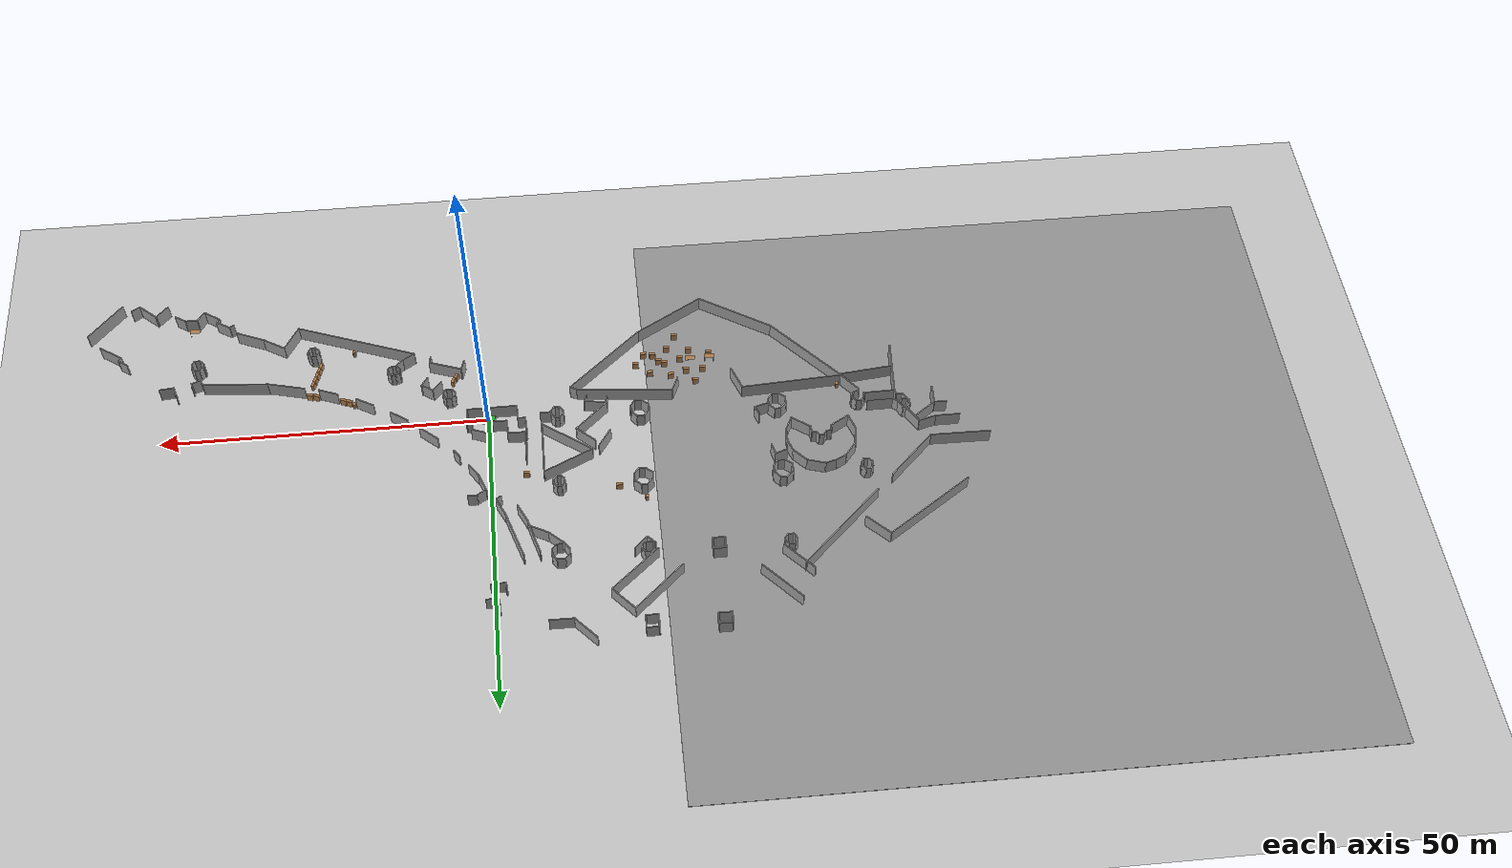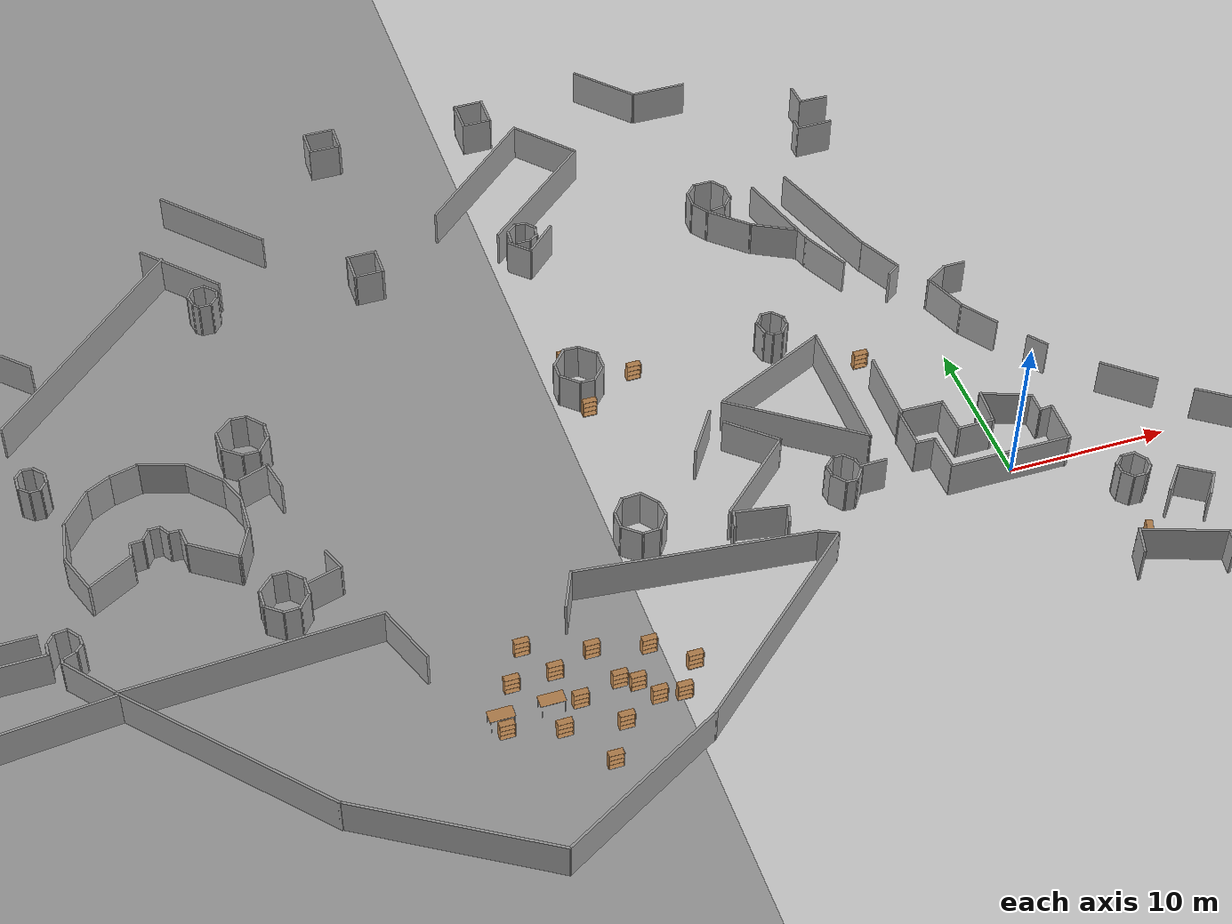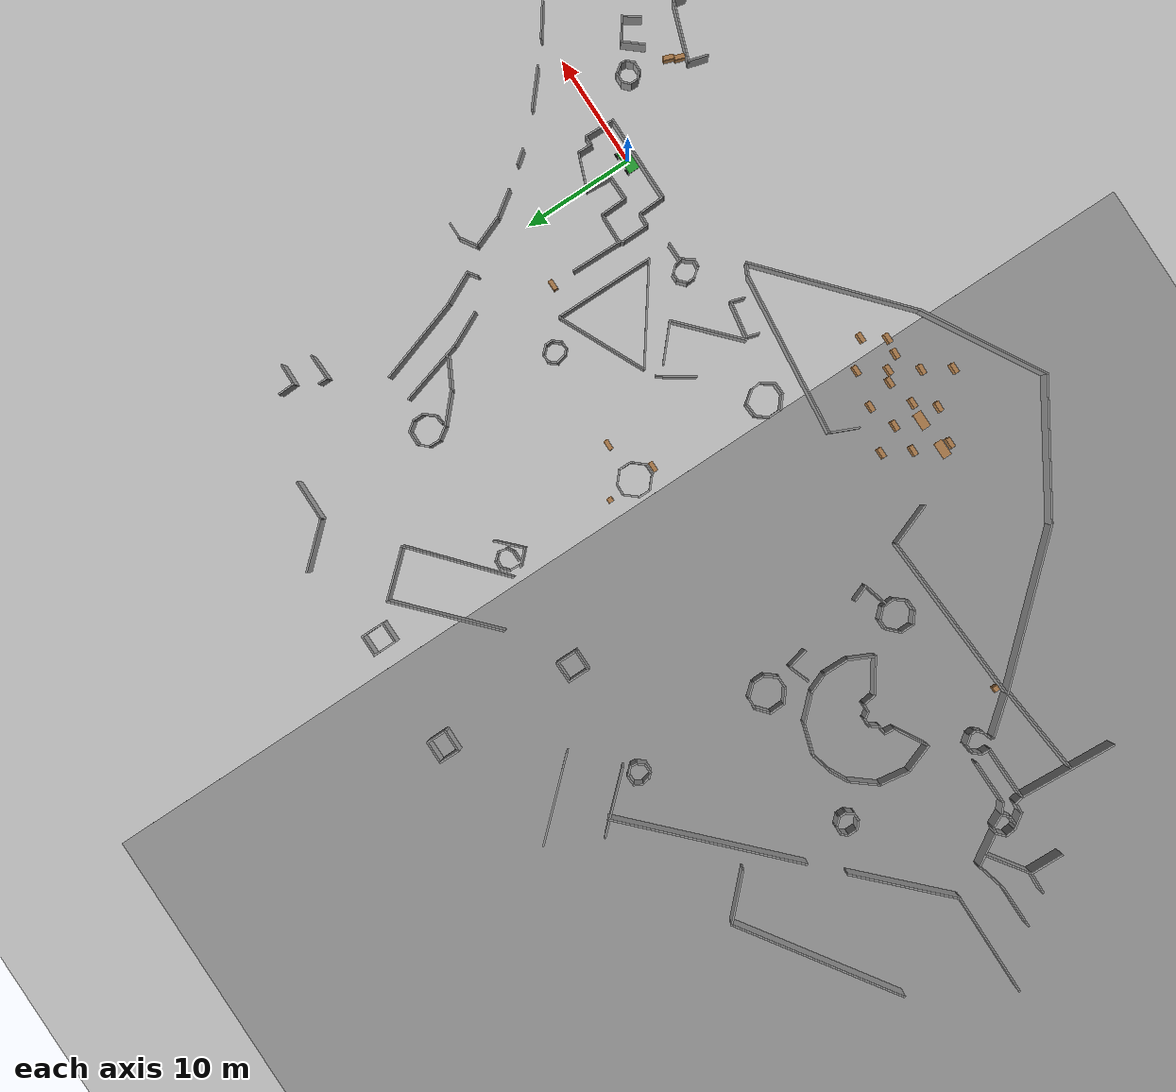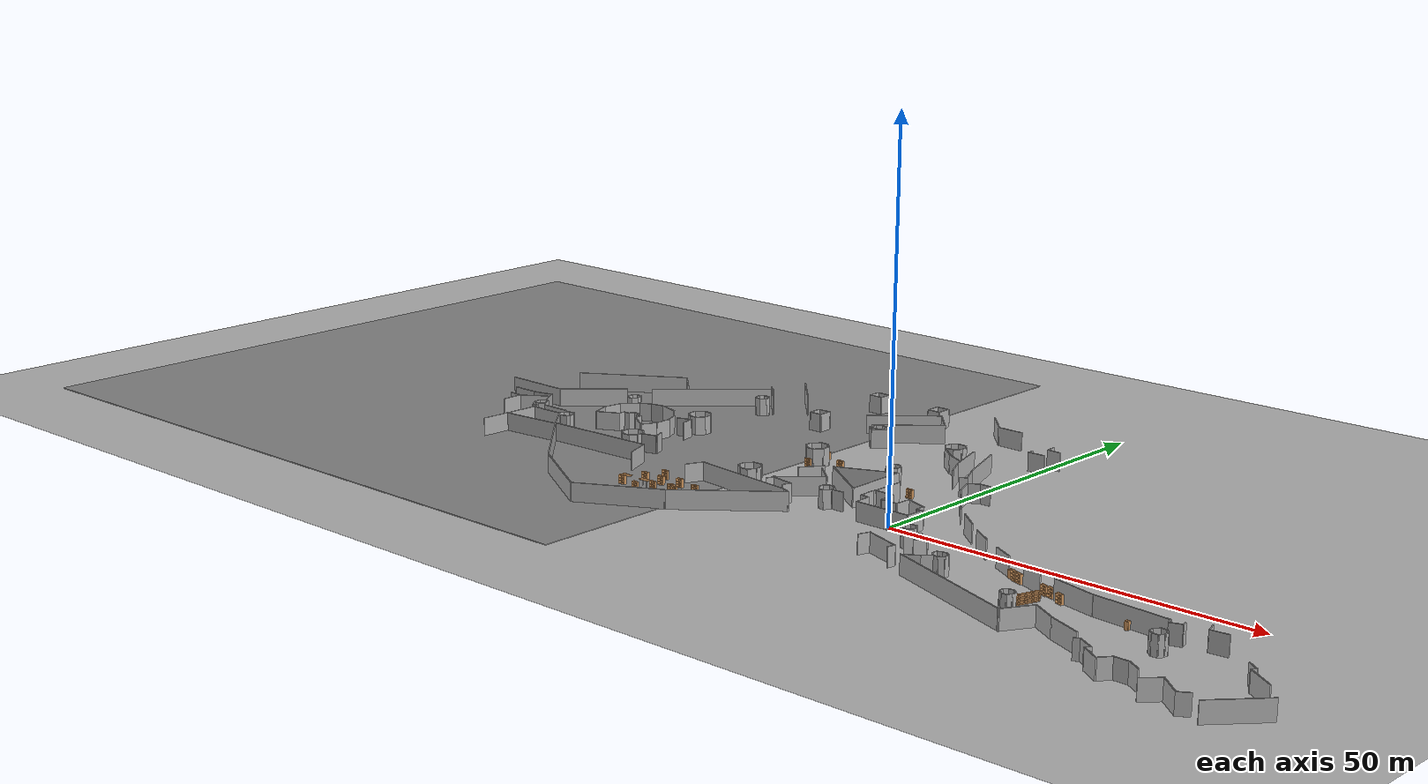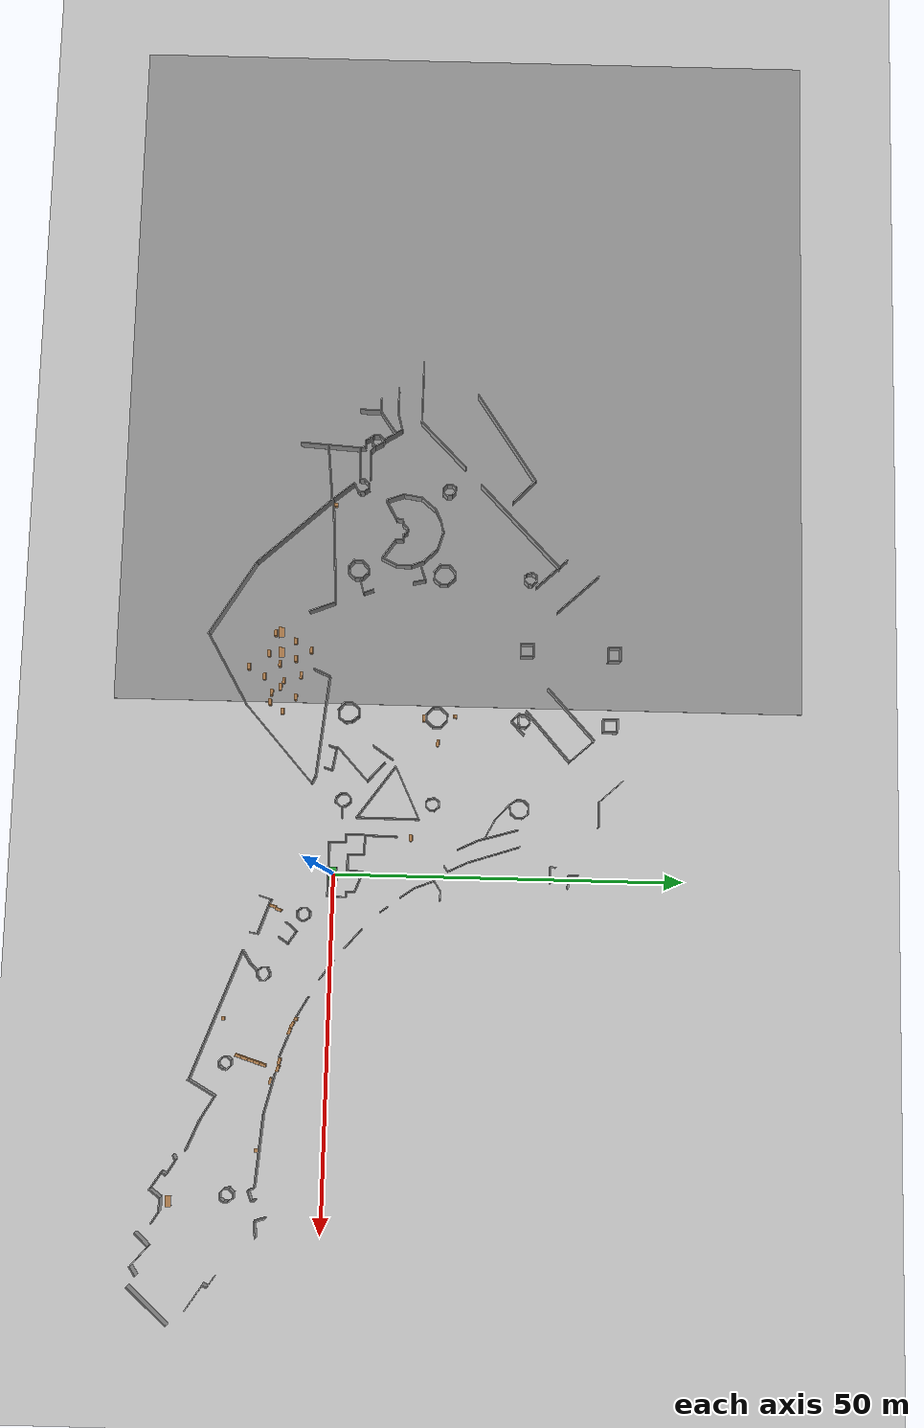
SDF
<sdf version="1.6">
 <world name="default">
  <model name="ground_plane">
   <static>1</static>
   <link name="link">
    <collision name="collision">
     <geometry><plane><normal>0 0 1</normal><size>100 100</size></plane></geometry>
     <surface><friction><ode><mu>100</mu><mu2>50</mu2></ode></friction></surface>
    </collision>
    <visual name="visual">
     <cast_shadows>0</cast_shadows>
     <geometry><plane><normal>0 0 1</normal><size>100 100</size></plane></geometry>
     <material>
      <script><uri>file://media/materials/scripts/gazebo.material</uri><name>Gazebo/Grey</name></script>
     </material>
    </visual>
   </link>
  </model>
  <light name="sun" type="directional">
   <pose>0 0 10 0 -0 0</pose>
   <diffuse>0.8 0.8 0.8 1</diffuse>
   <specular>0.2 0.2 0.2 1</specular>
   <attenuation>
    <range>1000</range>
    <constant>0.9</constant>
    <linear>0.01</linear>
    <quadratic>0.001</quadratic>
   </attenuation>
   <direction>-0.5 0.1 -0.9</direction>
  </light>
  <model name="mall_new_reduce_size">
   <pose>-6.8092 7.5529 0 0 -0 0</pose>
   <link name="Wall_0">
    <collision name="Wall_0_Collision">
     <geometry><box><size>9.25048 0.15 2.5</size></box></geometry>
     <pose>0 0 1.25 0 -0 0</pose>
    </collision>
    <visual name="Wall_0_Visual">
     <pose>0 0 1.25 0 -0 0</pose>
     <geometry><box><size>9.25048 0.15 2.5</size></box></geometry>
     <material>
      <script><uri>file://media/materials/scripts/gazebo.material</uri><name>Gazebo/Grey</name></script>
      <ambient>1 1 1 1</ambient>
     </material>
     <meta><layer>0</layer></meta>
    </visual>
    <pose>-64.3372 3.2996 0 0 -0 -0.010225</pose>
   </link>
   <link name="Wall_10">
    <collision name="Wall_10_Collision">
     <geometry><box><size>15.64 0.15 2.5</size></box></geometry>
     <pose>0 0 1.25 0 -0 0</pose>
    </collision>
    <visual name="Wall_10_Visual">
     <pose>0 0 1.25 0 -0 0</pose>
     <geometry><box><size>15.64 0.15 2.5</size></box></geometry>
     <material>
      <script><uri>file://media/materials/scripts/gazebo.material</uri><name>Gazebo/Grey</name></script>
      <ambient>1 1 1 1</ambient>
     </material>
     <meta><layer>0</layer></meta>
    </visual>
    <pose>-57.6357 15.9234 0 0 -0 0.595213</pose>
   </link>
   <link name="Wall_102">
    <collision name="Wall_102_Collision">
     <geometry><box><size>0.911014 0.15 2.5</size></box></geometry>
     <pose>0 0 1.25 0 -0 0</pose>
    </collision>
    <visual name="Wall_102_Visual">
     <pose>0 0 1.25 0 -0 0</pose>
     <geometry><box><size>0.911014 0.15 2.5</size></box></geometry>
     <material>
      <script><uri>file://media/materials/scripts/gazebo.material</uri><name>Gazebo/Grey</name></script>
      <ambient>1 1 1 1</ambient>
     </material>
     <meta><layer>0</layer></meta>
    </visual>
    <pose>5.13908 23.8484 0 0 -0 -1.5708</pose>
   </link>
   <link name="Wall_103">
    <collision name="Wall_103_Collision">
     <geometry><box><size>2.3915 0.15 2.5</size></box></geometry>
     <pose>0 0 1.25 0 -0 0</pose>
    </collision>
    <visual name="Wall_103_Visual">
     <pose>0 0 1.25 0 -0 0</pose>
     <geometry><box><size>2.3915 0.15 2.5</size></box></geometry>
     <material>
      <script><uri>file://media/materials/scripts/gazebo.material</uri><name>Gazebo/Grey</name></script>
      <ambient>1 1 1 1</ambient>
     </material>
     <meta><layer>0</layer></meta>
    </visual>
    <pose>6.25953 23.4864 0 0 -0 0.02316</pose>
   </link>
   <link name="Wall_106">
    <collision name="Wall_106_Collision">
     <geometry><box><size>0.88293 0.15 2.5</size></box></geometry>
     <pose>0 0 1.25 0 -0 0</pose>
    </collision>
    <visual name="Wall_106_Visual">
     <pose>0 0 1.25 0 -0 0</pose>
     <geometry><box><size>0.88293 0.15 2.5</size></box></geometry>
     <material>
      <script><uri>file://media/materials/scripts/gazebo.material</uri><name>Gazebo/Grey</name></script>
      <ambient>1 1 1 1</ambient>
     </material>
     <meta><layer>0</layer></meta>
    </visual>
    <pose>-37.2247 20.3731 0 0 -0 1.00343</pose>
   </link>
   <link name="Wall_107">
    <collision name="Wall_107_Collision">
     <geometry><box><size>0.940533 0.15 2.5</size></box></geometry>
     <pose>0 0 1.25 0 -0 0</pose>
    </collision>
    <visual name="Wall_107_Visual">
     <pose>0 0 1.25 0 -0 0</pose>
     <geometry><box><size>0.940533 0.15 2.5</size></box></geometry>
     <material>
      <script><uri>file://media/materials/scripts/gazebo.material</uri><name>Gazebo/Grey</name></script>
      <ambient>1 1 1 1</ambient>
     </material>
     <meta><layer>0</layer></meta>
    </visual>
    <pose>-36.633 20.7072 0 0 -0 0.04939</pose>
   </link>
   <link name="Wall_108">
    <collision name="Wall_108_Collision">
     <geometry><box><size>1.04338 0.15 2.5</size></box></geometry>
     <pose>0 0 1.25 0 -0 0</pose>
    </collision>
    <visual name="Wall_108_Visual">
     <pose>0 0 1.25 0 -0 0</pose>
     <geometry><box><size>1.04338 0.15 2.5</size></box></geometry>
     <material>
      <script><uri>file://media/materials/scripts/gazebo.material</uri><name>Gazebo/Grey</name></script>
      <ambient>1 1 1 1</ambient>
     </material>
     <meta><layer>0</layer></meta>
    </visual>
    <pose>-35.9265 20.4122 0 0 -0 -0.780985</pose>
   </link>
   <link name="Wall_109">
    <collision name="Wall_109_Collision">
     <geometry><box><size>0.676427 0.15 2.5</size></box></geometry>
     <pose>0 0 1.25 0 -0 0</pose>
    </collision>
    <visual name="Wall_109_Visual">
     <pose>0 0 1.25 0 -0 0</pose>
     <geometry><box><size>0.676427 0.15 2.5</size></box></geometry>
     <material>
      <script><uri>file://media/materials/scripts/gazebo.material</uri><name>Gazebo/Grey</name></script>
      <ambient>1 1 1 1</ambient>
     </material>
     <meta><layer>0</layer></meta>
    </visual>
    <pose>-35.6455 19.8364 0 0 -0 -1.68757</pose>
   </link>
   <link name="Wall_11">
    <collision name="Wall_11_Collision">
     <geometry><box><size>4.74566 0.15 2.5</size></box></geometry>
     <pose>0 0 1.25 0 -0 0</pose>
    </collision>
    <visual name="Wall_11_Visual">
     <pose>0 0 1.25 0 -0 0</pose>
     <geometry><box><size>4.74566 0.15 2.5</size></box></geometry>
     <material>
      <script><uri>file://media/materials/scripts/gazebo.material</uri><name>Gazebo/Grey</name></script>
      <ambient>1 1 1 1</ambient>
     </material>
     <meta><layer>0</layer></meta>
    </visual>
    <pose>-49.5878 18.6511 0 0 -0 -0.779209</pose>
   </link>
   <link name="Wall_110">
    <collision name="Wall_110_Collision">
     <geometry><box><size>0.945582 0.15 2.5</size></box></geometry>
     <pose>0 0 1.25 0 -0 0</pose>
    </collision>
    <visual name="Wall_110_Visual">
     <pose>0 0 1.25 0 -0 0</pose>
     <geometry><box><size>0.945582 0.15 2.5</size></box></geometry>
     <material>
      <script><uri>file://media/materials/scripts/gazebo.material</uri><name>Gazebo/Grey</name></script>
      <ambient>1 1 1 1</ambient>
     </material>
     <meta><layer>0</layer></meta>
    </visual>
    <pose>-35.9305 19.2738 0 0 -0 -2.28278</pose>
   </link>
   <link name="Wall_111">
    <collision name="Wall_111_Collision">
     <geometry><box><size>0.906136 0.15 2.5</size></box></geometry>
     <pose>0 0 1.25 0 -0 0</pose>
    </collision>
    <visual name="Wall_111_Visual">
     <pose>0 0 1.25 0 -0 0</pose>
     <geometry><box><size>0.906136 0.15 2.5</size></box></geometry>
     <material>
      <script><uri>file://media/materials/scripts/gazebo.material</uri><name>Gazebo/Grey</name></script>
      <ambient>1 1 1 1</ambient>
     </material>
     <meta><layer>0</layer></meta>
    </visual>
    <pose>-36.5684 18.981 0 0 -0 3.13422</pose>
   </link>
   <link name="Wall_112">
    <collision name="Wall_112_Collision">
     <geometry><box><size>0.599997 0.15 2.5</size></box></geometry>
     <pose>0 0 1.25 0 -0 0</pose>
    </collision>
    <visual name="Wall_112_Visual">
     <pose>0 0 1.25 0 -0 0</pose>
     <geometry><box><size>0.599997 0.15 2.5</size></box></geometry>
     <material>
      <script><uri>file://media/materials/scripts/gazebo.material</uri><name>Gazebo/Grey</name></script>
      <ambient>1 1 1 1</ambient>
     </material>
     <meta><layer>0</layer></meta>
    </visual>
    <pose>-37.1032 19.1505 0 0 -0 2.30701</pose>
   </link>
   <link name="Wall_116">
    <collision name="Wall_116_Collision">
     <geometry><box><size>0.795039 0.15 2.5</size></box></geometry>
     <pose>0 0 1.25 0 -0 0</pose>
    </collision>
    <visual name="Wall_116_Visual">
     <pose>0 0 1.25 0 -0 0</pose>
     <geometry><box><size>0.795039 0.15 2.5</size></box></geometry>
     <material>
      <script><uri>file://media/materials/scripts/gazebo.material</uri><name>Gazebo/Grey</name></script>
      <ambient>1 1 1 1</ambient>
     </material>
     <meta><layer>0</layer></meta>
    </visual>
    <pose>-37.3234 19.6378 0 0 -0 1.78689</pose>
   </link>
   <link name="Wall_120">
    <collision name="Wall_120_Collision">
     <geometry><box><size>2 0.15 2.5</size></box></geometry>
     <pose>0 0 1.25 0 -0 0</pose>
    </collision>
    <visual name="Wall_120_Visual">
     <pose>0 0 1.25 0 -0 0</pose>
     <geometry><box><size>2 0.15 2.5</size></box></geometry>
     <material>
      <script><uri>file://media/materials/scripts/gazebo.material</uri><name>Gazebo/Grey</name></script>
      <ambient>1 1 1 1</ambient>
     </material>
     <meta><layer>0</layer></meta>
    </visual>
    <pose>-26.9558 19.541 0 0 -0 -1.5708</pose>
   </link>
   <link name="Wall_121">
    <collision name="Wall_121_Collision">
     <geometry><box><size>1.9668 0.15 2.5</size></box></geometry>
     <pose>0 0 1.25 0 -0 0</pose>
    </collision>
    <visual name="Wall_121_Visual">
     <pose>0 0 1.25 0 -0 0</pose>
     <geometry><box><size>1.9668 0.15 2.5</size></box></geometry>
     <material>
      <script><uri>file://media/materials/scripts/gazebo.material</uri><name>Gazebo/Grey</name></script>
      <ambient>1 1 1 1</ambient>
     </material>
     <meta><layer>0</layer></meta>
    </visual>
    <pose>-26.0474 18.619 0 0 -0 0.003382</pose>
   </link>
   <link name="Wall_122">
    <collision name="Wall_122_Collision">
     <geometry><box><size>2.02653 0.15 2.5</size></box></geometry>
     <pose>0 0 1.25 0 -0 0</pose>
    </collision>
    <visual name="Wall_122_Visual">
     <pose>0 0 1.25 0 -0 0</pose>
     <geometry><box><size>2.02653 0.15 2.5</size></box></geometry>
     <material>
      <script><uri>file://media/materials/scripts/gazebo.material</uri><name>Gazebo/Grey</name></script>
      <ambient>1 1 1 1</ambient>
     </material>
     <meta><layer>0</layer></meta>
    </visual>
    <pose>-25.1383 19.554 0 0 -0 1.57003</pose>
   </link>
   <link name="Wall_123">
    <collision name="Wall_123_Collision">
     <geometry><box><size>1.99983 0.15 2.5</size></box></geometry>
     <pose>0 0 1.25 0 -0 0</pose>
    </collision>
    <visual name="Wall_123_Visual">
     <pose>0 0 1.25 0 -0 0</pose>
     <geometry><box><size>1.99983 0.15 2.5</size></box></geometry>
     <material>
      <script><uri>file://media/materials/scripts/gazebo.material</uri><name>Gazebo/Grey</name></script>
      <ambient>1 1 1 1</ambient>
     </material>
     <meta><layer>0</layer></meta>
    </visual>
    <pose>-26.056 20.4954 0 0 -0 -3.12426</pose>
   </link>
   <link name="Wall_126">
    <collision name="Wall_126_Collision">
     <geometry><box><size>1.5 0.15 2.5</size></box></geometry>
     <pose>0 0 1.25 0 -0 0</pose>
    </collision>
    <visual name="Wall_126_Visual">
     <pose>0 0 1.25 0 -0 0</pose>
     <geometry><box><size>1.5 0.15 2.5</size></box></geometry>
     <material>
      <script><uri>file://media/materials/scripts/gazebo.material</uri><name>Gazebo/Grey</name></script>
      <ambient>1 1 1 1</ambient>
     </material>
     <meta><layer>0</layer></meta>
    </visual>
    <pose>9.56035 7.86068 0 0 -0 3.14159</pose>
   </link>
   <link name="Wall_127">
    <collision name="Wall_127_Collision">
     <geometry><box><size>1.79669 0.15 2.5</size></box></geometry>
     <pose>0 0 1.25 0 -0 0</pose>
    </collision>
    <visual name="Wall_127_Visual">
     <pose>0 0 1.25 0 -0 0</pose>
     <geometry><box><size>1.79669 0.15 2.5</size></box></geometry>
     <material>
      <script><uri>file://media/materials/scripts/gazebo.material</uri><name>Gazebo/Grey</name></script>
      <ambient>1 1 1 1</ambient>
     </material>
     <meta><layer>0</layer></meta>
    </visual>
    <pose>8.19253 7.41582 0 0 -0 -2.57079</pose>
   </link>
   <link name="Wall_128">
    <collision name="Wall_128_Collision">
     <geometry><box><size>3.04987 0.15 2.5</size></box></geometry>
     <pose>0 0 1.25 0 -0 0</pose>
    </collision>
    <visual name="Wall_128_Visual">
     <pose>0 0 1.25 0 -0 0</pose>
     <geometry><box><size>3.04987 0.15 2.5</size></box></geometry>
     <material>
      <script><uri>file://media/materials/scripts/gazebo.material</uri><name>Gazebo/Grey</name></script>
      <ambient>1 1 1 1</ambient>
     </material>
     <meta><layer>0</layer></meta>
    </visual>
    <pose>8.01735 5.63901 0 0 -0 -1.20574</pose>
   </link>
   <link name="Wall_129">
    <collision name="Wall_129_Collision">
     <geometry><box><size>2.67124 0.15 2.5</size></box></geometry>
     <pose>0 0 1.25 0 -0 0</pose>
    </collision>
    <visual name="Wall_129_Visual">
     <pose>0 0 1.25 0 -0 0</pose>
     <geometry><box><size>2.67124 0.15 2.5</size></box></geometry>
     <material>
      <script><uri>file://media/materials/scripts/gazebo.material</uri><name>Gazebo/Grey</name></script>
      <ambient>1 1 1 1</ambient>
     </material>
     <meta><layer>0</layer></meta>
    </visual>
    <pose>9.25128 3.23607 0 0 -0 -0.966457</pose>
   </link>
   <link name="Wall_134">
    <collision name="Wall_134_Collision">
     <geometry><box><size>1.4429 0.15 2.5</size></box></geometry>
     <pose>0 0 1.25 0 -0 0</pose>
    </collision>
    <visual name="Wall_134_Visual">
     <pose>0 0 1.25 0 -0 0</pose>
     <geometry><box><size>1.4429 0.15 2.5</size></box></geometry>
     <material>
      <script><uri>file://media/materials/scripts/gazebo.material</uri><name>Gazebo/Grey</name></script>
      <ambient>1 1 1 1</ambient>
     </material>
     <meta><layer>0</layer></meta>
    </visual>
    <pose>11.7178 -0.065856 0 0 -0 -0.919284</pose>
   </link>
   <link name="Wall_137">
    <collision name="Wall_137_Collision">
     <geometry><box><size>3.68143 0.15 2.5</size></box></geometry>
     <pose>0 0 1.25 0 -0 0</pose>
    </collision>
    <visual name="Wall_137_Visual">
     <pose>0 0 1.25 0 -0 0</pose>
     <geometry><box><size>3.68143 0.15 2.5</size></box></geometry>
     <material>
      <script><uri>file://media/materials/scripts/gazebo.material</uri><name>Gazebo/Grey</name></script>
      <ambient>1 1 1 1</ambient>
     </material>
     <meta><layer>0</layer></meta>
    </visual>
    <pose>15.8732 -4.24673 0 0 -0 -0.713439</pose>
   </link>
   <link name="Wall_140">
    <collision name="Wall_140_Collision">
     <geometry><box><size>3.35827 0.15 2.5</size></box></geometry>
     <pose>0 0 1.25 0 -0 0</pose>
    </collision>
    <visual name="Wall_140_Visual">
     <pose>0 0 1.25 0 -0 0</pose>
     <geometry><box><size>3.35827 0.15 2.5</size></box></geometry>
     <material>
      <script><uri>file://media/materials/scripts/gazebo.material</uri><name>Gazebo/Grey</name></script>
      <ambient>1 1 1 1</ambient>
     </material>
     <meta><layer>0</layer></meta>
    </visual>
    <pose>20.3327 -7.86303 0 0 -0 -0.619292</pose>
   </link>
   <link name="Wall_143">
    <collision name="Wall_143_Collision">
     <geometry><box><size>3.17972 0.15 2.5</size></box></geometry>
     <pose>0 0 1.25 0 -0 0</pose>
    </collision>
    <visual name="Wall_143_Visual">
     <pose>0 0 1.25 0 -0 0</pose>
     <geometry><box><size>3.17972 0.15 2.5</size></box></geometry>
     <material>
      <script><uri>file://media/materials/scripts/gazebo.material</uri><name>Gazebo/Grey</name></script>
      <ambient>1 1 1 1</ambient>
     </material>
     <meta><layer>0</layer></meta>
    </visual>
    <pose>25.5439 -11.078 0 0 -0 -0.516247</pose>
   </link>
   <link name="Wall_146">
    <collision name="Wall_146_Collision">
     <geometry><box><size>3.13185 0.15 2.5</size></box></geometry>
     <pose>0 0 1.25 0 -0 0</pose>
    </collision>
    <visual name="Wall_146_Visual">
     <pose>0 0 1.25 0 -0 0</pose>
     <geometry><box><size>3.13185 0.15 2.5</size></box></geometry>
     <material>
      <script><uri>file://media/materials/scripts/gazebo.material</uri><name>Gazebo/Grey</name></script>
      <ambient>1 1 1 1</ambient>
     </material>
     <meta><layer>0</layer></meta>
    </visual>
    <pose>31.1319 -13.5209 0 0 -0 -0.367866</pose>
   </link>
   <link name="Wall_149">
    <collision name="Wall_149_Collision">
     <geometry><box><size>6.0228 0.15 2.5</size></box></geometry>
     <pose>0 0 1.25 0 -0 0</pose>
    </collision>
    <visual name="Wall_149_Visual">
     <pose>0 0 1.25 0 -0 0</pose>
     <geometry><box><size>6.0228 0.15 2.5</size></box></geometry>
     <material>
      <script><uri>file://media/materials/scripts/gazebo.material</uri><name>Gazebo/Grey</name></script>
      <ambient>1 1 1 1</ambient>
     </material>
     <meta><layer>0</layer></meta>
    </visual>
    <pose>37.6627 -15.2721 0 0 -0 -0.24371</pose>
   </link>
   <link name="Wall_15">
    <collision name="Wall_15_Collision">
     <geometry><box><size>17.0313 0.15 2.5</size></box></geometry>
     <pose>0 0 1.25 0 -0 0</pose>
    </collision>
    <visual name="Wall_15_Visual">
     <pose>0 0 1.25 0 -0 0</pose>
     <geometry><box><size>17.0313 0.15 2.5</size></box></geometry>
     <material>
      <script><uri>file://media/materials/scripts/gazebo.material</uri><name>Gazebo/Grey</name></script>
      <ambient>1 1 1 1</ambient>
     </material>
     <meta><layer>0</layer></meta>
    </visual>
    <pose>-44.3443 18.1837 0 0 -0 0.766862</pose>
   </link>
   <link name="Wall_150">
    <collision name="Wall_150_Collision">
     <geometry><box><size>10.0902 0.15 2.5</size></box></geometry>
     <pose>0 0 1.25 0 -0 0</pose>
    </collision>
    <visual name="Wall_150_Visual">
     <pose>0 0 1.25 0 -0 0</pose>
     <geometry><box><size>10.0902 0.15 2.5</size></box></geometry>
     <material>
      <script><uri>file://media/materials/scripts/gazebo.material</uri><name>Gazebo/Grey</name></script>
      <ambient>1 1 1 1</ambient>
     </material>
     <meta><layer>0</layer></meta>
    </visual>
    <pose>45.4742 -16.3538 0 0 -0 -0.081987</pose>
   </link>
   <link name="Wall_151">
    <collision name="Wall_151_Collision">
     <geometry><box><size>1.07037 0.15 2.5</size></box></geometry>
     <pose>0 0 1.25 0 -0 0</pose>
    </collision>
    <visual name="Wall_151_Visual">
     <pose>0 0 1.25 0 -0 0</pose>
     <geometry><box><size>1.07037 0.15 2.5</size></box></geometry>
     <material>
      <script><uri>file://media/materials/scripts/gazebo.material</uri><name>Gazebo/Grey</name></script>
      <ambient>1 1 1 1</ambient>
     </material>
     <meta><layer>0</layer></meta>
    </visual>
    <pose>50.5839 -17.1905 0 0 -0 -1.20463</pose>
   </link>
   <link name="Wall_152">
    <collision name="Wall_152_Collision">
     <geometry><box><size>1.64204 0.15 2.5</size></box></geometry>
     <pose>0 0 1.25 0 -0 0</pose>
    </collision>
    <visual name="Wall_152_Visual">
     <pose>0 0 1.25 0 -0 0</pose>
     <geometry><box><size>1.64204 0.15 2.5</size></box></geometry>
     <material>
      <script><uri>file://media/materials/scripts/gazebo.material</uri><name>Gazebo/Grey</name></script>
      <ambient>1 1 1 1</ambient>
     </material>
     <meta><layer>0</layer></meta>
    </visual>
    <pose>51.4454 -17.3621 0 0 -0 0.365329</pose>
   </link>
   <link name="Wall_153">
    <collision name="Wall_153_Collision">
     <geometry><box><size>0.719382 0.15 2.5</size></box></geometry>
     <pose>0 0 1.25 0 -0 0</pose>
    </collision>
    <visual name="Wall_153_Visual">
     <pose>0 0 1.25 0 -0 0</pose>
     <geometry><box><size>0.719382 0.15 2.5</size></box></geometry>
     <material>
      <script><uri>file://media/materials/scripts/gazebo.material</uri><name>Gazebo/Grey</name></script>
      <ambient>1 1 1 1</ambient>
     </material>
     <meta><layer>0</layer></meta>
    </visual>
    <pose>52.104 -16.8147 0 0 -0 1.73536</pose>
   </link>
   <link name="Wall_156">
    <collision name="Wall_156_Collision">
     <geometry><box><size>1.66975 0.15 2.5</size></box></geometry>
     <pose>0 0 1.25 0 -0 0</pose>
    </collision>
    <visual name="Wall_156_Visual">
     <pose>0 0 1.25 0 -0 0</pose>
     <geometry><box><size>1.66975 0.15 2.5</size></box></geometry>
     <material>
      <script><uri>file://media/materials/scripts/gazebo.material</uri><name>Gazebo/Grey</name></script>
      <ambient>1 1 1 1</ambient>
     </material>
     <meta><layer>0</layer></meta>
    </visual>
    <pose>54.6252 -15.8323 0 0 -0 -1.27154</pose>
   </link>
   <link name="Wall_157">
    <collision name="Wall_157_Collision">
     <geometry><box><size>2.34099 0.15 2.5</size></box></geometry>
     <pose>0 0 1.25 0 -0 0</pose>
    </collision>
    <visual name="Wall_157_Visual">
     <pose>0 0 1.25 0 -0 0</pose>
     <geometry><box><size>2.34099 0.15 2.5</size></box></geometry>
     <material>
      <script><uri>file://media/materials/scripts/gazebo.material</uri><name>Gazebo/Grey</name></script>
      <ambient>1 1 1 1</ambient>
     </material>
     <meta><layer>0</layer></meta>
    </visual>
    <pose>55.9396 -16.4609 0 0 -0 0.096908</pose>
   </link>
   <link name="Wall_160">
    <collision name="Wall_160_Collision">
     <geometry><box><size>0.922115 0.15 2.5</size></box></geometry>
     <pose>0 0 1.25 0 -0 0</pose>
    </collision>
    <visual name="Wall_160_Visual">
     <pose>0 0 1.25 0 -0 0</pose>
     <geometry><box><size>0.922115 0.15 2.5</size></box></geometry>
     <material>
      <script><uri>file://media/materials/scripts/gazebo.material</uri><name>Gazebo/Grey</name></script>
      <ambient>1 1 1 1</ambient>
     </material>
     <meta><layer>0</layer></meta>
    </visual>
    <pose>50.8361 -19.9069 0 0 -0 0.843659</pose>
   </link>
   <link name="Wall_161">
    <collision name="Wall_161_Collision">
     <geometry><box><size>0.855974 0.15 2.5</size></box></geometry>
     <pose>0 0 1.25 0 -0 0</pose>
    </collision>
    <visual name="Wall_161_Visual">
     <pose>0 0 1.25 0 -0 0</pose>
     <geometry><box><size>0.855974 0.15 2.5</size></box></geometry>
     <material>
      <script><uri>file://media/materials/scripts/gazebo.material</uri><name>Gazebo/Grey</name></script>
      <ambient>1 1 1 1</ambient>
     </material>
     <meta><layer>0</layer></meta>
    </visual>
    <pose>51.4457 -19.6069 0 0 -0 0.008949</pose>
   </link>
   <link name="Wall_162">
    <collision name="Wall_162_Collision">
     <geometry><box><size>1.02706 0.15 2.5</size></box></geometry>
     <pose>0 0 1.25 0 -0 0</pose>
    </collision>
    <visual name="Wall_162_Visual">
     <pose>0 0 1.25 0 -0 0</pose>
     <geometry><box><size>1.02706 0.15 2.5</size></box></geometry>
     <material>
      <script><uri>file://media/materials/scripts/gazebo.material</uri><name>Gazebo/Grey</name></script>
      <ambient>1 1 1 1</ambient>
     </material>
     <meta><layer>0</layer></meta>
    </visual>
    <pose>52.0627 -19.9472 0 0 -0 -0.900073</pose>
   </link>
   <link name="Wall_163">
    <collision name="Wall_163_Collision">
     <geometry><box><size>0.756321 0.15 2.5</size></box></geometry>
     <pose>0 0 1.25 0 -0 0</pose>
    </collision>
    <visual name="Wall_163_Visual">
     <pose>0 0 1.25 0 -0 0</pose>
     <geometry><box><size>0.756321 0.15 2.5</size></box></geometry>
     <material>
      <script><uri>file://media/materials/scripts/gazebo.material</uri><name>Gazebo/Grey</name></script>
      <ambient>1 1 1 1</ambient>
     </material>
     <meta><layer>0</layer></meta>
    </visual>
    <pose>52.3278 -20.5939 0 0 -0 -1.56745</pose>
   </link>
   <link name="Wall_164">
    <collision name="Wall_164_Collision">
     <geometry><box><size>0.854712 0.15 2.5</size></box></geometry>
     <pose>0 0 1.25 0 -0 0</pose>
    </collision>
    <visual name="Wall_164_Visual">
     <pose>0 0 1.25 0 -0 0</pose>
     <geometry><box><size>0.854712 0.15 2.5</size></box></geometry>
     <material>
      <script><uri>file://media/materials/scripts/gazebo.material</uri><name>Gazebo/Grey</name></script>
      <ambient>1 1 1 1</ambient>
     </material>
     <meta><layer>0</layer></meta>
    </visual>
    <pose>52.1195 -21.1866 0 0 -0 -2.17742</pose>
   </link>
   <link name="Wall_165">
    <collision name="Wall_165_Collision">
     <geometry><box><size>0.950864 0.15 2.5</size></box></geometry>
     <pose>0 0 1.25 0 -0 0</pose>
    </collision>
    <visual name="Wall_165_Visual">
     <pose>0 0 1.25 0 -0 0</pose>
     <geometry><box><size>0.950864 0.15 2.5</size></box></geometry>
     <material>
      <script><uri>file://media/materials/scripts/gazebo.material</uri><name>Gazebo/Grey</name></script>
      <ambient>1 1 1 1</ambient>
     </material>
     <meta><layer>0</layer></meta>
    </visual>
    <pose>51.5271 -21.4943 0 0 -0 -3.09591</pose>
   </link>
   <link name="Wall_166">
    <collision name="Wall_166_Collision">
     <geometry><box><size>0.977095 0.15 2.5</size></box></geometry>
     <pose>0 0 1.25 0 -0 0</pose>
    </collision>
    <visual name="Wall_166_Visual">
     <pose>0 0 1.25 0 -0 0</pose>
     <geometry><box><size>0.977095 0.15 2.5</size></box></geometry>
     <material>
      <script><uri>file://media/materials/scripts/gazebo.material</uri><name>Gazebo/Grey</name></script>
      <ambient>1 1 1 1</ambient>
     </material>
     <meta><layer>0</layer></meta>
    </visual>
    <pose>50.8226 -21.2238 0 0 -0 2.36845</pose>
   </link>
   <link name="Wall_167">
    <collision name="Wall_167_Collision">
     <geometry><box><size>0.862803 0.15 2.5</size></box></geometry>
     <pose>0 0 1.25 0 -0 0</pose>
    </collision>
    <visual name="Wall_167_Visual">
     <pose>0 0 1.25 0 -0 0</pose>
     <geometry><box><size>0.862803 0.15 2.5</size></box></geometry>
     <material>
      <script><uri>file://media/materials/scripts/gazebo.material</uri><name>Gazebo/Grey</name></script>
      <ambient>1 1 1 1</ambient>
     </material>
     <meta><layer>0</layer></meta>
    </visual>
    <pose>50.5217 -20.5788 0 0 -0 1.60849</pose>
   </link>
   <link name="Wall_17">
    <collision name="Wall_17_Collision">
     <geometry><box><size>6.11812 0.15 2.5</size></box></geometry>
     <pose>0 0 1.25 0 -0 0</pose>
    </collision>
    <visual name="Wall_17_Visual">
     <pose>0 0 1.25 0 -0 0</pose>
     <geometry><box><size>6.11812 0.15 2.5</size></box></geometry>
     <material>
      <script><uri>file://media/materials/scripts/gazebo.material</uri><name>Gazebo/Grey</name></script>
      <ambient>1 1 1 1</ambient>
     </material>
     <meta><layer>0</layer></meta>
    </visual>
    <pose>-37.3721 22.8899 0 0 -0 -0.823537</pose>
   </link>
   <link name="Wall_170">
    <collision name="Wall_170_Collision">
     <geometry><box><size>1.71198 0.15 2.5</size></box></geometry>
     <pose>0 0 1.25 0 -0 0</pose>
    </collision>
    <visual name="Wall_170_Visual">
     <pose>0 0 1.25 0 -0 0</pose>
     <geometry><box><size>1.71198 0.15 2.5</size></box></geometry>
     <material>
      <script><uri>file://media/materials/scripts/gazebo.material</uri><name>Gazebo/Grey</name></script>
      <ambient>1 1 1 1</ambient>
     </material>
     <meta><layer>0</layer></meta>
    </visual>
    <pose>63.0306 -22.2425 0 0 -0 -0.612119</pose>
   </link>
   <link name="Wall_171">
    <collision name="Wall_171_Collision">
     <geometry><box><size>0.839183 0.15 2.5</size></box></geometry>
     <pose>0 0 1.25 0 -0 0</pose>
    </collision>
    <visual name="Wall_171_Visual">
     <pose>0 0 1.25 0 -0 0</pose>
     <geometry><box><size>0.839183 0.15 2.5</size></box></geometry>
     <material>
      <script><uri>file://media/materials/scripts/gazebo.material</uri><name>Gazebo/Grey</name></script>
      <ambient>1 1 1 1</ambient>
     </material>
     <meta><layer>0</layer></meta>
    </visual>
    <pose>63.5354 -23.0042 0 0 -0 -2.00233</pose>
   </link>
   <link name="Wall_172">
    <collision name="Wall_172_Collision">
     <geometry><box><size>4.15243 0.15 2.5</size></box></geometry>
     <pose>0 0 1.25 0 -0 0</pose>
    </collision>
    <visual name="Wall_172_Visual">
     <pose>0 0 1.25 0 -0 0</pose>
     <geometry><box><size>4.15243 0.15 2.5</size></box></geometry>
     <material>
      <script><uri>file://media/materials/scripts/gazebo.material</uri><name>Gazebo/Grey</name></script>
      <ambient>1 1 1 1</ambient>
     </material>
     <meta><layer>0</layer></meta>
    </visual>
    <pose>65.0743 -24.4298 0 0 -0 -0.589468</pose>
   </link>
   <link name="Wall_175">
    <collision name="Wall_175_Collision">
     <geometry><box><size>7.63134 0.15 2.5</size></box></geometry>
     <pose>0 0 1.25 0 -0 0</pose>
    </collision>
    <visual name="Wall_175_Visual">
     <pose>0 0 1.25 0 -0 0</pose>
     <geometry><box><size>7.63134 0.15 2.5</size></box></geometry>
     <material>
      <script><uri>file://media/materials/scripts/gazebo.material</uri><name>Gazebo/Grey</name></script>
      <ambient>1 1 1 1</ambient>
     </material>
     <meta><layer>0</layer></meta>
    </visual>
    <pose>66.4001 -30.8567 0 0 -0 -2.28745</pose>
   </link>
   <link name="Wall_178">
    <collision name="Wall_178_Collision">
     <geometry><box><size>2.71113 0.15 2.5</size></box></geometry>
     <pose>0 0 1.25 0 -0 0</pose>
    </collision>
    <visual name="Wall_178_Visual">
     <pose>0 0 1.25 0 -0 0</pose>
     <geometry><box><size>2.71113 0.15 2.5</size></box></geometry>
     <material>
      <script><uri>file://media/materials/scripts/gazebo.material</uri><name>Gazebo/Grey</name></script>
      <ambient>1 1 1 1</ambient>
     </material>
     <meta><layer>0</layer></meta>
    </visual>
    <pose>57.6342 -32.0142 0 0 -0 0.814065</pose>
   </link>
   <link name="Wall_179">
    <collision name="Wall_179_Collision">
     <geometry><box><size>3.68959 0.15 2.5</size></box></geometry>
     <pose>0 0 1.25 0 -0 0</pose>
    </collision>
    <visual name="Wall_179_Visual">
     <pose>0 0 1.25 0 -0 0</pose>
     <geometry><box><size>3.68959 0.15 2.5</size></box></geometry>
     <material>
      <script><uri>file://media/materials/scripts/gazebo.material</uri><name>Gazebo/Grey</name></script>
      <ambient>1 1 1 1</ambient>
     </material>
     <meta><layer>0</layer></meta>
    </visual>
    <pose>59.8368 -32.2413 0 0 -0 -0.713396</pose>
   </link>
   <link name="Wall_180">
    <collision name="Wall_180_Collision">
     <geometry><box><size>1.63637 0.15 2.5</size></box></geometry>
     <pose>0 0 1.25 0 -0 0</pose>
    </collision>
    <visual name="Wall_180_Visual">
     <pose>0 0 1.25 0 -0 0</pose>
     <geometry><box><size>1.63637 0.15 2.5</size></box></geometry>
     <material>
      <script><uri>file://media/materials/scripts/gazebo.material</uri><name>Gazebo/Grey</name></script>
      <ambient>1 1 1 1</ambient>
     </material>
     <meta><layer>0</layer></meta>
    </visual>
    <pose>61.8128 -33.009 0 0 -0 0.576763</pose>
   </link>
   <link name="Wall_183">
    <collision name="Wall_183_Collision">
     <geometry><box><size>0.858507 0.15 2.5</size></box></geometry>
     <pose>0 0 1.25 0 -0 0</pose>
    </collision>
    <visual name="Wall_183_Visual">
     <pose>0 0 1.25 0 -0 0</pose>
     <geometry><box><size>0.858507 0.15 2.5</size></box></geometry>
     <material>
      <script><uri>file://media/materials/scripts/gazebo.material</uri><name>Gazebo/Grey</name></script>
      <ambient>1 1 1 1</ambient>
     </material>
     <meta><layer>0</layer></meta>
    </visual>
    <pose>46.5261 -28.0243 0 0 -0 0.469325</pose>
   </link>
   <link name="Wall_184">
    <collision name="Wall_184_Collision">
     <geometry><box><size>2.54291 0.15 2.5</size></box></geometry>
     <pose>0 0 1.25 0 -0 0</pose>
    </collision>
    <visual name="Wall_184_Visual">
     <pose>0 0 1.25 0 -0 0</pose>
     <geometry><box><size>2.54291 0.15 2.5</size></box></geometry>
     <material>
      <script><uri>file://media/materials/scripts/gazebo.material</uri><name>Gazebo/Grey</name></script>
      <ambient>1 1 1 1</ambient>
     </material>
     <meta><layer>0</layer></meta>
    </visual>
    <pose>47.867 -28.4664 0 0 -0 -0.541971</pose>
   </link>
   <link name="Wall_185">
    <collision name="Wall_185_Collision">
     <geometry><box><size>0.862335 0.15 2.5</size></box></geometry>
     <pose>0 0 1.25 0 -0 0</pose>
    </collision>
    <visual name="Wall_185_Visual">
     <pose>0 0 1.25 0 -0 0</pose>
     <geometry><box><size>0.862335 0.15 2.5</size></box></geometry>
     <material>
      <script><uri>file://media/materials/scripts/gazebo.material</uri><name>Gazebo/Grey</name></script>
      <ambient>1 1 1 1</ambient>
     </material>
     <meta><layer>0</layer></meta>
    </visual>
    <pose>48.6957 -29.3956 0 0 -0 -2.15451</pose>
   </link>
   <link name="Wall_186">
    <collision name="Wall_186_Collision">
     <geometry><box><size>2.98998 0.15 2.5</size></box></geometry>
     <pose>0 0 1.25 0 -0 0</pose>
    </collision>
    <visual name="Wall_186_Visual">
     <pose>0 0 1.25 0 -0 0</pose>
     <geometry><box><size>2.98998 0.15 2.5</size></box></geometry>
     <material>
      <script><uri>file://media/materials/scripts/gazebo.material</uri><name>Gazebo/Grey</name></script>
      <ambient>1 1 1 1</ambient>
     </material>
     <meta><layer>0</layer></meta>
    </visual>
    <pose>49.6816 -30.4646 0 0 -0 -0.587145</pose>
   </link>
   <link name="Wall_187">
    <collision name="Wall_187_Collision">
     <geometry><box><size>1.97307 0.15 2.5</size></box></geometry>
     <pose>0 0 1.25 0 -0 0</pose>
    </collision>
    <visual name="Wall_187_Visual">
     <pose>0 0 1.25 0 -0 0</pose>
     <geometry><box><size>1.97307 0.15 2.5</size></box></geometry>
     <material>
      <script><uri>file://media/materials/scripts/gazebo.material</uri><name>Gazebo/Grey</name></script>
      <ambient>1 1 1 1</ambient>
     </material>
     <meta><layer>0</layer></meta>
    </visual>
    <pose>51.4004 -30.4996 0 0 -0 0.941346</pose>
   </link>
   <link name="Wall_188">
    <collision name="Wall_188_Collision">
     <geometry><box><size>2.01359 0.15 2.5</size></box></geometry>
     <pose>0 0 1.25 0 -0 0</pose>
    </collision>
    <visual name="Wall_188_Visual">
     <pose>0 0 1.25 0 -0 0</pose>
     <geometry><box><size>2.01359 0.15 2.5</size></box></geometry>
     <material>
      <script><uri>file://media/materials/scripts/gazebo.material</uri><name>Gazebo/Grey</name></script>
      <ambient>1 1 1 1</ambient>
     </material>
     <meta><layer>0</layer></meta>
    </visual>
    <pose>52.8836 -29.7761 0 0 -0 -0.014355</pose>
   </link>
   <link name="Wall_189">
    <collision name="Wall_189_Collision">
     <geometry><box><size>2.02693 0.15 2.5</size></box></geometry>
     <pose>0 0 1.25 0 -0 0</pose>
    </collision>
    <visual name="Wall_189_Visual">
     <pose>0 0 1.25 0 -0 0</pose>
     <geometry><box><size>2.02693 0.15 2.5</size></box></geometry>
     <material>
      <script><uri>file://media/materials/scripts/gazebo.material</uri><name>Gazebo/Grey</name></script>
      <ambient>1 1 1 1</ambient>
     </material>
     <meta><layer>0</layer></meta>
    </visual>
    <pose>54.6104 -30.3028 0 0 -0 -0.560016</pose>
   </link>
   <link name="Wall_192">
    <collision name="Wall_192_Collision">
     <geometry><box><size>0.832832 0.15 2.5</size></box></geometry>
     <pose>0 0 1.25 0 -0 0</pose>
    </collision>
    <visual name="Wall_192_Visual">
     <pose>0 0 1.25 0 -0 0</pose>
     <geometry><box><size>0.832832 0.15 2.5</size></box></geometry>
     <material>
      <script><uri>file://media/materials/scripts/gazebo.material</uri><name>Gazebo/Grey</name></script>
      <ambient>1 1 1 1</ambient>
     </material>
     <meta><layer>0</layer></meta>
    </visual>
    <pose>33.5298 -20.7354 0 0 -0 0.01145</pose>
   </link>
   <link name="Wall_193">
    <collision name="Wall_193_Collision">
     <geometry><box><size>0.969314 0.15 2.5</size></box></geometry>
     <pose>0 0 1.25 0 -0 0</pose>
    </collision>
    <visual name="Wall_193_Visual">
     <pose>0 0 1.25 0 -0 0</pose>
     <geometry><box><size>0.969314 0.15 2.5</size></box></geometry>
     <material>
      <script><uri>file://media/materials/scripts/gazebo.material</uri><name>Gazebo/Grey</name></script>
      <ambient>1 1 1 1</ambient>
     </material>
     <meta><layer>0</layer></meta>
    </visual>
    <pose>34.1496 -21.0246 0 0 -0 -0.82359</pose>
   </link>
   <link name="Wall_194">
    <collision name="Wall_194_Collision">
     <geometry><box><size>0.727807 0.15 2.5</size></box></geometry>
     <pose>0 0 1.25 0 -0 0</pose>
    </collision>
    <visual name="Wall_194_Visual">
     <pose>0 0 1.25 0 -0 0</pose>
     <geometry><box><size>0.727807 0.15 2.5</size></box></geometry>
     <material>
      <script><uri>file://media/materials/scripts/gazebo.material</uri><name>Gazebo/Grey</name></script>
      <ambient>1 1 1 1</ambient>
     </material>
     <meta><layer>0</layer></meta>
    </visual>
    <pose>34.3875 -21.61 0 0 -0 -1.73747</pose>
   </link>
   <link name="Wall_195">
    <collision name="Wall_195_Collision">
     <geometry><box><size>0.794161 0.15 2.5</size></box></geometry>
     <pose>0 0 1.25 0 -0 0</pose>
    </collision>
    <visual name="Wall_195_Visual">
     <pose>0 0 1.25 0 -0 0</pose>
     <geometry><box><size>0.794161 0.15 2.5</size></box></geometry>
     <material>
      <script><uri>file://media/materials/scripts/gazebo.material</uri><name>Gazebo/Grey</name></script>
      <ambient>1 1 1 1</ambient>
     </material>
     <meta><layer>0</layer></meta>
    </visual>
    <pose>34.1495 -22.1476 0 0 -0 -2.20179</pose>
   </link>
   <link name="Wall_196">
    <collision name="Wall_196_Collision">
     <geometry><box><size>0.759563 0.15 2.5</size></box></geometry>
     <pose>0 0 1.25 0 -0 0</pose>
    </collision>
    <visual name="Wall_196_Visual">
     <pose>0 0 1.25 0 -0 0</pose>
     <geometry><box><size>0.759563 0.15 2.5</size></box></geometry>
     <material>
      <script><uri>file://media/materials/scripts/gazebo.material</uri><name>Gazebo/Grey</name></script>
      <ambient>1 1 1 1</ambient>
     </material>
     <meta><layer>0</layer></meta>
    </visual>
    <pose>33.6632 -22.4335 0 0 -0 -3.05681</pose>
   </link>
   <link name="Wall_197">
    <collision name="Wall_197_Collision">
     <geometry><box><size>0.959364 0.15 2.5</size></box></geometry>
     <pose>0 0 1.25 0 -0 0</pose>
    </collision>
    <visual name="Wall_197_Visual">
     <pose>0 0 1.25 0 -0 0</pose>
     <geometry><box><size>0.959364 0.15 2.5</size></box></geometry>
     <material>
      <script><uri>file://media/materials/scripts/gazebo.material</uri><name>Gazebo/Grey</name></script>
      <ambient>1 1 1 1</ambient>
     </material>
     <meta><layer>0</layer></meta>
    </visual>
    <pose>33.0516 -22.1883 0 0 -0 2.40775</pose>
   </link>
   <link name="Wall_198">
    <collision name="Wall_198_Collision">
     <geometry><box><size>0.773848 0.15 2.5</size></box></geometry>
     <pose>0 0 1.25 0 -0 0</pose>
    </collision>
    <visual name="Wall_198_Visual">
     <pose>0 0 1.25 0 -0 0</pose>
     <geometry><box><size>0.773848 0.15 2.5</size></box></geometry>
     <material>
      <script><uri>file://media/materials/scripts/gazebo.material</uri><name>Gazebo/Grey</name></script>
      <ambient>1 1 1 1</ambient>
     </material>
     <meta><layer>0</layer></meta>
    </visual>
    <pose>32.7095 -21.6007 0 0 -0 1.70458</pose>
   </link>
   <link name="Wall_199">
    <collision name="Wall_199_Collision">
     <geometry><box><size>0.798164 0.15 2.5</size></box></geometry>
     <pose>0 0 1.25 0 -0 0</pose>
    </collision>
    <visual name="Wall_199_Visual">
     <pose>0 0 1.25 0 -0 0</pose>
     <geometry><box><size>0.798164 0.15 2.5</size></box></geometry>
     <material>
      <script><uri>file://media/materials/scripts/gazebo.material</uri><name>Gazebo/Grey</name></script>
      <ambient>1 1 1 1</ambient>
     </material>
     <meta><layer>0</layer></meta>
    </visual>
    <pose>32.8802 -21.032 0 0 -0 0.856375</pose>
   </link>
   <link name="Wall_2">
    <collision name="Wall_2_Collision">
     <geometry><box><size>9.63799 0.15 2.5</size></box></geometry>
     <pose>0 0 1.25 0 -0 0</pose>
    </collision>
    <visual name="Wall_2_Visual">
     <pose>0 0 1.25 0 -0 0</pose>
     <geometry><box><size>9.63799 0.15 2.5</size></box></geometry>
     <material>
      <script><uri>file://media/materials/scripts/gazebo.material</uri><name>Gazebo/Grey</name></script>
      <ambient>1 1 1 1</ambient>
     </material>
     <meta><layer>0</layer></meta>
    </visual>
    <pose>-56.4049 6.57954 0 0 -0 -2.36452</pose>
   </link>
   <link name="Wall_202">
    <collision name="Wall_202_Collision">
     <geometry><box><size>4.76377 0.15 2.5</size></box></geometry>
     <pose>0 0 1.25 0 -0 0</pose>
    </collision>
    <visual name="Wall_202_Visual">
     <pose>0 0 1.25 0 -0 0</pose>
     <geometry><box><size>4.76377 0.15 2.5</size></box></geometry>
     <material>
      <script><uri>file://media/materials/scripts/gazebo.material</uri><name>Gazebo/Grey</name></script>
      <ambient>1 1 1 1</ambient>
     </material>
     <meta><layer>0</layer></meta>
    </visual>
    <pose>43.4434 -25.6711 0 0 -0 2.74033</pose>
   </link>
   <link name="Wall_203">
    <collision name="Wall_203_Collision">
     <geometry><box><size>3.92628 0.15 2.5</size></box></geometry>
     <pose>0 0 1.25 0 -0 0</pose>
    </collision>
    <visual name="Wall_203_Visual">
     <pose>0 0 1.25 0 -0 0</pose>
     <geometry><box><size>3.92628 0.15 2.5</size></box></geometry>
     <material>
      <script><uri>file://media/materials/scripts/gazebo.material</uri><name>Gazebo/Grey</name></script>
      <ambient>1 1 1 1</ambient>
     </material>
     <meta><layer>0</layer></meta>
    </visual>
    <pose>39.7148 -23.7993 0 0 -0 2.6016</pose>
   </link>
   <link name="Wall_204">
    <collision name="Wall_204_Collision">
     <geometry><box><size>4.53256 0.15 2.5</size></box></geometry>
     <pose>0 0 1.25 0 -0 0</pose>
    </collision>
    <visual name="Wall_204_Visual">
     <pose>0 0 1.25 0 -0 0</pose>
     <geometry><box><size>4.53256 0.15 2.5</size></box></geometry>
     <material>
      <script><uri>file://media/materials/scripts/gazebo.material</uri><name>Gazebo/Grey</name></script>
      <ambient>1 1 1 1</ambient>
     </material>
     <meta><layer>0</layer></meta>
    </visual>
    <pose>37.0041 -24.7371 0 0 -0 -2.08443</pose>
   </link>
   <link name="Wall_205">
    <collision name="Wall_205_Collision">
     <geometry><box><size>19.4256 0.15 2.5</size></box></geometry>
     <pose>0 0 1.25 0 -0 0</pose>
    </collision>
    <visual name="Wall_205_Visual">
     <pose>0 0 1.25 0 -0 0</pose>
     <geometry><box><size>19.4256 0.15 2.5</size></box></geometry>
     <material>
      <script><uri>file://media/materials/scripts/gazebo.material</uri><name>Gazebo/Grey</name></script>
      <ambient>1 1 1 1</ambient>
     </material>
     <meta><layer>0</layer></meta>
    </visual>
    <pose>26.9482 -23.2 0 0 -0 2.78246</pose>
   </link>
   <link name="Wall_207">
    <collision name="Wall_207_Collision">
     <geometry><box><size>2.2822 0.15 2.5</size></box></geometry>
     <pose>0 0 1.25 0 -0 0</pose>
    </collision>
    <visual name="Wall_207_Visual">
     <pose>0 0 1.25 0 -0 0</pose>
     <geometry><box><size>2.2822 0.15 2.5</size></box></geometry>
     <material>
      <script><uri>file://media/materials/scripts/gazebo.material</uri><name>Gazebo/Grey</name></script>
      <ambient>1 1 1 1</ambient>
     </material>
     <meta><layer>0</layer></meta>
    </visual>
    <pose>18.8386 -19.2246 0 0 -0 0.567895</pose>
   </link>
   <link name="Wall_208">
    <collision name="Wall_208_Collision">
     <geometry><box><size>1.61268 0.15 2.5</size></box></geometry>
     <pose>0 0 1.25 0 -0 0</pose>
    </collision>
    <visual name="Wall_208_Visual">
     <pose>0 0 1.25 0 -0 0</pose>
     <geometry><box><size>1.61268 0.15 2.5</size></box></geometry>
     <material>
      <script><uri>file://media/materials/scripts/gazebo.material</uri><name>Gazebo/Grey</name></script>
      <ambient>1 1 1 1</ambient>
     </material>
     <meta><layer>0</layer></meta>
    </visual>
    <pose>20.2619 -18.127 0 0 -0 0.770921</pose>
   </link>
   <link name="Wall_211">
    <collision name="Wall_211_Collision">
     <geometry><box><size>0.75 0.15 2.5</size></box></geometry>
     <pose>0 0 1.25 0 -0 0</pose>
    </collision>
    <visual name="Wall_211_Visual">
     <pose>0 0 1.25 0 -0 0</pose>
     <geometry><box><size>0.75 0.15 2.5</size></box></geometry>
     <material>
      <script><uri>file://media/materials/scripts/gazebo.material</uri><name>Gazebo/Grey</name></script>
      <ambient>1 1 1 1</ambient>
     </material>
     <meta><layer>0</layer></meta>
    </visual>
    <pose>21.0865 -17.6175 0 0 -0 0</pose>
   </link>
   <link name="Wall_212">
    <collision name="Wall_212_Collision">
     <geometry><box><size>0.928514 0.15 2.5</size></box></geometry>
     <pose>0 0 1.25 0 -0 0</pose>
    </collision>
    <visual name="Wall_212_Visual">
     <pose>0 0 1.25 0 -0 0</pose>
     <geometry><box><size>0.928514 0.15 2.5</size></box></geometry>
     <material>
      <script><uri>file://media/materials/scripts/gazebo.material</uri><name>Gazebo/Grey</name></script>
      <ambient>1 1 1 1</ambient>
     </material>
     <meta><layer>0</layer></meta>
    </visual>
    <pose>21.6967 -17.3823 0 0 -0 0.648482</pose>
   </link>
   <link name="Wall_213">
    <collision name="Wall_213_Collision">
     <geometry><box><size>0.794621 0.15 2.5</size></box></geometry>
     <pose>0 0 1.25 0 -0 0</pose>
    </collision>
    <visual name="Wall_213_Visual">
     <pose>0 0 1.25 0 -0 0</pose>
     <geometry><box><size>0.794621 0.15 2.5</size></box></geometry>
     <material>
      <script><uri>file://media/materials/scripts/gazebo.material</uri><name>Gazebo/Grey</name></script>
      <ambient>1 1 1 1</ambient>
     </material>
     <meta><layer>0</layer></meta>
    </visual>
    <pose>22.0259 -16.8252 0 0 -0 1.53167</pose>
   </link>
   <link name="Wall_214">
    <collision name="Wall_214_Collision">
     <geometry><box><size>0.927153 0.15 2.5</size></box></geometry>
     <pose>0 0 1.25 0 -0 0</pose>
    </collision>
    <visual name="Wall_214_Visual">
     <pose>0 0 1.25 0 -0 0</pose>
     <geometry><box><size>0.927153 0.15 2.5</size></box></geometry>
     <material>
      <script><uri>file://media/materials/scripts/gazebo.material</uri><name>Gazebo/Grey</name></script>
      <ambient>1 1 1 1</ambient>
     </material>
     <meta><layer>0</layer></meta>
    </visual>
    <pose>21.7755 -16.2107 0 0 -0 2.314</pose>
   </link>
   <link name="Wall_215">
    <collision name="Wall_215_Collision">
     <geometry><box><size>0.819343 0.15 2.5</size></box></geometry>
     <pose>0 0 1.25 0 -0 0</pose>
    </collision>
    <visual name="Wall_215_Visual">
     <pose>0 0 1.25 0 -0 0</pose>
     <geometry><box><size>0.819343 0.15 2.5</size></box></geometry>
     <material>
      <script><uri>file://media/materials/scripts/gazebo.material</uri><name>Gazebo/Grey</name></script>
      <ambient>1 1 1 1</ambient>
     </material>
     <meta><layer>0</layer></meta>
    </visual>
    <pose>21.1716 -15.9246 0 0 -0 3.14159</pose>
   </link>
   <link name="Wall_216">
    <collision name="Wall_216_Collision">
     <geometry><box><size>0.843381 0.15 2.5</size></box></geometry>
     <pose>0 0 1.25 0 -0 0</pose>
    </collision>
    <visual name="Wall_216_Visual">
     <pose>0 0 1.25 0 -0 0</pose>
     <geometry><box><size>0.843381 0.15 2.5</size></box></geometry>
     <material>
      <script><uri>file://media/materials/scripts/gazebo.material</uri><name>Gazebo/Grey</name></script>
      <ambient>1 1 1 1</ambient>
     </material>
     <meta><layer>0</layer></meta>
    </visual>
    <pose>20.5177 -16.0737 0 0 -0 -2.69705</pose>
   </link>
   <link name="Wall_217">
    <collision name="Wall_217_Collision">
     <geometry><box><size>0.856005 0.15 2.5</size></box></geometry>
     <pose>0 0 1.25 0 -0 0</pose>
    </collision>
    <visual name="Wall_217_Visual">
     <pose>0 0 1.25 0 -0 0</pose>
     <geometry><box><size>0.856005 0.15 2.5</size></box></geometry>
     <material>
      <script><uri>file://media/materials/scripts/gazebo.material</uri><name>Gazebo/Grey</name></script>
      <ambient>1 1 1 1</ambient>
     </material>
     <meta><layer>0</layer></meta>
    </visual>
    <pose>20.1932 -16.5819 0 0 -0 -1.60325</pose>
   </link>
   <link name="Wall_218">
    <collision name="Wall_218_Collision">
     <geometry><box><size>1.06985 0.15 2.5</size></box></geometry>
     <pose>0 0 1.25 0 -0 0</pose>
    </collision>
    <visual name="Wall_218_Visual">
     <pose>0 0 1.25 0 -0 0</pose>
     <geometry><box><size>1.06985 0.15 2.5</size></box></geometry>
     <material>
      <script><uri>file://media/materials/scripts/gazebo.material</uri><name>Gazebo/Grey</name></script>
      <ambient>1 1 1 1</ambient>
     </material>
     <meta><layer>0</layer></meta>
    </visual>
    <pose>20.4263 -17.318 0 0 -0 -1.01029</pose>
   </link>
   <link name="Wall_221">
    <collision name="Wall_221_Collision">
     <geometry><box><size>1.80269 0.15 2.5</size></box></geometry>
     <pose>0 0 1.25 0 -0 0</pose>
    </collision>
    <visual name="Wall_221_Visual">
     <pose>0 0 1.25 0 -0 0</pose>
     <geometry><box><size>1.80269 0.15 2.5</size></box></geometry>
     <material>
      <script><uri>file://media/materials/scripts/gazebo.material</uri><name>Gazebo/Grey</name></script>
      <ambient>1 1 1 1</ambient>
     </material>
     <meta><layer>0</layer></meta>
    </visual>
    <pose>10.4346 -16.8787 0 0 -0 1.2841</pose>
   </link>
   <link name="Wall_222">
    <collision name="Wall_222_Collision">
     <geometry><box><size>5.33695 0.15 2.5</size></box></geometry>
     <pose>0 0 1.25 0 -0 0</pose>
    </collision>
    <visual name="Wall_222_Visual">
     <pose>0 0 1.25 0 -0 0</pose>
     <geometry><box><size>5.33695 0.15 2.5</size></box></geometry>
     <material>
      <script><uri>file://media/materials/scripts/gazebo.material</uri><name>Gazebo/Grey</name></script>
      <ambient>1 1 1 1</ambient>
     </material>
     <meta><layer>0</layer></meta>
    </visual>
    <pose>13.1136 -16.9614 0 0 -0 -0.339721</pose>
   </link>
   <link name="Wall_223">
    <collision name="Wall_223_Collision">
     <geometry><box><size>1.17859 0.15 2.5</size></box></geometry>
     <pose>0 0 1.25 0 -0 0</pose>
    </collision>
    <visual name="Wall_223_Visual">
     <pose>0 0 1.25 0 -0 0</pose>
     <geometry><box><size>1.17859 0.15 2.5</size></box></geometry>
     <material>
      <script><uri>file://media/materials/scripts/gazebo.material</uri><name>Gazebo/Grey</name></script>
      <ambient>1 1 1 1</ambient>
     </material>
     <meta><layer>0</layer></meta>
    </visual>
    <pose>15.4636 -18.342 0 0 -0 -1.7571</pose>
   </link>
   <link name="Wall_226">
    <collision name="Wall_226_Collision">
     <geometry><box><size>2.09323 0.15 2.5</size></box></geometry>
     <pose>0 0 1.25 0 -0 0</pose>
    </collision>
    <visual name="Wall_226_Visual">
     <pose>0 0 1.25 0 -0 0</pose>
     <geometry><box><size>2.09323 0.15 2.5</size></box></geometry>
     <material>
      <script><uri>file://media/materials/scripts/gazebo.material</uri><name>Gazebo/Grey</name></script>
      <ambient>1 1 1 1</ambient>
     </material>
     <meta><layer>0</layer></meta>
    </visual>
    <pose>14.4531 -13.0477 0 0 -0 0.87023</pose>
   </link>
   <link name="Wall_227">
    <collision name="Wall_227_Collision">
     <geometry><box><size>2.25142 0.15 2.5</size></box></geometry>
     <pose>0 0 1.25 0 -0 0</pose>
    </collision>
    <visual name="Wall_227_Visual">
     <pose>0 0 1.25 0 -0 0</pose>
     <geometry><box><size>2.25142 0.15 2.5</size></box></geometry>
     <material>
      <script><uri>file://media/materials/scripts/gazebo.material</uri><name>Gazebo/Grey</name></script>
      <ambient>1 1 1 1</ambient>
     </material>
     <meta><layer>0</layer></meta>
    </visual>
    <pose>15.9526 -12.9004 0 0 -0 -0.589881</pose>
   </link>
   <link name="Wall_228">
    <collision name="Wall_228_Collision">
     <geometry><box><size>1.74942 0.15 2.5</size></box></geometry>
     <pose>0 0 1.25 0 -0 0</pose>
    </collision>
    <visual name="Wall_228_Visual">
     <pose>0 0 1.25 0 -0 0</pose>
     <geometry><box><size>1.74942 0.15 2.5</size></box></geometry>
     <material>
      <script><uri>file://media/materials/scripts/gazebo.material</uri><name>Gazebo/Grey</name></script>
      <ambient>1 1 1 1</ambient>
     </material>
     <meta><layer>0</layer></meta>
    </visual>
    <pose>16.3774 -14.136 0 0 -0 -2.166</pose>
   </link>
   <link name="Wall_23">
    <collision name="Wall_23_Collision">
     <geometry><box><size>8.04183 0.15 2.5</size></box></geometry>
     <pose>0 0 1.25 0 -0 0</pose>
    </collision>
    <visual name="Wall_23_Visual">
     <pose>0 0 1.25 0 -0 0</pose>
     <geometry><box><size>8.04183 0.15 2.5</size></box></geometry>
     <material>
      <script><uri>file://media/materials/scripts/gazebo.material</uri><name>Gazebo/Grey</name></script>
      <ambient>1 1 1 1</ambient>
     </material>
     <meta><layer>0</layer></meta>
    </visual>
    <pose>-34.4403 26.7968 0 0 -0 -0.828664</pose>
   </link>
   <link name="Wall_232">
    <collision name="Wall_232_Collision">
     <geometry><box><size>0.75 0.15 2.5</size></box></geometry>
     <pose>0 0 1.25 0 -0 0</pose>
    </collision>
    <visual name="Wall_232_Visual">
     <pose>0 0 1.25 0 -0 0</pose>
     <geometry><box><size>0.75 0.15 2.5</size></box></geometry>
     <material>
      <script><uri>file://media/materials/scripts/gazebo.material</uri><name>Gazebo/Grey</name></script>
      <ambient>1 1 1 1</ambient>
     </material>
     <meta><layer>0</layer></meta>
    </visual>
    <pose>11.7121 -11.3214 0 0 -0 1.5708</pose>
   </link>
   <link name="Wall_233">
    <collision name="Wall_233_Collision">
     <geometry><box><size>0.875106 0.15 2.5</size></box></geometry>
     <pose>0 0 1.25 0 -0 0</pose>
    </collision>
    <visual name="Wall_233_Visual">
     <pose>0 0 1.25 0 -0 0</pose>
     <geometry><box><size>0.875106 0.15 2.5</size></box></geometry>
     <material>
      <script><uri>file://media/materials/scripts/gazebo.material</uri><name>Gazebo/Grey</name></script>
      <ambient>1 1 1 1</ambient>
     </material>
     <meta><layer>0</layer></meta>
    </visual>
    <pose>11.9788 -10.7757 0 0 -0 0.744506</pose>
   </link>
   <link name="Wall_234">
    <collision name="Wall_234_Collision">
     <geometry><box><size>0.968033 0.15 2.5</size></box></geometry>
     <pose>0 0 1.25 0 -0 0</pose>
    </collision>
    <visual name="Wall_234_Visual">
     <pose>0 0 1.25 0 -0 0</pose>
     <geometry><box><size>0.968033 0.15 2.5</size></box></geometry>
     <material>
      <script><uri>file://media/materials/scripts/gazebo.material</uri><name>Gazebo/Grey</name></script>
      <ambient>1 1 1 1</ambient>
     </material>
     <meta><layer>0</layer></meta>
    </visual>
    <pose>12.6628 -10.5342 0 0 -0 -0.010249</pose>
   </link>
   <link name="Wall_235">
    <collision name="Wall_235_Collision">
     <geometry><box><size>0.995867 0.15 2.5</size></box></geometry>
     <pose>0 0 1.25 0 -0 0</pose>
    </collision>
    <visual name="Wall_235_Visual">
     <pose>0 0 1.25 0 -0 0</pose>
     <geometry><box><size>0.995867 0.15 2.5</size></box></geometry>
     <material>
      <script><uri>file://media/materials/scripts/gazebo.material</uri><name>Gazebo/Grey</name></script>
      <ambient>1 1 1 1</ambient>
     </material>
     <meta><layer>0</layer></meta>
    </visual>
    <pose>13.3057 -10.8851 0 0 -0 -0.96076</pose>
   </link>
   <link name="Wall_236">
    <collision name="Wall_236_Collision">
     <geometry><box><size>0.675613 0.15 2.5</size></box></geometry>
     <pose>0 0 1.25 0 -0 0</pose>
    </collision>
    <visual name="Wall_236_Visual">
     <pose>0 0 1.25 0 -0 0</pose>
     <geometry><box><size>0.675613 0.15 2.5</size></box></geometry>
     <material>
      <script><uri>file://media/materials/scripts/gazebo.material</uri><name>Gazebo/Grey</name></script>
      <ambient>1 1 1 1</ambient>
     </material>
     <meta><layer>0</layer></meta>
    </visual>
    <pose>13.5396 -11.494 0 0 -0 -1.63464</pose>
   </link>
   <link name="Wall_237">
    <collision name="Wall_237_Collision">
     <geometry><box><size>0.890267 0.15 2.5</size></box></geometry>
     <pose>0 0 1.25 0 -0 0</pose>
    </collision>
    <visual name="Wall_237_Visual">
     <pose>0 0 1.25 0 -0 0</pose>
     <geometry><box><size>0.890267 0.15 2.5</size></box></geometry>
     <material>
      <script><uri>file://media/materials/scripts/gazebo.material</uri><name>Gazebo/Grey</name></script>
      <ambient>1 1 1 1</ambient>
     </material>
     <meta><layer>0</layer></meta>
    </visual>
    <pose>13.2722 -12.0203 0 0 -0 -2.31459</pose>
   </link>
   <link name="Wall_238">
    <collision name="Wall_238_Collision">
     <geometry><box><size>0.954271 0.15 2.5</size></box></geometry>
     <pose>0 0 1.25 0 -0 0</pose>
    </collision>
    <visual name="Wall_238_Visual">
     <pose>0 0 1.25 0 -0 0</pose>
     <geometry><box><size>0.954271 0.15 2.5</size></box></geometry>
     <material>
      <script><uri>file://media/materials/scripts/gazebo.material</uri><name>Gazebo/Grey</name></script>
      <ambient>1 1 1 1</ambient>
     </material>
     <meta><layer>0</layer></meta>
    </visual>
    <pose>12.6446 -12.2601 0 0 -0 -3.1391</pose>
   </link>
   <link name="Wall_242">
    <collision name="Wall_242_Collision">
     <geometry><box><size>0.863418 0.15 2.5</size></box></geometry>
     <pose>0 0 1.25 0 -0 0</pose>
    </collision>
    <visual name="Wall_242_Visual">
     <pose>0 0 1.25 0 -0 0</pose>
     <geometry><box><size>0.863418 0.15 2.5</size></box></geometry>
     <material>
      <script><uri>file://media/materials/scripts/gazebo.material</uri><name>Gazebo/Grey</name></script>
      <ambient>1 1 1 1</ambient>
     </material>
     <meta><layer>0</layer></meta>
    </visual>
    <pose>11.9984 -12.001 0 0 -0 2.32428</pose>
   </link>
   <link name="Wall_245">
    <collision name="Wall_245_Collision">
     <geometry><box><size>4.70437 0.15 2.5</size></box></geometry>
     <pose>0 0 1.25 0 -0 0</pose>
    </collision>
    <visual name="Wall_245_Visual">
     <pose>0 0 1.25 0 -0 0</pose>
     <geometry><box><size>4.70437 0.15 2.5</size></box></geometry>
     <material>
      <script><uri>file://media/materials/scripts/gazebo.material</uri><name>Gazebo/Grey</name></script>
      <ambient>1 1 1 1</ambient>
     </material>
     <meta><layer>0</layer></meta>
    </visual>
    <pose>1.30808 -0.867008 0 0 -0 -1.58931</pose>
   </link>
   <link name="Wall_246">
    <collision name="Wall_246_Collision">
     <geometry><box><size>0.40844 0.15 2.5</size></box></geometry>
     <pose>0 0 1.25 0 -0 0</pose>
    </collision>
    <visual name="Wall_246_Visual">
     <pose>0 0 1.25 0 -0 0</pose>
     <geometry><box><size>0.40844 0.15 2.5</size></box></geometry>
     <material>
      <script><uri>file://media/materials/scripts/gazebo.material</uri><name>Gazebo/Grey</name></script>
      <ambient>1 1 1 1</ambient>
     </material>
     <meta><layer>0</layer></meta>
    </visual>
    <pose>1.19003 -3.26525 0 0 -0 -2.19847</pose>
   </link>
   <link name="Wall_247">
    <collision name="Wall_247_Collision">
     <geometry><box><size>2.53 0.15 2.5</size></box></geometry>
     <pose>0 0 1.25 0 -0 0</pose>
    </collision>
    <visual name="Wall_247_Visual">
     <pose>0 0 1.25 0 -0 0</pose>
     <geometry><box><size>2.53 0.15 2.5</size></box></geometry>
     <material>
      <script><uri>file://media/materials/scripts/gazebo.material</uri><name>Gazebo/Grey</name></script>
      <ambient>1 1 1 1</ambient>
     </material>
     <meta><layer>0</layer></meta>
    </visual>
    <pose>1.14793 -4.55973 0 0 -0 -1.55658</pose>
   </link>
   <link name="Wall_248">
    <collision name="Wall_248_Collision">
     <geometry><box><size>1.286 0.15 2.5</size></box></geometry>
     <pose>0 0 1.25 0 -0 0</pose>
    </collision>
    <visual name="Wall_248_Visual">
     <pose>0 0 1.25 0 -0 0</pose>
     <geometry><box><size>1.286 0.15 2.5</size></box></geometry>
     <material>
      <script><uri>file://media/materials/scripts/gazebo.material</uri><name>Gazebo/Grey</name></script>
      <ambient>1 1 1 1</ambient>
     </material>
     <meta><layer>0</layer></meta>
    </visual>
    <pose>1.73245 -5.78757 0 0 -0 -0.037153</pose>
   </link>
   <link name="Wall_249">
    <collision name="Wall_249_Collision">
     <geometry><box><size>2.45157 0.15 2.5</size></box></geometry>
     <pose>0 0 1.25 0 -0 0</pose>
    </collision>
    <visual name="Wall_249_Visual">
     <pose>0 0 1.25 0 -0 0</pose>
     <geometry><box><size>2.45157 0.15 2.5</size></box></geometry>
     <material>
      <script><uri>file://media/materials/scripts/gazebo.material</uri><name>Gazebo/Grey</name></script>
      <ambient>1 1 1 1</ambient>
     </material>
     <meta><layer>0</layer></meta>
    </visual>
    <pose>2.35085 -6.98766 0 0 -0 -1.52665</pose>
   </link>
   <link name="Wall_250">
    <collision name="Wall_250_Collision">
     <geometry><box><size>7.76065 0.15 2.5</size></box></geometry>
     <pose>0 0 1.25 0 -0 0</pose>
    </collision>
    <visual name="Wall_250_Visual">
     <pose>0 0 1.25 0 -0 0</pose>
     <geometry><box><size>7.76065 0.15 2.5</size></box></geometry>
     <material>
      <script><uri>file://media/materials/scripts/gazebo.material</uri><name>Gazebo/Grey</name></script>
      <ambient>1 1 1 1</ambient>
     </material>
     <meta><layer>0</layer></meta>
    </visual>
    <pose>6.20696 -8.14975 0 0 -0 0.000586</pose>
   </link>
   <link name="Wall_251">
    <collision name="Wall_251_Collision">
     <geometry><box><size>2.80823 0.15 2.5</size></box></geometry>
     <pose>0 0 1.25 0 -0 0</pose>
    </collision>
    <visual name="Wall_251_Visual">
     <pose>0 0 1.25 0 -0 0</pose>
     <geometry><box><size>2.80823 0.15 2.5</size></box></geometry>
     <material>
      <script><uri>file://media/materials/scripts/gazebo.material</uri><name>Gazebo/Grey</name></script>
      <ambient>1 1 1 1</ambient>
     </material>
     <meta><layer>0</layer></meta>
    </visual>
    <pose>10.0559 -6.84845 0 0 -0 1.53799</pose>
   </link>
   <link name="Wall_252">
    <collision name="Wall_252_Collision">
     <geometry><box><size>0.933606 0.15 2.5</size></box></geometry>
     <pose>0 0 1.25 0 -0 0</pose>
    </collision>
    <visual name="Wall_252_Visual">
     <pose>0 0 1.25 0 -0 0</pose>
     <geometry><box><size>0.933606 0.15 2.5</size></box></geometry>
     <material>
      <script><uri>file://media/materials/scripts/gazebo.material</uri><name>Gazebo/Grey</name></script>
      <ambient>1 1 1 1</ambient>
     </material>
     <meta><layer>0</layer></meta>
    </visual>
    <pose>9.70783 -5.54603 0 0 -0 -3.11272</pose>
   </link>
   <link name="Wall_253">
    <collision name="Wall_253_Collision">
     <geometry><box><size>1.38548 0.15 2.5</size></box></geometry>
     <pose>0 0 1.25 0 -0 0</pose>
    </collision>
    <visual name="Wall_253_Visual">
     <pose>0 0 1.25 0 -0 0</pose>
     <geometry><box><size>1.38548 0.15 2.5</size></box></geometry>
     <material>
      <script><uri>file://media/materials/scripts/gazebo.material</uri><name>Gazebo/Grey</name></script>
      <ambient>1 1 1 1</ambient>
     </material>
     <meta><layer>0</layer></meta>
    </visual>
    <pose>9.31734 -4.9398 0 0 -0 1.54519</pose>
   </link>
   <link name="Wall_254">
    <collision name="Wall_254_Collision">
     <geometry><box><size>3.27138 0.15 2.5</size></box></geometry>
     <pose>0 0 1.25 0 -0 0</pose>
    </collision>
    <visual name="Wall_254_Visual">
     <pose>0 0 1.25 0 -0 0</pose>
     <geometry><box><size>3.27138 0.15 2.5</size></box></geometry>
     <material>
      <script><uri>file://media/materials/scripts/gazebo.material</uri><name>Gazebo/Grey</name></script>
      <ambient>1 1 1 1</ambient>
     </material>
     <meta><layer>0</layer></meta>
    </visual>
    <pose>7.88874 -3.75366 0 0 -0 2.77875</pose>
   </link>
   <link name="Wall_255">
    <collision name="Wall_255_Collision">
     <geometry><box><size>2.43165 0.15 2.5</size></box></geometry>
     <pose>0 0 1.25 0 -0 0</pose>
    </collision>
    <visual name="Wall_255_Visual">
     <pose>0 0 1.25 0 -0 0</pose>
     <geometry><box><size>2.43165 0.15 2.5</size></box></geometry>
     <material>
      <script><uri>file://media/materials/scripts/gazebo.material</uri><name>Gazebo/Grey</name></script>
      <ambient>1 1 1 1</ambient>
     </material>
     <meta><layer>0</layer></meta>
    </visual>
    <pose>6.35442 -4.32233 0 0 -0 -1.64969</pose>
   </link>
   <link name="Wall_256">
    <collision name="Wall_256_Collision">
     <geometry><box><size>2.39373 0.15 2.5</size></box></geometry>
     <pose>0 0 1.25 0 -0 0</pose>
    </collision>
    <visual name="Wall_256_Visual">
     <pose>0 0 1.25 0 -0 0</pose>
     <geometry><box><size>2.39373 0.15 2.5</size></box></geometry>
     <material>
      <script><uri>file://media/materials/scripts/gazebo.material</uri><name>Gazebo/Grey</name></script>
      <ambient>1 1 1 1</ambient>
     </material>
     <meta><layer>0</layer></meta>
    </visual>
    <pose>5.14271 -5.45702 0 0 -0 -3.13083</pose>
   </link>
   <link name="Wall_257">
    <collision name="Wall_257_Collision">
     <geometry><box><size>2.48743 0.15 2.5</size></box></geometry>
     <pose>0 0 1.25 0 -0 0</pose>
    </collision>
    <visual name="Wall_257_Visual">
     <pose>0 0 1.25 0 -0 0</pose>
     <geometry><box><size>2.48743 0.15 2.5</size></box></geometry>
     <material>
      <script><uri>file://media/materials/scripts/gazebo.material</uri><name>Gazebo/Grey</name></script>
      <ambient>1 1 1 1</ambient>
     </material>
     <meta><layer>0</layer></meta>
    </visual>
    <pose>3.98296 -4.31566 0 0 -0 1.60328</pose>
   </link>
   <link name="Wall_258">
    <collision name="Wall_258_Collision">
     <geometry><box><size>2.86843 0.15 2.5</size></box></geometry>
     <pose>0 0 1.25 0 -0 0</pose>
    </collision>
    <visual name="Wall_258_Visual">
     <pose>0 0 1.25 0 -0 0</pose>
     <geometry><box><size>2.86843 0.15 2.5</size></box></geometry>
     <material>
      <script><uri>file://media/materials/scripts/gazebo.material</uri><name>Gazebo/Grey</name></script>
      <ambient>1 1 1 1</ambient>
     </material>
     <meta><layer>0</layer></meta>
    </visual>
    <pose>2.58612 -3.10264 0 0 -0 3.11933</pose>
   </link>
   <link name="Wall_262">
    <collision name="Wall_262_Collision">
     <geometry><box><size>8.27755 0.15 2.5</size></box></geometry>
     <pose>0 0 1.25 0 -0 0</pose>
    </collision>
    <visual name="Wall_262_Visual">
     <pose>0 0 1.25 0 -0 0</pose>
     <geometry><box><size>8.27755 0.15 2.5</size></box></geometry>
     <material>
      <script><uri>file://media/materials/scripts/gazebo.material</uri><name>Gazebo/Grey</name></script>
      <ambient>1 1 1 1</ambient>
     </material>
     <meta><layer>0</layer></meta>
    </visual>
    <pose>-4.89745 2.80266 0 0 -0 0.439294</pose>
   </link>
   <link name="Wall_263">
    <collision name="Wall_263_Collision">
     <geometry><box><size>9.01306 0.15 2.5</size></box></geometry>
     <pose>0 0 1.25 0 -0 0</pose>
    </collision>
    <visual name="Wall_263_Visual">
     <pose>0 0 1.25 0 -0 0</pose>
     <geometry><box><size>9.01306 0.15 2.5</size></box></geometry>
     <material>
      <script><uri>file://media/materials/scripts/gazebo.material</uri><name>Gazebo/Grey</name></script>
      <ambient>1 1 1 1</ambient>
     </material>
     <meta><layer>0</layer></meta>
    </visual>
    <pose>-1.21952 0.09951 0 0 -0 -1.57583</pose>
   </link>
   <link name="Wall_264">
    <collision name="Wall_264_Collision">
     <geometry><box><size>9.26002 0.15 2.5</size></box></geometry>
     <pose>0 0 1.25 0 -0 0</pose>
    </collision>
    <visual name="Wall_264_Visual">
     <pose>0 0 1.25 0 -0 0</pose>
     <geometry><box><size>9.26002 0.15 2.5</size></box></geometry>
     <material>
      <script><uri>file://media/materials/scripts/gazebo.material</uri><name>Gazebo/Grey</name></script>
      <ambient>1 1 1 1</ambient>
     </material>
     <meta><layer>0</layer></meta>
    </visual>
    <pose>-4.95834 -1.66721 0 0 -0 2.51669</pose>
   </link>
   <link name="Wall_267">
    <collision name="Wall_267_Collision">
     <geometry><box><size>0.820925 0.15 2.5</size></box></geometry>
     <pose>0 0 1.25 0 -0 0</pose>
    </collision>
    <visual name="Wall_267_Visual">
     <pose>0 0 1.25 0 -0 0</pose>
     <geometry><box><size>0.820925 0.15 2.5</size></box></geometry>
     <material>
      <script><uri>file://media/materials/scripts/gazebo.material</uri><name>Gazebo/Grey</name></script>
      <ambient>1 1 1 1</ambient>
     </material>
     <meta><layer>0</layer></meta>
    </visual>
    <pose>-4.64546 -6.23474 0 0 -0 1.67128</pose>
   </link>
   <link name="Wall_268">
    <collision name="Wall_268_Collision">
     <geometry><box><size>1.02099 0.15 2.5</size></box></geometry>
     <pose>0 0 1.25 0 -0 0</pose>
    </collision>
    <visual name="Wall_268_Visual">
     <pose>0 0 1.25 0 -0 0</pose>
     <geometry><box><size>1.02099 0.15 2.5</size></box></geometry>
     <material>
      <script><uri>file://media/materials/scripts/gazebo.material</uri><name>Gazebo/Grey</name></script>
      <ambient>1 1 1 1</ambient>
     </material>
     <meta><layer>0</layer></meta>
    </visual>
    <pose>-4.34926 -5.61512 0 0 -0 0.761586</pose>
   </link>
   <link name="Wall_269">
    <collision name="Wall_269_Collision">
     <geometry><box><size>0.764839 0.15 2.5</size></box></geometry>
     <pose>0 0 1.25 0 -0 0</pose>
    </collision>
    <visual name="Wall_269_Visual">
     <pose>0 0 1.25 0 -0 0</pose>
     <geometry><box><size>0.764839 0.15 2.5</size></box></geometry>
     <material>
      <script><uri>file://media/materials/scripts/gazebo.material</uri><name>Gazebo/Grey</name></script>
      <ambient>1 1 1 1</ambient>
     </material>
     <meta><layer>0</layer></meta>
    </visual>
    <pose>-3.71208 -5.32193 0 0 -0 0.023853</pose>
   </link>
   <link name="Wall_270">
    <collision name="Wall_270_Collision">
     <geometry><box><size>0.937561 0.15 2.5</size></box></geometry>
     <pose>0 0 1.25 0 -0 0</pose>
    </collision>
    <visual name="Wall_270_Visual">
     <pose>0 0 1.25 0 -0 0</pose>
     <geometry><box><size>0.937561 0.15 2.5</size></box></geometry>
     <material>
      <script><uri>file://media/materials/scripts/gazebo.material</uri><name>Gazebo/Grey</name></script>
      <ambient>1 1 1 1</ambient>
     </material>
     <meta><layer>0</layer></meta>
    </visual>
    <pose>-3.13761 -5.61857 0 0 -0 -0.825217</pose>
   </link>
   <link name="Wall_271">
    <collision name="Wall_271_Collision">
     <geometry><box><size>0.841723 0.15 2.5</size></box></geometry>
     <pose>0 0 1.25 0 -0 0</pose>
    </collision>
    <visual name="Wall_271_Visual">
     <pose>0 0 1.25 0 -0 0</pose>
     <geometry><box><size>0.841723 0.15 2.5</size></box></geometry>
     <material>
      <script><uri>file://media/materials/scripts/gazebo.material</uri><name>Gazebo/Grey</name></script>
      <ambient>1 1 1 1</ambient>
     </material>
     <meta><layer>0</layer></meta>
    </visual>
    <pose>-2.79889 -6.26091 0 0 -0 -1.36232</pose>
   </link>
   <link name="Wall_272">
    <collision name="Wall_272_Collision">
     <geometry><box><size>1.2184 0.15 2.5</size></box></geometry>
     <pose>0 0 1.25 0 -0 0</pose>
    </collision>
    <visual name="Wall_272_Visual">
     <pose>0 0 1.25 0 -0 0</pose>
     <geometry><box><size>1.2184 0.15 2.5</size></box></geometry>
     <material>
      <script><uri>file://media/materials/scripts/gazebo.material</uri><name>Gazebo/Grey</name></script>
      <ambient>1 1 1 1</ambient>
     </material>
     <meta><layer>0</layer></meta>
    </visual>
    <pose>-3.04961 -7.02531 0 0 -0 -2.21847</pose>
   </link>
   <link name="Wall_273">
    <collision name="Wall_273_Collision">
     <geometry><box><size>0.777136 0.15 2.5</size></box></geometry>
     <pose>0 0 1.25 0 -0 0</pose>
    </collision>
    <visual name="Wall_273_Visual">
     <pose>0 0 1.25 0 -0 0</pose>
     <geometry><box><size>0.777136 0.15 2.5</size></box></geometry>
     <material>
      <script><uri>file://media/materials/scripts/gazebo.material</uri><name>Gazebo/Grey</name></script>
      <ambient>1 1 1 1</ambient>
     </material>
     <meta><layer>0</layer></meta>
    </visual>
    <pose>-3.68436 -7.41023 0 0 -0 3.05721</pose>
   </link>
   <link name="Wall_274">
    <collision name="Wall_274_Collision">
     <geometry><box><size>1.15435 0.15 2.5</size></box></geometry>
     <pose>0 0 1.25 0 -0 0</pose>
    </collision>
    <visual name="Wall_274_Visual">
     <pose>0 0 1.25 0 -0 0</pose>
     <geometry><box><size>1.15435 0.15 2.5</size></box></geometry>
     <material>
      <script><uri>file://media/materials/scripts/gazebo.material</uri><name>Gazebo/Grey</name></script>
      <ambient>1 1 1 1</ambient>
     </material>
     <meta><layer>0</layer></meta>
    </visual>
    <pose>-4.31455 -7.00602 0 0 -0 2.25587</pose>
   </link>
   <link name="Wall_280">
    <collision name="Wall_280_Collision">
     <geometry><box><size>1.75812 0.15 2.5</size></box></geometry>
     <pose>0 0 1.25 0 -0 0</pose>
    </collision>
    <visual name="Wall_280_Visual">
     <pose>0 0 1.25 0 -0 0</pose>
     <geometry><box><size>1.75812 0.15 2.5</size></box></geometry>
     <material>
      <script><uri>file://media/materials/scripts/gazebo.material</uri><name>Gazebo/Grey</name></script>
      <ambient>1 1 1 1</ambient>
     </material>
     <meta><layer>0</layer></meta>
    </visual>
    <pose>-1.93612 -6.45549 0 0 -0 0.013364</pose>
   </link>
   <link name="Wall_284">
    <collision name="Wall_284_Collision">
     <geometry><box><size>1.3189 0.15 2.5</size></box></geometry>
     <pose>0 0 1.25 0 -0 0</pose>
    </collision>
    <visual name="Wall_284_Visual">
     <pose>0 0 1.25 0 -0 0</pose>
     <geometry><box><size>1.3189 0.15 2.5</size></box></geometry>
     <material>
      <script><uri>file://media/materials/scripts/gazebo.material</uri><name>Gazebo/Grey</name></script>
      <ambient>1 1 1 1</ambient>
     </material>
     <meta><layer>0</layer></meta>
    </visual>
    <pose>-8.11493 -8.61894 0 0 -0 1.26497</pose>
   </link>
   <link name="Wall_285">
    <collision name="Wall_285_Collision">
     <geometry><box><size>3.37777 0.15 2.5</size></box></geometry>
     <pose>0 0 1.25 0 -0 0</pose>
    </collision>
    <visual name="Wall_285_Visual">
     <pose>0 0 1.25 0 -0 0</pose>
     <geometry><box><size>3.37777 0.15 2.5</size></box></geometry>
     <material>
      <script><uri>file://media/materials/scripts/gazebo.material</uri><name>Gazebo/Grey</name></script>
      <ambient>1 1 1 1</ambient>
     </material>
     <meta><layer>0</layer></meta>
    </visual>
    <pose>-9.56079 -7.81441 0 0 -0 2.97862</pose>
   </link>
   <link name="Wall_286">
    <collision name="Wall_286_Collision">
     <geometry><box><size>1.21161 0.15 2.5</size></box></geometry>
     <pose>0 0 1.25 0 -0 0</pose>
    </collision>
    <visual name="Wall_286_Visual">
     <pose>0 0 1.25 0 -0 0</pose>
     <geometry><box><size>1.21161 0.15 2.5</size></box></geometry>
     <material>
      <script><uri>file://media/materials/scripts/gazebo.material</uri><name>Gazebo/Grey</name></script>
      <ambient>1 1 1 1</ambient>
     </material>
     <meta><layer>0</layer></meta>
    </visual>
    <pose>-11.2883 -8.06181 0 0 -0 -1.85667</pose>
   </link>
   <link name="Wall_289">
    <collision name="Wall_289_Collision">
     <geometry><box><size>3.74389 0.15 2.5</size></box></geometry>
     <pose>0 0 1.25 0 -0 0</pose>
    </collision>
    <visual name="Wall_289_Visual">
     <pose>0 0 1.25 0 -0 0</pose>
     <geometry><box><size>3.74389 0.15 2.5</size></box></geometry>
     <material>
      <script><uri>file://media/materials/scripts/gazebo.material</uri><name>Gazebo/Grey</name></script>
      <ambient>1 1 1 1</ambient>
     </material>
     <meta><layer>0</layer></meta>
    </visual>
    <pose>-7.8177 -1.7822 0 0 -0 -0.730552</pose>
   </link>
   <link name="Wall_293">
    <collision name="Wall_293_Collision">
     <geometry><box><size>6.69055 0.15 2.5</size></box></geometry>
     <pose>0 0 1.25 0 -0 0</pose>
    </collision>
    <visual name="Wall_293_Visual">
     <pose>0 0 1.25 0 -0 0</pose>
     <geometry><box><size>6.69055 0.15 2.5</size></box></geometry>
     <material>
      <script><uri>file://media/materials/scripts/gazebo.material</uri><name>Gazebo/Grey</name></script>
      <ambient>1 1 1 1</ambient>
     </material>
     <meta><layer>0</layer></meta>
    </visual>
    <pose>-8.88827 -5.19299 0 0 -0 -2.39885</pose>
   </link>
   <link name="Wall_296">
    <collision name="Wall_296_Collision">
     <geometry><box><size>3.4822 0.15 2.5</size></box></geometry>
     <pose>0 0 1.25 0 -0 0</pose>
    </collision>
    <visual name="Wall_296_Visual">
     <pose>0 0 1.25 0 -0 0</pose>
     <geometry><box><size>3.4822 0.15 2.5</size></box></geometry>
     <material>
      <script><uri>file://media/materials/scripts/gazebo.material</uri><name>Gazebo/Grey</name></script>
      <ambient>1 1 1 1</ambient>
     </material>
     <meta><layer>0</layer></meta>
    </visual>
    <pose>-10.6311 -0.878716 0 0 -0 -2.16478</pose>
   </link>
   <link name="Wall_299">
    <collision name="Wall_299_Collision">
     <geometry><box><size>1.25244 0.15 2.5</size></box></geometry>
     <pose>0 0 1.25 0 -0 0</pose>
    </collision>
    <visual name="Wall_299_Visual">
     <pose>0 0 1.25 0 -0 0</pose>
     <geometry><box><size>1.25244 0.15 2.5</size></box></geometry>
     <material>
      <script><uri>file://media/materials/scripts/gazebo.material</uri><name>Gazebo/Grey</name></script>
      <ambient>1 1 1 1</ambient>
     </material>
     <meta><layer>0</layer></meta>
    </visual>
    <pose>-16.3634 -4.50577 0 0 -0 0.066556</pose>
   </link>
   <link name="Wall_300">
    <collision name="Wall_300_Collision">
     <geometry><box><size>1.44179 0.15 2.5</size></box></geometry>
     <pose>0 0 1.25 0 -0 0</pose>
    </collision>
    <visual name="Wall_300_Visual">
     <pose>0 0 1.25 0 -0 0</pose>
     <geometry><box><size>1.44179 0.15 2.5</size></box></geometry>
     <material>
      <script><uri>file://media/materials/scripts/gazebo.material</uri><name>Gazebo/Grey</name></script>
      <ambient>1 1 1 1</ambient>
     </material>
     <meta><layer>0</layer></meta>
    </visual>
    <pose>-15.4086 -4.98387 0 0 -0 -0.922283</pose>
   </link>
   <link name="Wall_301">
    <collision name="Wall_301_Collision">
     <geometry><box><size>1.09033 0.15 2.5</size></box></geometry>
     <pose>0 0 1.25 0 -0 0</pose>
    </collision>
    <visual name="Wall_301_Visual">
     <pose>0 0 1.25 0 -0 0</pose>
     <geometry><box><size>1.09033 0.15 2.5</size></box></geometry>
     <material>
      <script><uri>file://media/materials/scripts/gazebo.material</uri><name>Gazebo/Grey</name></script>
      <ambient>1 1 1 1</ambient>
     </material>
     <meta><layer>0</layer></meta>
    </visual>
    <pose>-14.9682 -5.95144 0 0 -0 -1.4636</pose>
   </link>
   <link name="Wall_302">
    <collision name="Wall_302_Collision">
     <geometry><box><size>1.37103 0.15 2.5</size></box></geometry>
     <pose>0 0 1.25 0 -0 0</pose>
    </collision>
    <visual name="Wall_302_Visual">
     <pose>0 0 1.25 0 -0 0</pose>
     <geometry><box><size>1.37103 0.15 2.5</size></box></geometry>
     <material>
      <script><uri>file://media/materials/scripts/gazebo.material</uri><name>Gazebo/Grey</name></script>
      <ambient>1 1 1 1</ambient>
     </material>
     <meta><layer>0</layer></meta>
    </visual>
    <pose>-15.2636 -6.93047 0 0 -0 -2.17283</pose>
   </link>
   <link name="Wall_303">
    <collision name="Wall_303_Collision">
     <geometry><box><size>1.23632 0.15 2.5</size></box></geometry>
     <pose>0 0 1.25 0 -0 0</pose>
    </collision>
    <visual name="Wall_303_Visual">
     <pose>0 0 1.25 0 -0 0</pose>
     <geometry><box><size>1.23632 0.15 2.5</size></box></geometry>
     <material>
      <script><uri>file://media/materials/scripts/gazebo.material</uri><name>Gazebo/Grey</name></script>
      <ambient>1 1 1 1</ambient>
     </material>
     <meta><layer>0</layer></meta>
    </visual>
    <pose>-16.1437 -7.44622 0 0 -0 -3.10299</pose>
   </link>
   <link name="Wall_304">
    <collision name="Wall_304_Collision">
     <geometry><box><size>1.52701 0.15 2.5</size></box></geometry>
     <pose>0 0 1.25 0 -0 0</pose>
    </collision>
    <visual name="Wall_304_Visual">
     <pose>0 0 1.25 0 -0 0</pose>
     <geometry><box><size>1.52701 0.15 2.5</size></box></geometry>
     <material>
      <script><uri>file://media/materials/scripts/gazebo.material</uri><name>Gazebo/Grey</name></script>
      <ambient>1 1 1 1</ambient>
     </material>
     <meta><layer>0</layer></meta>
    </visual>
    <pose>-17.2005 -7.03707 0 0 -0 2.45115</pose>
   </link>
   <link name="Wall_305">
    <collision name="Wall_305_Collision">
     <geometry><box><size>1.2495 0.15 2.5</size></box></geometry>
     <pose>0 0 1.25 0 -0 0</pose>
    </collision>
    <visual name="Wall_305_Visual">
     <pose>0 0 1.25 0 -0 0</pose>
     <geometry><box><size>1.2495 0.15 2.5</size></box></geometry>
     <material>
      <script><uri>file://media/materials/scripts/gazebo.material</uri><name>Gazebo/Grey</name></script>
      <ambient>1 1 1 1</ambient>
     </material>
     <meta><layer>0</layer></meta>
    </visual>
    <pose>-17.7276 -6.04885 0 0 -0 1.57925</pose>
   </link>
   <link name="Wall_306">
    <collision name="Wall_306_Collision">
     <geometry><box><size>1.3668 0.15 2.5</size></box></geometry>
     <pose>0 0 1.25 0 -0 0</pose>
    </collision>
    <visual name="Wall_306_Visual">
     <pose>0 0 1.25 0 -0 0</pose>
     <geometry><box><size>1.3668 0.15 2.5</size></box></geometry>
     <material>
      <script><uri>file://media/materials/scripts/gazebo.material</uri><name>Gazebo/Grey</name></script>
      <ambient>1 1 1 1</ambient>
     </material>
     <meta><layer>0</layer></meta>
    </visual>
    <pose>-17.3575 -5.01145 0 0 -0 0.907215</pose>
   </link>
   <link name="Wall_309">
    <collision name="Wall_309_Collision">
     <geometry><box><size>2.66375 0.15 2.5</size></box></geometry>
     <pose>0 0 1.25 0 -0 0</pose>
    </collision>
    <visual name="Wall_309_Visual">
     <pose>0 0 1.25 0 -0 0</pose>
     <geometry><box><size>2.66375 0.15 2.5</size></box></geometry>
     <material>
      <script><uri>file://media/materials/scripts/gazebo.material</uri><name>Gazebo/Grey</name></script>
      <ambient>1 1 1 1</ambient>
     </material>
     <meta><layer>0</layer></meta>
    </visual>
    <pose>-22.0492 -10.0757 0 0 -0 1.15356</pose>
   </link>
   <link name="Wall_310">
    <collision name="Wall_310_Collision">
     <geometry><box><size>14.7966 0.15 2.5</size></box></geometry>
     <pose>0 0 1.25 0 -0 0</pose>
    </collision>
    <visual name="Wall_310_Visual">
     <pose>0 0 1.25 0 -0 0</pose>
     <geometry><box><size>14.7966 0.15 2.5</size></box></geometry>
     <material>
      <script><uri>file://media/materials/scripts/gazebo.material</uri><name>Gazebo/Grey</name></script>
      <ambient>1 1 1 1</ambient>
     </material>
     <meta><layer>0</layer></meta>
    </visual>
    <pose>-14.2431 -9.68361 0 0 -0 -0.103547</pose>
   </link>
   <link name="Wall_311">
    <collision name="Wall_311_Collision">
     <geometry><box><size>1.25215 0.15 2.5</size></box></geometry>
     <pose>0 0 1.25 0 -0 0</pose>
    </collision>
    <visual name="Wall_311_Visual">
     <pose>0 0 1.25 0 -0 0</pose>
     <geometry><box><size>1.25215 0.15 2.5</size></box></geometry>
     <material>
      <script><uri>file://media/materials/scripts/gazebo.material</uri><name>Gazebo/Grey</name></script>
      <ambient>1 1 1 1</ambient>
     </material>
     <meta><layer>0</layer></meta>
    </visual>
    <pose>-6.46 -10.6998 0 0 -0 -0.437998</pose>
   </link>
   <link name="Wall_312">
    <collision name="Wall_312_Collision">
     <geometry><box><size>15.0612 0.15 2.5</size></box></geometry>
     <pose>0 0 1.25 0 -0 0</pose>
    </collision>
    <visual name="Wall_312_Visual">
     <pose>0 0 1.25 0 -0 0</pose>
     <geometry><box><size>15.0612 0.15 2.5</size></box></geometry>
     <material>
      <script><uri>file://media/materials/scripts/gazebo.material</uri><name>Gazebo/Grey</name></script>
      <ambient>1 1 1 1</ambient>
     </material>
     <meta><layer>0</layer></meta>
    </visual>
    <pose>-11.548 -15.883 0 0 -0 -2.41791</pose>
   </link>
   <link name="Wall_313">
    <collision name="Wall_313_Collision">
     <geometry><box><size>11.9714 0.15 2.5</size></box></geometry>
     <pose>0 0 1.25 0 -0 0</pose>
    </collision>
    <visual name="Wall_313_Visual">
     <pose>0 0 1.25 0 -0 0</pose>
     <geometry><box><size>11.9714 0.15 2.5</size></box></geometry>
     <material>
      <script><uri>file://media/materials/scripts/gazebo.material</uri><name>Gazebo/Grey</name></script>
      <ambient>1 1 1 1</ambient>
     </material>
     <meta><layer>0</layer></meta>
    </visual>
    <pose>-22.2421 -23.7733 0 0 -0 -2.61833</pose>
   </link>
   <link name="Wall_314">
    <collision name="Wall_314_Collision">
     <geometry><box><size>12.6291 0.15 2.5</size></box></geometry>
     <pose>0 0 1.25 0 -0 0</pose>
    </collision>
    <visual name="Wall_314_Visual">
     <pose>0 0 1.25 0 -0 0</pose>
     <geometry><box><size>12.6291 0.15 2.5</size></box></geometry>
     <material>
      <script><uri>file://media/materials/scripts/gazebo.material</uri><name>Gazebo/Grey</name></script>
      <ambient>1 1 1 1</ambient>
     </material>
     <meta><layer>0</layer></meta>
    </visual>
    <pose>-32.6669 -23.463 0 0 -0 2.5911</pose>
   </link>
   <link name="Wall_315">
    <collision name="Wall_315_Collision">
     <geometry><box><size>14.7593 0.15 2.5</size></box></geometry>
     <pose>0 0 1.25 0 -0 0</pose>
    </collision>
    <visual name="Wall_315_Visual">
     <pose>0 0 1.25 0 -0 0</pose>
     <geometry><box><size>14.7593 0.15 2.5</size></box></geometry>
     <material>
      <script><uri>file://media/materials/scripts/gazebo.material</uri><name>Gazebo/Grey</name></script>
      <ambient>1 1 1 1</ambient>
     </material>
     <meta><layer>0</layer></meta>
    </visual>
    <pose>-42.8797 -14.8029 0 0 -0 2.30518</pose>
   </link>
   <link name="Wall_316">
    <collision name="Wall_316_Collision">
     <geometry><box><size>15.666 0.15 2.5</size></box></geometry>
     <pose>0 0 1.25 0 -0 0</pose>
    </collision>
    <visual name="Wall_316_Visual">
     <pose>0 0 1.25 0 -0 0</pose>
     <geometry><box><size>15.666 0.15 2.5</size></box></geometry>
     <material>
      <script><uri>file://media/materials/scripts/gazebo.material</uri><name>Gazebo/Grey</name></script>
      <ambient>1 1 1 1</ambient>
     </material>
     <meta><layer>0</layer></meta>
    </visual>
    <pose>-40.0804 -8.94499 0 0 -0 0.056231</pose>
   </link>
   <link name="Wall_317">
    <collision name="Wall_317_Collision">
     <geometry><box><size>4.0797 0.15 2.5</size></box></geometry>
     <pose>0 0 1.25 0 -0 0</pose>
    </collision>
    <visual name="Wall_317_Visual">
     <pose>0 0 1.25 0 -0 0</pose>
     <geometry><box><size>4.0797 0.15 2.5</size></box></geometry>
     <material>
      <script><uri>file://media/materials/scripts/gazebo.material</uri><name>Gazebo/Grey</name></script>
      <ambient>1 1 1 1</ambient>
     </material>
     <meta><layer>0</layer></meta>
    </visual>
    <pose>-31.6512 -10.3768 0 0 -0 -1.21551</pose>
   </link>
   <link name="Wall_320">
    <collision name="Wall_320_Collision">
     <geometry><box><size>0.75 0.15 2.5</size></box></geometry>
     <pose>0 0 1.25 0 -0 0</pose>
    </collision>
    <visual name="Wall_320_Visual">
     <pose>0 0 1.25 0 -0 0</pose>
     <geometry><box><size>0.75 0.15 2.5</size></box></geometry>
     <material>
      <script><uri>file://media/materials/scripts/gazebo.material</uri><name>Gazebo/Grey</name></script>
      <ambient>1 1 1 1</ambient>
     </material>
     <meta><layer>0</layer></meta>
    </visual>
    <pose>-3.3723 7.36494 0 0 -0 0</pose>
   </link>
   <link name="Wall_321">
    <collision name="Wall_321_Collision">
     <geometry><box><size>0.996431 0.15 2.5</size></box></geometry>
     <pose>0 0 1.25 0 -0 0</pose>
    </collision>
    <visual name="Wall_321_Visual">
     <pose>0 0 1.25 0 -0 0</pose>
     <geometry><box><size>0.996431 0.15 2.5</size></box></geometry>
     <material>
      <script><uri>file://media/materials/scripts/gazebo.material</uri><name>Gazebo/Grey</name></script>
      <ambient>1 1 1 1</ambient>
     </material>
     <meta><layer>0</layer></meta>
    </visual>
    <pose>-2.78786 7.05157 0 0 -0 -0.833746</pose>
   </link>
   <link name="Wall_322">
    <collision name="Wall_322_Collision">
     <geometry><box><size>0.808487 0.15 2.5</size></box></geometry>
     <pose>0 0 1.25 0 -0 0</pose>
    </collision>
    <visual name="Wall_322_Visual">
     <pose>0 0 1.25 0 -0 0</pose>
     <geometry><box><size>0.808487 0.15 2.5</size></box></geometry>
     <material>
      <script><uri>file://media/materials/scripts/gazebo.material</uri><name>Gazebo/Grey</name></script>
      <ambient>1 1 1 1</ambient>
     </material>
     <meta><layer>0</layer></meta>
    </visual>
    <pose>-2.51788 6.42855 0 0 -0 -1.52686</pose>
   </link>
   <link name="Wall_323">
    <collision name="Wall_323_Collision">
     <geometry><box><size>0.955507 0.15 2.5</size></box></geometry>
     <pose>0 0 1.25 0 -0 0</pose>
    </collision>
    <visual name="Wall_323_Visual">
     <pose>0 0 1.25 0 -0 0</pose>
     <geometry><box><size>0.955507 0.15 2.5</size></box></geometry>
     <material>
      <script><uri>file://media/materials/scripts/gazebo.material</uri><name>Gazebo/Grey</name></script>
      <ambient>1 1 1 1</ambient>
     </material>
     <meta><layer>0</layer></meta>
    </visual>
    <pose>-2.77393 5.81089 0 0 -0 -2.30728</pose>
   </link>
   <link name="Wall_324">
    <collision name="Wall_324_Collision">
     <geometry><box><size>0.751238 0.15 2.5</size></box></geometry>
     <pose>0 0 1.25 0 -0 0</pose>
    </collision>
    <visual name="Wall_324_Visual">
     <pose>0 0 1.25 0 -0 0</pose>
     <geometry><box><size>0.751238 0.15 2.5</size></box></geometry>
     <material>
      <script><uri>file://media/materials/scripts/gazebo.material</uri><name>Gazebo/Grey</name></script>
      <ambient>1 1 1 1</ambient>
     </material>
     <meta><layer>0</layer></meta>
    </visual>
    <pose>-3.34446 5.48841 0 0 -0 -3.09342</pose>
   </link>
   <link name="Wall_325">
    <collision name="Wall_325_Collision">
     <geometry><box><size>0.725352 0.15 2.5</size></box></geometry>
     <pose>0 0 1.25 0 -0 0</pose>
    </collision>
    <visual name="Wall_325_Visual">
     <pose>0 0 1.25 0 -0 0</pose>
     <geometry><box><size>0.725352 0.15 2.5</size></box></geometry>
     <material>
      <script><uri>file://media/materials/scripts/gazebo.material</uri><name>Gazebo/Grey</name></script>
      <ambient>1 1 1 1</ambient>
     </material>
     <meta><layer>0</layer></meta>
    </visual>
    <pose>-3.85498 5.66037 0 0 -0 2.39175</pose>
   </link>
   <link name="Wall_326">
    <collision name="Wall_326_Collision">
     <geometry><box><size>1.06843 0.15 2.5</size></box></geometry>
     <pose>0 0 1.25 0 -0 0</pose>
    </collision>
    <visual name="Wall_326_Visual">
     <pose>0 0 1.25 0 -0 0</pose>
     <geometry><box><size>1.06843 0.15 2.5</size></box></geometry>
     <material>
      <script><uri>file://media/materials/scripts/gazebo.material</uri><name>Gazebo/Grey</name></script>
      <ambient>1 1 1 1</ambient>
     </material>
     <meta><layer>0</layer></meta>
    </visual>
    <pose>-4.18171 6.28601 0 0 -0 1.78347</pose>
   </link>
   <link name="Wall_327">
    <collision name="Wall_327_Collision">
     <geometry><box><size>0.999026 0.15 2.5</size></box></geometry>
     <pose>0 0 1.25 0 -0 0</pose>
    </collision>
    <visual name="Wall_327_Visual">
     <pose>0 0 1.25 0 -0 0</pose>
     <geometry><box><size>0.999026 0.15 2.5</size></box></geometry>
     <material>
      <script><uri>file://media/materials/scripts/gazebo.material</uri><name>Gazebo/Grey</name></script>
      <ambient>1 1 1 1</ambient>
     </material>
     <meta><layer>0</layer></meta>
    </visual>
    <pose>-4.0137 7.04728 0 0 -0 0.8968</pose>
   </link>
   <link name="Wall_330">
    <collision name="Wall_330_Collision">
     <geometry><box><size>1.01977 0.15 2.5</size></box></geometry>
     <pose>0 0 1.25 0 -0 0</pose>
    </collision>
    <visual name="Wall_330_Visual">
     <pose>0 0 1.25 0 -0 0</pose>
     <geometry><box><size>1.01977 0.15 2.5</size></box></geometry>
     <material>
      <script><uri>file://media/materials/scripts/gazebo.material</uri><name>Gazebo/Grey</name></script>
      <ambient>1 1 1 1</ambient>
     </material>
     <meta><layer>0</layer></meta>
    </visual>
    <pose>-15.936 8.2086 0 0 -0 -0.033263</pose>
   </link>
   <link name="Wall_331">
    <collision name="Wall_331_Collision">
     <geometry><box><size>1.45443 0.15 2.5</size></box></geometry>
     <pose>0 0 1.25 0 -0 0</pose>
    </collision>
    <visual name="Wall_331_Visual">
     <pose>0 0 1.25 0 -0 0</pose>
     <geometry><box><size>1.45443 0.15 2.5</size></box></geometry>
     <material>
      <script><uri>file://media/materials/scripts/gazebo.material</uri><name>Gazebo/Grey</name></script>
      <ambient>1 1 1 1</ambient>
     </material>
     <meta><layer>0</layer></meta>
    </visual>
    <pose>-15.0144 7.76987 0 0 -0 -0.727873</pose>
   </link>
   <link name="Wall_332">
    <collision name="Wall_332_Collision">
     <geometry><box><size>1.29894 0.15 2.5</size></box></geometry>
     <pose>0 0 1.25 0 -0 0</pose>
    </collision>
    <visual name="Wall_332_Visual">
     <pose>0 0 1.25 0 -0 0</pose>
     <geometry><box><size>1.29894 0.15 2.5</size></box></geometry>
     <material>
      <script><uri>file://media/materials/scripts/gazebo.material</uri><name>Gazebo/Grey</name></script>
      <ambient>1 1 1 1</ambient>
     </material>
     <meta><layer>0</layer></meta>
    </visual>
    <pose>-14.5323 6.75187 0 0 -0 -1.57919</pose>
   </link>
   <link name="Wall_333">
    <collision name="Wall_333_Collision">
     <geometry><box><size>1.40407 0.15 2.5</size></box></geometry>
     <pose>0 0 1.25 0 -0 0</pose>
    </collision>
    <visual name="Wall_333_Visual">
     <pose>0 0 1.25 0 -0 0</pose>
     <geometry><box><size>1.40407 0.15 2.5</size></box></geometry>
     <material>
      <script><uri>file://media/materials/scripts/gazebo.material</uri><name>Gazebo/Grey</name></script>
      <ambient>1 1 1 1</ambient>
     </material>
     <meta><layer>0</layer></meta>
    </visual>
    <pose>-14.9612 5.70636 0 0 -0 -2.29237</pose>
   </link>
   <link name="Wall_334">
    <collision name="Wall_334_Collision">
     <geometry><box><size>1.10611 0.15 2.5</size></box></geometry>
     <pose>0 0 1.25 0 -0 0</pose>
    </collision>
    <visual name="Wall_334_Visual">
     <pose>0 0 1.25 0 -0 0</pose>
     <geometry><box><size>1.10611 0.15 2.5</size></box></geometry>
     <material>
      <script><uri>file://media/materials/scripts/gazebo.material</uri><name>Gazebo/Grey</name></script>
      <ambient>1 1 1 1</ambient>
     </material>
     <meta><layer>0</layer></meta>
    </visual>
    <pose>-15.8537 5.24013 0 0 -0 -3.13151</pose>
   </link>
   <link name="Wall_335">
    <collision name="Wall_335_Collision">
     <geometry><box><size>1.56516 0.15 2.5</size></box></geometry>
     <pose>0 0 1.25 0 -0 0</pose>
    </collision>
    <visual name="Wall_335_Visual">
     <pose>0 0 1.25 0 -0 0</pose>
     <geometry><box><size>1.56516 0.15 2.5</size></box></geometry>
     <material>
      <script><uri>file://media/materials/scripts/gazebo.material</uri><name>Gazebo/Grey</name></script>
      <ambient>1 1 1 1</ambient>
     </material>
     <meta><layer>0</layer></meta>
    </visual>
    <pose>-16.8295 5.70779 0 0 -0 2.41041</pose>
   </link>
   <link name="Wall_336">
    <collision name="Wall_336_Collision">
     <geometry><box><size>1.15225 0.15 2.5</size></box></geometry>
     <pose>0 0 1.25 0 -0 0</pose>
    </collision>
    <visual name="Wall_336_Visual">
     <pose>0 0 1.25 0 -0 0</pose>
     <geometry><box><size>1.15225 0.15 2.5</size></box></geometry>
     <material>
      <script><uri>file://media/materials/scripts/gazebo.material</uri><name>Gazebo/Grey</name></script>
      <ambient>1 1 1 1</ambient>
     </material>
     <meta><layer>0</layer></meta>
    </visual>
    <pose>-17.3514 6.67174 0 0 -0 1.56118</pose>
   </link>
   <link name="Wall_337">
    <collision name="Wall_337_Collision">
     <geometry><box><size>1.51537 0.15 2.5</size></box></geometry>
     <pose>0 0 1.25 0 -0 0</pose>
    </collision>
    <visual name="Wall_337_Visual">
     <pose>0 0 1.25 0 -0 0</pose>
     <geometry><box><size>1.51537 0.15 2.5</size></box></geometry>
     <material>
      <script><uri>file://media/materials/scripts/gazebo.material</uri><name>Gazebo/Grey</name></script>
      <ambient>1 1 1 1</ambient>
     </material>
     <meta><layer>0</layer></meta>
    </visual>
    <pose>-16.9005 7.68 0 0 -0 0.858721</pose>
   </link>
   <link name="Wall_340">
    <collision name="Wall_340_Collision">
     <geometry><box><size>1.61603 0.15 2.5</size></box></geometry>
     <pose>0 0 1.25 0 -0 0</pose>
    </collision>
    <visual name="Wall_340_Visual">
     <pose>0 0 1.25 0 -0 0</pose>
     <geometry><box><size>1.61603 0.15 2.5</size></box></geometry>
     <material>
      <script><uri>file://media/materials/scripts/gazebo.material</uri><name>Gazebo/Grey</name></script>
      <ambient>1 1 1 1</ambient>
     </material>
     <meta><layer>0</layer></meta>
    </visual>
    <pose>-34.1129 -3.77256 0 0 -0 -1.20963</pose>
   </link>
   <link name="Wall_341">
    <collision name="Wall_341_Collision">
     <geometry><box><size>2.32014 0.15 2.5</size></box></geometry>
     <pose>0 0 1.25 0 -0 0</pose>
    </collision>
    <visual name="Wall_341_Visual">
     <pose>0 0 1.25 0 -0 0</pose>
     <geometry><box><size>2.32014 0.15 2.5</size></box></geometry>
     <material>
      <script><uri>file://media/materials/scripts/gazebo.material</uri><name>Gazebo/Grey</name></script>
      <ambient>1 1 1 1</ambient>
     </material>
     <meta><layer>0</layer></meta>
    </visual>
    <pose>-34.8895 -4.75363 0 0 -0 -2.86593</pose>
   </link>
   <link name="Wall_344">
    <collision name="Wall_344_Collision">
     <geometry><box><size>1 0.15 2.5</size></box></geometry>
     <pose>0 0 1.25 0 -0 0</pose>
    </collision>
    <visual name="Wall_344_Visual">
     <pose>0 0 1.25 0 -0 0</pose>
     <geometry><box><size>1 0.15 2.5</size></box></geometry>
     <material>
      <script><uri>file://media/materials/scripts/gazebo.material</uri><name>Gazebo/Grey</name></script>
      <ambient>1 1 1 1</ambient>
     </material>
     <meta><layer>0</layer></meta>
    </visual>
    <pose>-37.269 -3.87943 0 0 -0 0</pose>
   </link>
   <link name="Wall_345">
    <collision name="Wall_345_Collision">
     <geometry><box><size>1.30987 0.15 2.5</size></box></geometry>
     <pose>0 0 1.25 0 -0 0</pose>
    </collision>
    <visual name="Wall_345_Visual">
     <pose>0 0 1.25 0 -0 0</pose>
     <geometry><box><size>1.30987 0.15 2.5</size></box></geometry>
     <material>
      <script><uri>file://media/materials/scripts/gazebo.material</uri><name>Gazebo/Grey</name></script>
      <ambient>1 1 1 1</ambient>
     </material>
     <meta><layer>0</layer></meta>
    </visual>
    <pose>-36.4425 -4.29785 0 0 -0 -0.805961</pose>
   </link>
   <link name="Wall_346">
    <collision name="Wall_346_Collision">
     <geometry><box><size>1.24209 0.15 2.5</size></box></geometry>
     <pose>0 0 1.25 0 -0 0</pose>
    </collision>
    <visual name="Wall_346_Visual">
     <pose>0 0 1.25 0 -0 0</pose>
     <geometry><box><size>1.24209 0.15 2.5</size></box></geometry>
     <material>
      <script><uri>file://media/materials/scripts/gazebo.material</uri><name>Gazebo/Grey</name></script>
      <ambient>1 1 1 1</ambient>
     </material>
     <meta><layer>0</layer></meta>
    </visual>
    <pose>-36.0325 -5.24519 0 0 -0 -1.53991</pose>
   </link>
   <link name="Wall_347">
    <collision name="Wall_347_Collision">
     <geometry><box><size>1.31923 0.15 2.5</size></box></geometry>
     <pose>0 0 1.25 0 -0 0</pose>
    </collision>
    <visual name="Wall_347_Visual">
     <pose>0 0 1.25 0 -0 0</pose>
     <geometry><box><size>1.31923 0.15 2.5</size></box></geometry>
     <material>
      <script><uri>file://media/materials/scripts/gazebo.material</uri><name>Gazebo/Grey</name></script>
      <ambient>1 1 1 1</ambient>
     </material>
     <meta><layer>0</layer></meta>
    </visual>
    <pose>-36.396 -6.24199 0 0 -0 -2.26043</pose>
   </link>
   <link name="Wall_348">
    <collision name="Wall_348_Collision">
     <geometry><box><size>1.10725 0.15 2.5</size></box></geometry>
     <pose>0 0 1.25 0 -0 0</pose>
    </collision>
    <visual name="Wall_348_Visual">
     <pose>0 0 1.25 0 -0 0</pose>
     <geometry><box><size>1.10725 0.15 2.5</size></box></geometry>
     <material>
      <script><uri>file://media/materials/scripts/gazebo.material</uri><name>Gazebo/Grey</name></script>
      <ambient>1 1 1 1</ambient>
     </material>
     <meta><layer>0</layer></meta>
    </visual>
    <pose>-37.2547 -6.70987 0 0 -0 -3.10635</pose>
   </link>
   <link name="Wall_349">
    <collision name="Wall_349_Collision">
     <geometry><box><size>1.3639 0.15 2.5</size></box></geometry>
     <pose>0 0 1.25 0 -0 0</pose>
    </collision>
    <visual name="Wall_349_Visual">
     <pose>0 0 1.25 0 -0 0</pose>
     <geometry><box><size>1.3639 0.15 2.5</size></box></geometry>
     <material>
      <script><uri>file://media/materials/scripts/gazebo.material</uri><name>Gazebo/Grey</name></script>
      <ambient>1 1 1 1</ambient>
     </material>
     <meta><layer>0</layer></meta>
    </visual>
    <pose>-38.2094 -6.34212 0 0 -0 2.47312</pose>
   </link>
   <link name="Wall_350">
    <collision name="Wall_350_Collision">
     <geometry><box><size>1.28376 0.15 2.5</size></box></geometry>
     <pose>0 0 1.25 0 -0 0</pose>
    </collision>
    <visual name="Wall_350_Visual">
     <pose>0 0 1.25 0 -0 0</pose>
     <geometry><box><size>1.28376 0.15 2.5</size></box></geometry>
     <material>
      <script><uri>file://media/materials/scripts/gazebo.material</uri><name>Gazebo/Grey</name></script>
      <ambient>1 1 1 1</ambient>
     </material>
     <meta><layer>0</layer></meta>
    </visual>
    <pose>-38.673 -5.39908 0 0 -0 1.56336</pose>
   </link>
   <link name="Wall_351">
    <collision name="Wall_351_Collision">
     <geometry><box><size>1.42952 0.15 2.5</size></box></geometry>
     <pose>0 0 1.25 0 -0 0</pose>
    </collision>
    <visual name="Wall_351_Visual">
     <pose>0 0 1.25 0 -0 0</pose>
     <geometry><box><size>1.42952 0.15 2.5</size></box></geometry>
     <material>
      <script><uri>file://media/materials/scripts/gazebo.material</uri><name>Gazebo/Grey</name></script>
      <ambient>1 1 1 1</ambient>
     </material>
     <meta><layer>0</layer></meta>
    </visual>
    <pose>-38.2264 -4.36991 0 0 -0 0.78871</pose>
   </link>
   <link name="Wall_354">
    <collision name="Wall_354_Collision">
     <geometry><box><size>2.05857 0.15 2.5</size></box></geometry>
     <pose>0 0 1.25 0 -0 0</pose>
    </collision>
    <visual name="Wall_354_Visual">
     <pose>0 0 1.25 0 -0 0</pose>
     <geometry><box><size>2.05857 0.15 2.5</size></box></geometry>
     <material>
      <script><uri>file://media/materials/scripts/gazebo.material</uri><name>Gazebo/Grey</name></script>
      <ambient>1 1 1 1</ambient>
     </material>
     <meta><layer>0</layer></meta>
    </visual>
    <pose>-36.9144 4.20159 0 0 -0 0.346103</pose>
   </link>
   <link name="Wall_355">
    <collision name="Wall_355_Collision">
     <geometry><box><size>1.98834 0.15 2.5</size></box></geometry>
     <pose>0 0 1.25 0 -0 0</pose>
    </collision>
    <visual name="Wall_355_Visual">
     <pose>0 0 1.25 0 -0 0</pose>
     <geometry><box><size>1.98834 0.15 2.5</size></box></geometry>
     <material>
      <script><uri>file://media/materials/scripts/gazebo.material</uri><name>Gazebo/Grey</name></script>
      <ambient>1 1 1 1</ambient>
     </material>
     <meta><layer>0</layer></meta>
    </visual>
    <pose>-35.8124 3.62071 0 0 -0 -1.34665</pose>
   </link>
   <link name="Wall_358">
    <collision name="Wall_358_Collision">
     <geometry><box><size>3.19362 0.15 2.5</size></box></geometry>
     <pose>0 0 1.25 0 -0 0</pose>
    </collision>
    <visual name="Wall_358_Visual">
     <pose>0 0 1.25 0 -0 0</pose>
     <geometry><box><size>3.19362 0.15 2.5</size></box></geometry>
     <material>
      <script><uri>file://media/materials/scripts/gazebo.material</uri><name>Gazebo/Grey</name></script>
      <ambient>1 1 1 1</ambient>
     </material>
     <meta><layer>0</layer></meta>
    </visual>
    <pose>-46.3456 -0.707961 0 0 -0 0.516499</pose>
   </link>
   <link name="Wall_359">
    <collision name="Wall_359_Collision">
     <geometry><box><size>1.04111 0.15 2.5</size></box></geometry>
     <pose>0 0 1.25 0 -0 0</pose>
    </collision>
    <visual name="Wall_359_Visual">
     <pose>0 0 1.25 0 -0 0</pose>
     <geometry><box><size>1.04111 0.15 2.5</size></box></geometry>
     <material>
      <script><uri>file://media/materials/scripts/gazebo.material</uri><name>Gazebo/Grey</name></script>
      <ambient>1 1 1 1</ambient>
     </material>
     <meta><layer>0</layer></meta>
    </visual>
    <pose>-44.9848 0.498691 0 0 -0 1.4865</pose>
   </link>
   <link name="Wall_360">
    <collision name="Wall_360_Collision">
     <geometry><box><size>0.919989 0.15 2.5</size></box></geometry>
     <pose>0 0 1.25 0 -0 0</pose>
    </collision>
    <visual name="Wall_360_Visual">
     <pose>0 0 1.25 0 -0 0</pose>
     <geometry><box><size>0.919989 0.15 2.5</size></box></geometry>
     <material>
      <script><uri>file://media/materials/scripts/gazebo.material</uri><name>Gazebo/Grey</name></script>
      <ambient>1 1 1 1</ambient>
     </material>
     <meta><layer>0</layer></meta>
    </visual>
    <pose>-44.5529 0.979904 0 0 -0 0.096885</pose>
   </link>
   <link name="Wall_361">
    <collision name="Wall_361_Collision">
     <geometry><box><size>0.974663 0.15 2.5</size></box></geometry>
     <pose>0 0 1.25 0 -0 0</pose>
    </collision>
    <visual name="Wall_361_Visual">
     <pose>0 0 1.25 0 -0 0</pose>
     <geometry><box><size>0.974663 0.15 2.5</size></box></geometry>
     <material>
      <script><uri>file://media/materials/scripts/gazebo.material</uri><name>Gazebo/Grey</name></script>
      <ambient>1 1 1 1</ambient>
     </material>
     <meta><layer>0</layer></meta>
    </visual>
    <pose>-43.9353 1.35039 0 0 -0 0.941096</pose>
   </link>
   <link name="Wall_362">
    <collision name="Wall_362_Collision">
     <geometry><box><size>0.806122 0.15 2.5</size></box></geometry>
     <pose>0 0 1.25 0 -0 0</pose>
    </collision>
    <visual name="Wall_362_Visual">
     <pose>0 0 1.25 0 -0 0</pose>
     <geometry><box><size>0.806122 0.15 2.5</size></box></geometry>
     <material>
      <script><uri>file://media/materials/scripts/gazebo.material</uri><name>Gazebo/Grey</name></script>
      <ambient>1 1 1 1</ambient>
     </material>
     <meta><layer>0</layer></meta>
    </visual>
    <pose>-43.3645 1.68786 0 0 -0 -0.012851</pose>
   </link>
   <link name="Wall_363">
    <collision name="Wall_363_Collision">
     <geometry><box><size>0.82835 0.15 2.5</size></box></geometry>
     <pose>0 0 1.25 0 -0 0</pose>
    </collision>
    <visual name="Wall_363_Visual">
     <pose>0 0 1.25 0 -0 0</pose>
     <geometry><box><size>0.82835 0.15 2.5</size></box></geometry>
     <material>
      <script><uri>file://media/materials/scripts/gazebo.material</uri><name>Gazebo/Grey</name></script>
      <ambient>1 1 1 1</ambient>
     </material>
     <meta><layer>0</layer></meta>
    </visual>
    <pose>-42.8527 1.39011 0 0 -0 -0.998351</pose>
   </link>
   <link name="Wall_364">
    <collision name="Wall_364_Collision">
     <geometry><box><size>0.847899 0.15 2.5</size></box></geometry>
     <pose>0 0 1.25 0 -0 0</pose>
    </collision>
    <visual name="Wall_364_Visual">
     <pose>0 0 1.25 0 -0 0</pose>
     <geometry><box><size>0.847899 0.15 2.5</size></box></geometry>
     <material>
      <script><uri>file://media/materials/scripts/gazebo.material</uri><name>Gazebo/Grey</name></script>
      <ambient>1 1 1 1</ambient>
     </material>
     <meta><layer>0</layer></meta>
    </visual>
    <pose>-42.3118 1.09481 0 0 -0 -0.029209</pose>
   </link>
   <link name="Wall_365">
    <collision name="Wall_365_Collision">
     <geometry><box><size>1.27005 0.15 2.5</size></box></geometry>
     <pose>0 0 1.25 0 -0 0</pose>
    </collision>
    <visual name="Wall_365_Visual">
     <pose>0 0 1.25 0 -0 0</pose>
     <geometry><box><size>1.27005 0.15 2.5</size></box></geometry>
     <material>
      <script><uri>file://media/materials/scripts/gazebo.material</uri><name>Gazebo/Grey</name></script>
      <ambient>1 1 1 1</ambient>
     </material>
     <meta><layer>0</layer></meta>
    </visual>
    <pose>-41.9091 0.528067 0 0 -0 -1.45941</pose>
   </link>
   <link name="Wall_366">
    <collision name="Wall_366_Collision">
     <geometry><box><size>3.45516 0.15 2.5</size></box></geometry>
     <pose>0 0 1.25 0 -0 0</pose>
    </collision>
    <visual name="Wall_366_Visual">
     <pose>0 0 1.25 0 -0 0</pose>
     <geometry><box><size>3.45516 0.15 2.5</size></box></geometry>
     <material>
      <script><uri>file://media/materials/scripts/gazebo.material</uri><name>Gazebo/Grey</name></script>
      <ambient>1 1 1 1</ambient>
     </material>
     <meta><layer>0</layer></meta>
    </visual>
    <pose>-40.4877 -0.988988 0 0 -0 -0.613962</pose>
   </link>
   <link name="Wall_367">
    <collision name="Wall_367_Collision">
     <geometry><box><size>2.46444 0.15 2.5</size></box></geometry>
     <pose>0 0 1.25 0 -0 0</pose>
    </collision>
    <visual name="Wall_367_Visual">
     <pose>0 0 1.25 0 -0 0</pose>
     <geometry><box><size>2.46444 0.15 2.5</size></box></geometry>
     <material>
      <script><uri>file://media/materials/scripts/gazebo.material</uri><name>Gazebo/Grey</name></script>
      <ambient>1 1 1 1</ambient>
     </material>
     <meta><layer>0</layer></meta>
    </visual>
    <pose>-38.6407 -0.899676 0 0 -0 1.11954</pose>
   </link>
   <link name="Wall_368">
    <collision name="Wall_368_Collision">
     <geometry><box><size>2.43294 0.15 2.5</size></box></geometry>
     <pose>0 0 1.25 0 -0 0</pose>
    </collision>
    <visual name="Wall_368_Visual">
     <pose>0 0 1.25 0 -0 0</pose>
     <geometry><box><size>2.43294 0.15 2.5</size></box></geometry>
     <material>
      <script><uri>file://media/materials/scripts/gazebo.material</uri><name>Gazebo/Grey</name></script>
      <ambient>1 1 1 1</ambient>
     </material>
     <meta><layer>0</layer></meta>
    </visual>
    <pose>-38.1023 1.28298 0 0 -0 1.54864</pose>
   </link>
   <link name="Wall_369">
    <collision name="Wall_369_Collision">
     <geometry><box><size>1.98148 0.15 2.5</size></box></geometry>
     <pose>0 0 1.25 0 -0 0</pose>
    </collision>
    <visual name="Wall_369_Visual">
     <pose>0 0 1.25 0 -0 0</pose>
     <geometry><box><size>1.98148 0.15 2.5</size></box></geometry>
     <material>
      <script><uri>file://media/materials/scripts/gazebo.material</uri><name>Gazebo/Grey</name></script>
      <ambient>1 1 1 1</ambient>
     </material>
     <meta><layer>0</layer></meta>
    </visual>
    <pose>-38.4143 3.2789 0 0 -0 1.93811</pose>
   </link>
   <link name="Wall_370">
    <collision name="Wall_370_Collision">
     <geometry><box><size>2.80655 0.15 2.5</size></box></geometry>
     <pose>0 0 1.25 0 -0 0</pose>
    </collision>
    <visual name="Wall_370_Visual">
     <pose>0 0 1.25 0 -0 0</pose>
     <geometry><box><size>2.80655 0.15 2.5</size></box></geometry>
     <material>
      <script><uri>file://media/materials/scripts/gazebo.material</uri><name>Gazebo/Grey</name></script>
      <ambient>1 1 1 1</ambient>
     </material>
     <meta><layer>0</layer></meta>
    </visual>
    <pose>-39.6621 5.10061 0 0 -0 2.32612</pose>
   </link>
   <link name="Wall_372">
    <collision name="Wall_372_Collision">
     <geometry><box><size>3.01709 0.15 2.5</size></box></geometry>
     <pose>0 0 1.25 0 -0 0</pose>
    </collision>
    <visual name="Wall_372_Visual">
     <pose>0 0 1.25 0 -0 0</pose>
     <geometry><box><size>3.01709 0.15 2.5</size></box></geometry>
     <material>
      <script><uri>file://media/materials/scripts/gazebo.material</uri><name>Gazebo/Grey</name></script>
      <ambient>1 1 1 1</ambient>
     </material>
     <meta><layer>0</layer></meta>
    </visual>
    <pose>-41.9417 6.50761 0 0 -0 2.84045</pose>
   </link>
   <link name="Wall_373">
    <collision name="Wall_373_Collision">
     <geometry><box><size>1.91289 0.15 2.5</size></box></geometry>
     <pose>0 0 1.25 0 -0 0</pose>
    </collision>
    <visual name="Wall_373_Visual">
     <pose>0 0 1.25 0 -0 0</pose>
     <geometry><box><size>1.91289 0.15 2.5</size></box></geometry>
     <material>
      <script><uri>file://media/materials/scripts/gazebo.material</uri><name>Gazebo/Grey</name></script>
      <ambient>1 1 1 1</ambient>
     </material>
     <meta><layer>0</layer></meta>
    </visual>
    <pose>-44.1511 6.70423 0 0 -0 -2.89655</pose>
   </link>
   <link name="Wall_374">
    <collision name="Wall_374_Collision">
     <geometry><box><size>1.87613 0.15 2.5</size></box></geometry>
     <pose>0 0 1.25 0 -0 0</pose>
    </collision>
    <visual name="Wall_374_Visual">
     <pose>0 0 1.25 0 -0 0</pose>
     <geometry><box><size>1.87613 0.15 2.5</size></box></geometry>
     <material>
      <script><uri>file://media/materials/scripts/gazebo.material</uri><name>Gazebo/Grey</name></script>
      <ambient>1 1 1 1</ambient>
     </material>
     <meta><layer>0</layer></meta>
    </visual>
    <pose>-45.7738 6.11041 0 0 -0 -2.66657</pose>
   </link>
   <link name="Wall_375">
    <collision name="Wall_375_Collision">
     <geometry><box><size>2.86167 0.15 2.5</size></box></geometry>
     <pose>0 0 1.25 0 -0 0</pose>
    </collision>
    <visual name="Wall_375_Visual">
     <pose>0 0 1.25 0 -0 0</pose>
     <geometry><box><size>2.86167 0.15 2.5</size></box></geometry>
     <material>
      <script><uri>file://media/materials/scripts/gazebo.material</uri><name>Gazebo/Grey</name></script>
      <ambient>1 1 1 1</ambient>
     </material>
     <meta><layer>0</layer></meta>
    </visual>
    <pose>-47.4141 4.66594 0 0 -0 -2.25608</pose>
   </link>
   <link name="Wall_376">
    <collision name="Wall_376_Collision">
     <geometry><box><size>2.77757 0.15 2.5</size></box></geometry>
     <pose>0 0 1.25 0 -0 0</pose>
    </collision>
    <visual name="Wall_376_Visual">
     <pose>0 0 1.25 0 -0 0</pose>
     <geometry><box><size>2.77757 0.15 2.5</size></box></geometry>
     <material>
      <script><uri>file://media/materials/scripts/gazebo.material</uri><name>Gazebo/Grey</name></script>
      <ambient>1 1 1 1</ambient>
     </material>
     <meta><layer>0</layer></meta>
    </visual>
    <pose>-48.4747 2.30335 0 0 -0 -1.72552</pose>
   </link>
   <link name="Wall_377">
    <collision name="Wall_377_Collision">
     <geometry><box><size>2.81467 0.15 2.5</size></box></geometry>
     <pose>0 0 1.25 0 -0 0</pose>
    </collision>
    <visual name="Wall_377_Visual">
     <pose>0 0 1.25 0 -0 0</pose>
     <geometry><box><size>2.81467 0.15 2.5</size></box></geometry>
     <material>
      <script><uri>file://media/materials/scripts/gazebo.material</uri><name>Gazebo/Grey</name></script>
      <ambient>1 1 1 1</ambient>
     </material>
     <meta><layer>0</layer></meta>
    </visual>
    <pose>-48.2323 -0.265382 0 0 -0 -1.23042</pose>
   </link>
   <link name="Wall_38">
    <collision name="Wall_38_Collision">
     <geometry><box><size>1.87759 0.15 2.5</size></box></geometry>
     <pose>0 0 1.25 0 -0 0</pose>
    </collision>
    <visual name="Wall_38_Visual">
     <pose>0 0 1.25 0 -0 0</pose>
     <geometry><box><size>1.87759 0.15 2.5</size></box></geometry>
     <material>
      <script><uri>file://media/materials/scripts/gazebo.material</uri><name>Gazebo/Grey</name></script>
      <ambient>1 1 1 1</ambient>
     </material>
     <meta><layer>0</layer></meta>
    </visual>
    <pose>-26.693 32.1923 0 0 -0 -1.57586</pose>
   </link>
   <link name="Wall_381">
    <collision name="Wall_381_Collision">
     <geometry><box><size>1.0607 0.15 2.5</size></box></geometry>
     <pose>0 0 1.25 0 -0 0</pose>
    </collision>
    <visual name="Wall_381_Visual">
     <pose>0 0 1.25 0 -0 0</pose>
     <geometry><box><size>1.0607 0.15 2.5</size></box></geometry>
     <material>
      <script><uri>file://media/materials/scripts/gazebo.material</uri><name>Gazebo/Grey</name></script>
      <ambient>1 1 1 1</ambient>
     </material>
     <meta><layer>0</layer></meta>
    </visual>
    <pose>-36.7557 8.79735 0 0 -0 -0.048953</pose>
   </link>
   <link name="Wall_382">
    <collision name="Wall_382_Collision">
     <geometry><box><size>1.48403 0.15 2.5</size></box></geometry>
     <pose>0 0 1.25 0 -0 0</pose>
    </collision>
    <visual name="Wall_382_Visual">
     <pose>0 0 1.25 0 -0 0</pose>
     <geometry><box><size>1.48403 0.15 2.5</size></box></geometry>
     <material>
      <script><uri>file://media/materials/scripts/gazebo.material</uri><name>Gazebo/Grey</name></script>
      <ambient>1 1 1 1</ambient>
     </material>
     <meta><layer>0</layer></meta>
    </visual>
    <pose>-35.8638 8.28201 0 0 -0 -0.857017</pose>
   </link>
   <link name="Wall_383">
    <collision name="Wall_383_Collision">
     <geometry><box><size>1.20072 0.15 2.5</size></box></geometry>
     <pose>0 0 1.25 0 -0 0</pose>
    </collision>
    <visual name="Wall_383_Visual">
     <pose>0 0 1.25 0 -0 0</pose>
     <geometry><box><size>1.20072 0.15 2.5</size></box></geometry>
     <material>
      <script><uri>file://media/materials/scripts/gazebo.material</uri><name>Gazebo/Grey</name></script>
      <ambient>1 1 1 1</ambient>
     </material>
     <meta><layer>0</layer></meta>
    </visual>
    <pose>-35.4271 7.25246 0 0 -0 -1.54957</pose>
   </link>
   <link name="Wall_384">
    <collision name="Wall_384_Collision">
     <geometry><box><size>1.37998 0.15 2.5</size></box></geometry>
     <pose>0 0 1.25 0 -0 0</pose>
    </collision>
    <visual name="Wall_384_Visual">
     <pose>0 0 1.25 0 -0 0</pose>
     <geometry><box><size>1.37998 0.15 2.5</size></box></geometry>
     <material>
      <script><uri>file://media/materials/scripts/gazebo.material</uri><name>Gazebo/Grey</name></script>
      <ambient>1 1 1 1</ambient>
     </material>
     <meta><layer>0</layer></meta>
    </visual>
    <pose>-35.8104 6.24615 0 0 -0 -2.24365</pose>
   </link>
   <link name="Wall_385">
    <collision name="Wall_385_Collision">
     <geometry><box><size>1.17938 0.15 2.5</size></box></geometry>
     <pose>0 0 1.25 0 -0 0</pose>
    </collision>
    <visual name="Wall_385_Visual">
     <pose>0 0 1.25 0 -0 0</pose>
     <geometry><box><size>1.17938 0.15 2.5</size></box></geometry>
     <material>
      <script><uri>file://media/materials/scripts/gazebo.material</uri><name>Gazebo/Grey</name></script>
      <ambient>1 1 1 1</ambient>
     </material>
     <meta><layer>0</layer></meta>
    </visual>
    <pose>-36.6967 5.7652 0 0 -0 3.14159</pose>
   </link>
   <link name="Wall_386">
    <collision name="Wall_386_Collision">
     <geometry><box><size>1.51794 0.15 2.5</size></box></geometry>
     <pose>0 0 1.25 0 -0 0</pose>
    </collision>
    <visual name="Wall_386_Visual">
     <pose>0 0 1.25 0 -0 0</pose>
     <geometry><box><size>1.51794 0.15 2.5</size></box></geometry>
     <material>
      <script><uri>file://media/materials/scripts/gazebo.material</uri><name>Gazebo/Grey</name></script>
      <ambient>1 1 1 1</ambient>
     </material>
     <meta><layer>0</layer></meta>
    </visual>
    <pose>-37.7496 6.17559 0 0 -0 2.47754</pose>
   </link>
   <link name="Wall_387">
    <collision name="Wall_387_Collision">
     <geometry><box><size>1.49648 0.15 2.5</size></box></geometry>
     <pose>0 0 1.25 0 -0 0</pose>
    </collision>
    <visual name="Wall_387_Visual">
     <pose>0 0 1.25 0 -0 0</pose>
     <geometry><box><size>1.49648 0.15 2.5</size></box></geometry>
     <material>
      <script><uri>file://media/materials/scripts/gazebo.material</uri><name>Gazebo/Grey</name></script>
      <ambient>1 1 1 1</ambient>
     </material>
     <meta><layer>0</layer></meta>
    </visual>
    <pose>-38.2994 7.2698 0 0 -0 1.60394</pose>
   </link>
   <link name="Wall_388">
    <collision name="Wall_388_Collision">
     <geometry><box><size>1.55734 0.15 2.5</size></box></geometry>
     <pose>0 0 1.25 0 -0 0</pose>
    </collision>
    <visual name="Wall_388_Visual">
     <pose>0 0 1.25 0 -0 0</pose>
     <geometry><box><size>1.55734 0.15 2.5</size></box></geometry>
     <material>
      <script><uri>file://media/materials/scripts/gazebo.material</uri><name>Gazebo/Grey</name></script>
      <ambient>1 1 1 1</ambient>
     </material>
     <meta><layer>0</layer></meta>
    </visual>
    <pose>-37.7894 8.39163 0 0 -0 0.713085</pose>
   </link>
   <link name="Wall_391">
    <collision name="Wall_391_Collision">
     <geometry><box><size>0.801054 0.15 2.5</size></box></geometry>
     <pose>0 0 1.25 0 -0 0</pose>
    </collision>
    <visual name="Wall_391_Visual">
     <pose>0 0 1.25 0 -0 0</pose>
     <geometry><box><size>0.801054 0.15 2.5</size></box></geometry>
     <material>
      <script><uri>file://media/materials/scripts/gazebo.material</uri><name>Gazebo/Grey</name></script>
      <ambient>1 1 1 1</ambient>
     </material>
     <meta><layer>0</layer></meta>
    </visual>
    <pose>-49.5259 8.56782 0 0 -0 -0.059644</pose>
   </link>
   <link name="Wall_392">
    <collision name="Wall_392_Collision">
     <geometry><box><size>0.977816 0.15 2.5</size></box></geometry>
     <pose>0 0 1.25 0 -0 0</pose>
    </collision>
    <visual name="Wall_392_Visual">
     <pose>0 0 1.25 0 -0 0</pose>
     <geometry><box><size>0.977816 0.15 2.5</size></box></geometry>
     <material>
      <script><uri>file://media/materials/scripts/gazebo.material</uri><name>Gazebo/Grey</name></script>
      <ambient>1 1 1 1</ambient>
     </material>
     <meta><layer>0</layer></meta>
    </visual>
    <pose>-48.9309 8.24512 0 0 -0 -0.842257</pose>
   </link>
   <link name="Wall_393">
    <collision name="Wall_393_Collision">
     <geometry><box><size>0.800275 0.15 2.5</size></box></geometry>
     <pose>0 0 1.25 0 -0 0</pose>
    </collision>
    <visual name="Wall_393_Visual">
     <pose>0 0 1.25 0 -0 0</pose>
     <geometry><box><size>0.800275 0.15 2.5</size></box></geometry>
     <material>
      <script><uri>file://media/materials/scripts/gazebo.material</uri><name>Gazebo/Grey</name></script>
      <ambient>1 1 1 1</ambient>
     </material>
     <meta><layer>0</layer></meta>
    </visual>
    <pose>-48.6442 7.60579 0 0 -0 -1.53669</pose>
   </link>
   <link name="Wall_394">
    <collision name="Wall_394_Collision">
     <geometry><box><size>0.859742 0.15 2.5</size></box></geometry>
     <pose>0 0 1.25 0 -0 0</pose>
    </collision>
    <visual name="Wall_394_Visual">
     <pose>0 0 1.25 0 -0 0</pose>
     <geometry><box><size>0.859742 0.15 2.5</size></box></geometry>
     <material>
      <script><uri>file://media/materials/scripts/gazebo.material</uri><name>Gazebo/Grey</name></script>
      <ambient>1 1 1 1</ambient>
     </material>
     <meta><layer>0</layer></meta>
    </visual>
    <pose>-48.8588 7.00804 0 0 -0 -2.23994</pose>
   </link>
   <link name="Wall_395">
    <collision name="Wall_395_Collision">
     <geometry><box><size>0.794353 0.15 2.5</size></box></geometry>
     <pose>0 0 1.25 0 -0 0</pose>
    </collision>
    <visual name="Wall_395_Visual">
     <pose>0 0 1.25 0 -0 0</pose>
     <geometry><box><size>0.794353 0.15 2.5</size></box></geometry>
     <material>
      <script><uri>file://media/materials/scripts/gazebo.material</uri><name>Gazebo/Grey</name></script>
      <ambient>1 1 1 1</ambient>
     </material>
     <meta><layer>0</layer></meta>
    </visual>
    <pose>-49.3956 6.7297 0 0 -0 3.14159</pose>
   </link>
   <link name="Wall_396">
    <collision name="Wall_396_Collision">
     <geometry><box><size>0.916096 0.15 2.5</size></box></geometry>
     <pose>0 0 1.25 0 -0 0</pose>
    </collision>
    <visual name="Wall_396_Visual">
     <pose>0 0 1.25 0 -0 0</pose>
     <geometry><box><size>0.916096 0.15 2.5</size></box></geometry>
     <material>
      <script><uri>file://media/materials/scripts/gazebo.material</uri><name>Gazebo/Grey</name></script>
      <ambient>1 1 1 1</ambient>
     </material>
     <meta><layer>0</layer></meta>
    </visual>
    <pose>-50.0103 6.98341 0 0 -0 2.41764</pose>
   </link>
   <link name="Wall_397">
    <collision name="Wall_397_Collision">
     <geometry><box><size>1.03328 0.15 2.5</size></box></geometry>
     <pose>0 0 1.25 0 -0 0</pose>
    </collision>
    <visual name="Wall_397_Visual">
     <pose>0 0 1.25 0 -0 0</pose>
     <geometry><box><size>1.03328 0.15 2.5</size></box></geometry>
     <material>
      <script><uri>file://media/materials/scripts/gazebo.material</uri><name>Gazebo/Grey</name></script>
      <ambient>1 1 1 1</ambient>
     </material>
     <meta><layer>0</layer></meta>
    </visual>
    <pose>-50.3056 7.67321 0 0 -0 1.56452</pose>
   </link>
   <link name="Wall_398">
    <collision name="Wall_398_Collision">
     <geometry><box><size>0.752241 0.15 2.5</size></box></geometry>
     <pose>0 0 1.25 0 -0 0</pose>
    </collision>
    <visual name="Wall_398_Visual">
     <pose>0 0 1.25 0 -0 0</pose>
     <geometry><box><size>0.752241 0.15 2.5</size></box></geometry>
     <material>
      <script><uri>file://media/materials/scripts/gazebo.material</uri><name>Gazebo/Grey</name></script>
      <ambient>1 1 1 1</ambient>
     </material>
     <meta><layer>0</layer></meta>
    </visual>
    <pose>-50.1044 8.34606 0 0 -0 0.875499</pose>
   </link>
   <link name="Wall_40">
    <collision name="Wall_40_Collision">
     <geometry><box><size>2.12677 0.15 2.5</size></box></geometry>
     <pose>0 0 1.25 0 -0 0</pose>
    </collision>
    <visual name="Wall_40_Visual">
     <pose>0 0 1.25 0 -0 0</pose>
     <geometry><box><size>2.12677 0.15 2.5</size></box></geometry>
     <material>
      <script><uri>file://media/materials/scripts/gazebo.material</uri><name>Gazebo/Grey</name></script>
      <ambient>1 1 1 1</ambient>
     </material>
     <meta><layer>0</layer></meta>
    </visual>
    <pose>-25.709 31.3193 0 0 -0 -0.000501</pose>
   </link>
   <link name="Wall_401">
    <collision name="Wall_401_Collision">
     <geometry><box><size>8.88079 0.15 2.5</size></box></geometry>
     <pose>0 0 1.25 0 -0 0</pose>
    </collision>
    <visual name="Wall_401_Visual">
     <pose>0 0 1.25 0 -0 0</pose>
     <geometry><box><size>8.88079 0.15 2.5</size></box></geometry>
     <material>
      <script><uri>file://media/materials/scripts/gazebo.material</uri><name>Gazebo/Grey</name></script>
      <ambient>1 1 1 1</ambient>
     </material>
     <meta><layer>0</layer></meta>
    </visual>
    <pose>-55.8835 -10.0474 0 0 -0 1.50433</pose>
   </link>
   <link name="Wall_402">
    <collision name="Wall_402_Collision">
     <geometry><box><size>0.897348 0.15 2.5</size></box></geometry>
     <pose>0 0 1.25 0 -0 0</pose>
    </collision>
    <visual name="Wall_402_Visual">
     <pose>0 0 1.25 0 -0 0</pose>
     <geometry><box><size>0.897348 0.15 2.5</size></box></geometry>
     <material>
      <script><uri>file://media/materials/scripts/gazebo.material</uri><name>Gazebo/Grey</name></script>
      <ambient>1 1 1 1</ambient>
     </material>
     <meta><layer>0</layer></meta>
    </visual>
    <pose>-55.6756 -5.31366 0 0 -0 1.76181</pose>
   </link>
   <link name="Wall_403">
    <collision name="Wall_403_Collision">
     <geometry><box><size>1.05205 0.15 2.5</size></box></geometry>
     <pose>0 0 1.25 0 -0 0</pose>
    </collision>
    <visual name="Wall_403_Visual">
     <pose>0 0 1.25 0 -0 0</pose>
     <geometry><box><size>1.05205 0.15 2.5</size></box></geometry>
     <material>
      <script><uri>file://media/materials/scripts/gazebo.material</uri><name>Gazebo/Grey</name></script>
      <ambient>1 1 1 1</ambient>
     </material>
     <meta><layer>0</layer></meta>
    </visual>
    <pose>-56.1975 -4.94175 0 0 -0 3.09776</pose>
   </link>
   <link name="Wall_404">
    <collision name="Wall_404_Collision">
     <geometry><box><size>1.6486 0.15 2.5</size></box></geometry>
     <pose>0 0 1.25 0 -0 0</pose>
    </collision>
    <visual name="Wall_404_Visual">
     <pose>0 0 1.25 0 -0 0</pose>
     <geometry><box><size>1.6486 0.15 2.5</size></box></geometry>
     <material>
      <script><uri>file://media/materials/scripts/gazebo.material</uri><name>Gazebo/Grey</name></script>
      <ambient>1 1 1 1</ambient>
     </material>
     <meta><layer>0</layer></meta>
    </visual>
    <pose>-57.0705 -4.31764 0 0 -0 2.16924</pose>
   </link>
   <link name="Wall_405">
    <collision name="Wall_405_Collision">
     <geometry><box><size>1.04728 0.15 2.5</size></box></geometry>
     <pose>0 0 1.25 0 -0 0</pose>
    </collision>
    <visual name="Wall_405_Visual">
     <pose>0 0 1.25 0 -0 0</pose>
     <geometry><box><size>1.04728 0.15 2.5</size></box></geometry>
     <material>
      <script><uri>file://media/materials/scripts/gazebo.material</uri><name>Gazebo/Grey</name></script>
      <ambient>1 1 1 1</ambient>
     </material>
     <meta><layer>0</layer></meta>
    </visual>
    <pose>-57.5295 -3.26618 0 0 -0 1.65307</pose>
   </link>
   <link name="Wall_406">
    <collision name="Wall_406_Collision">
     <geometry><box><size>1.06244 0.15 2.5</size></box></geometry>
     <pose>0 0 1.25 0 -0 0</pose>
    </collision>
    <visual name="Wall_406_Visual">
     <pose>0 0 1.25 0 -0 0</pose>
     <geometry><box><size>1.06244 0.15 2.5</size></box></geometry>
     <material>
      <script><uri>file://media/materials/scripts/gazebo.material</uri><name>Gazebo/Grey</name></script>
      <ambient>1 1 1 1</ambient>
     </material>
     <meta><layer>0</layer></meta>
    </visual>
    <pose>-57.2204 -2.50531 0 0 -0 0.758329</pose>
   </link>
   <link name="Wall_407">
    <collision name="Wall_407_Collision">
     <geometry><box><size>0.639841 0.15 2.5</size></box></geometry>
     <pose>0 0 1.25 0 -0 0</pose>
    </collision>
    <visual name="Wall_407_Visual">
     <pose>0 0 1.25 0 -0 0</pose>
     <geometry><box><size>0.639841 0.15 2.5</size></box></geometry>
     <material>
      <script><uri>file://media/materials/scripts/gazebo.material</uri><name>Gazebo/Grey</name></script>
      <ambient>1 1 1 1</ambient>
     </material>
     <meta><layer>0</layer></meta>
    </visual>
    <pose>-56.6521 -2.25288 0 0 -0 -0.253027</pose>
   </link>
   <link name="Wall_408">
    <collision name="Wall_408_Collision">
     <geometry><box><size>1.42721 0.15 2.5</size></box></geometry>
     <pose>0 0 1.25 0 -0 0</pose>
    </collision>
    <visual name="Wall_408_Visual">
     <pose>0 0 1.25 0 -0 0</pose>
     <geometry><box><size>1.42721 0.15 2.5</size></box></geometry>
     <material>
      <script><uri>file://media/materials/scripts/gazebo.material</uri><name>Gazebo/Grey</name></script>
      <ambient>1 1 1 1</ambient>
     </material>
     <meta><layer>0</layer></meta>
    </visual>
    <pose>-56.1375 -2.87459 0 0 -0 -1.12122</pose>
   </link>
   <link name="Wall_409">
    <collision name="Wall_409_Collision">
     <geometry><box><size>1.12501 0.15 2.5</size></box></geometry>
     <pose>0 0 1.25 0 -0 0</pose>
    </collision>
    <visual name="Wall_409_Visual">
     <pose>0 0 1.25 0 -0 0</pose>
     <geometry><box><size>1.12501 0.15 2.5</size></box></geometry>
     <material>
      <script><uri>file://media/materials/scripts/gazebo.material</uri><name>Gazebo/Grey</name></script>
      <ambient>1 1 1 1</ambient>
     </material>
     <meta><layer>0</layer></meta>
    </visual>
    <pose>-55.4949 -3.78767 0 0 -0 -0.724728</pose>
   </link>
   <link name="Wall_411">
    <collision name="Wall_411_Collision">
     <geometry><box><size>4.04883 0.15 2.5</size></box></geometry>
     <pose>0 0 1.25 0 -0 0</pose>
    </collision>
    <visual name="Wall_411_Visual">
     <pose>0 0 1.25 0 -0 0</pose>
     <geometry><box><size>4.04883 0.15 2.5</size></box></geometry>
     <material>
      <script><uri>file://media/materials/scripts/gazebo.material</uri><name>Gazebo/Grey</name></script>
      <ambient>1 1 1 1</ambient>
     </material>
     <meta><layer>0</layer></meta>
    </visual>
    <pose>-53.1806 -4.10085 0 0 -0 0.010101</pose>
   </link>
   <link name="Wall_417">
    <collision name="Wall_417_Collision">
     <geometry><box><size>0.945041 0.15 2.5</size></box></geometry>
     <pose>0 0 1.25 0 -0 0</pose>
    </collision>
    <visual name="Wall_417_Visual">
     <pose>0 0 1.25 0 -0 0</pose>
     <geometry><box><size>0.945041 0.15 2.5</size></box></geometry>
     <material>
      <script><uri>file://media/materials/scripts/gazebo.material</uri><name>Gazebo/Grey</name></script>
      <ambient>1 1 1 1</ambient>
     </material>
     <meta><layer>0</layer></meta>
    </visual>
    <pose>-56.1664 -3.71764 0 0 -0 -2.4512</pose>
   </link>
   <link name="Wall_418">
    <collision name="Wall_418_Collision">
     <geometry><box><size>0.981722 0.15 2.5</size></box></geometry>
     <pose>0 0 1.25 0 -0 0</pose>
    </collision>
    <visual name="Wall_418_Visual">
     <pose>0 0 1.25 0 -0 0</pose>
     <geometry><box><size>0.981722 0.15 2.5</size></box></geometry>
     <material>
      <script><uri>file://media/materials/scripts/gazebo.material</uri><name>Gazebo/Grey</name></script>
      <ambient>1 1 1 1</ambient>
     </material>
     <meta><layer>0</layer></meta>
    </visual>
    <pose>-56.8887 -3.96587 0 0 -0 -3.13011</pose>
   </link>
   <link name="Wall_42">
    <collision name="Wall_42_Collision">
     <geometry><box><size>1.90642 0.15 2.5</size></box></geometry>
     <pose>0 0 1.25 0 -0 0</pose>
    </collision>
    <visual name="Wall_42_Visual">
     <pose>0 0 1.25 0 -0 0</pose>
     <geometry><box><size>1.90642 0.15 2.5</size></box></geometry>
     <material>
      <script><uri>file://media/materials/scripts/gazebo.material</uri><name>Gazebo/Grey</name></script>
      <ambient>1 1 1 1</ambient>
     </material>
     <meta><layer>0</layer></meta>
    </visual>
    <pose>-24.7208 32.1883 0 0 -0 1.57103</pose>
   </link>
   <link name="Wall_422">
    <collision name="Wall_422_Collision">
     <geometry><box><size>3.74241 0.15 2.5</size></box></geometry>
     <pose>0 0 1.25 0 -0 0</pose>
    </collision>
    <visual name="Wall_422_Visual">
     <pose>0 0 1.25 0 -0 0</pose>
     <geometry><box><size>3.74241 0.15 2.5</size></box></geometry>
     <material>
      <script><uri>file://media/materials/scripts/gazebo.material</uri><name>Gazebo/Grey</name></script>
      <ambient>1 1 1 1</ambient>
     </material>
     <meta><layer>0</layer></meta>
    </visual>
    <pose>-62.9887 -0.242289 0 0 -0 0</pose>
   </link>
   <link name="Wall_423">
    <collision name="Wall_423_Collision">
     <geometry><box><size>2.9099 0.15 2.5</size></box></geometry>
     <pose>0 0 1.25 0 -0 0</pose>
    </collision>
    <visual name="Wall_423_Visual">
     <pose>0 0 1.25 0 -0 0</pose>
     <geometry><box><size>2.9099 0.15 2.5</size></box></geometry>
     <material>
      <script><uri>file://media/materials/scripts/gazebo.material</uri><name>Gazebo/Grey</name></script>
      <ambient>1 1 1 1</ambient>
     </material>
     <meta><layer>0</layer></meta>
    </visual>
    <pose>-59.8301 0.103872 0 0 -0 0.260825</pose>
   </link>
   <link name="Wall_424">
    <collision name="Wall_424_Collision">
     <geometry><box><size>3.24233 0.15 2.5</size></box></geometry>
     <pose>0 0 1.25 0 -0 0</pose>
    </collision>
    <visual name="Wall_424_Visual">
     <pose>0 0 1.25 0 -0 0</pose>
     <geometry><box><size>3.24233 0.15 2.5</size></box></geometry>
     <material>
      <script><uri>file://media/materials/scripts/gazebo.material</uri><name>Gazebo/Grey</name></script>
      <ambient>1 1 1 1</ambient>
     </material>
     <meta><layer>0</layer></meta>
    </visual>
    <pose>-57.693 -0.870766 0 0 -0 -1.02409</pose>
   </link>
   <link name="Wall_427">
    <collision name="Wall_427_Collision">
     <geometry><box><size>3.12833 0.15 2.5</size></box></geometry>
     <pose>0 0 1.25 0 -0 0</pose>
    </collision>
    <visual name="Wall_427_Visual">
     <pose>0 0 1.25 0 -0 0</pose>
     <geometry><box><size>3.12833 0.15 2.5</size></box></geometry>
     <material>
      <script><uri>file://media/materials/scripts/gazebo.material</uri><name>Gazebo/Grey</name></script>
      <ambient>1 1 1 1</ambient>
     </material>
     <meta><layer>0</layer></meta>
    </visual>
    <pose>-61.3717 -4.31042 0 0 -0 1.53172</pose>
   </link>
   <link name="Wall_428">
    <collision name="Wall_428_Collision">
     <geometry><box><size>4.18793 0.15 2.5</size></box></geometry>
     <pose>0 0 1.25 0 -0 0</pose>
    </collision>
    <visual name="Wall_428_Visual">
     <pose>0 0 1.25 0 -0 0</pose>
     <geometry><box><size>4.18793 0.15 2.5</size></box></geometry>
     <material>
      <script><uri>file://media/materials/scripts/gazebo.material</uri><name>Gazebo/Grey</name></script>
      <ambient>1 1 1 1</ambient>
     </material>
     <meta><layer>0</layer></meta>
    </visual>
    <pose>-59.6593 -1.6746 0 0 -0 0.610537</pose>
   </link>
   <link name="Wall_43">
    <collision name="Wall_43_Collision">
     <geometry><box><size>2 0.15 2.5</size></box></geometry>
     <pose>0 0 1.25 0 -0 0</pose>
    </collision>
    <visual name="Wall_43_Visual">
     <pose>0 0 1.25 0 -0 0</pose>
     <geometry><box><size>2 0.15 2.5</size></box></geometry>
     <material>
      <script><uri>file://media/materials/scripts/gazebo.material</uri><name>Gazebo/Grey</name></script>
      <ambient>1 1 1 1</ambient>
     </material>
     <meta><layer>0</layer></meta>
    </visual>
    <pose>-25.646 33.0752 0 0 -0 3.14159</pose>
   </link>
   <link name="Wall_431">
    <collision name="Wall_431_Collision">
     <geometry><box><size>1.99069 0.15 2.5</size></box></geometry>
     <pose>0 0 1.25 0 -0 0</pose>
    </collision>
    <visual name="Wall_431_Visual">
     <pose>0 0 1.25 0 -0 0</pose>
     <geometry><box><size>1.99069 0.15 2.5</size></box></geometry>
     <material>
      <script><uri>file://media/materials/scripts/gazebo.material</uri><name>Gazebo/Grey</name></script>
      <ambient>1 1 1 1</ambient>
     </material>
     <meta><layer>0</layer></meta>
    </visual>
    <pose>-62.246 -2.82159 0 0 -0 -0.042156</pose>
   </link>
   <link name="Wall_434">
    <collision name="Wall_434_Collision">
     <geometry><box><size>8.39063 0.15 2.5</size></box></geometry>
     <pose>0 0 1.25 0 -0 0</pose>
    </collision>
    <visual name="Wall_434_Visual">
     <pose>0 0 1.25 0 -0 0</pose>
     <geometry><box><size>8.39063 0.15 2.5</size></box></geometry>
     <material>
      <script><uri>file://media/materials/scripts/gazebo.material</uri><name>Gazebo/Grey</name></script>
      <ambient>1 1 1 1</ambient>
     </material>
     <meta><layer>0</layer></meta>
    </visual>
    <pose>-51.7356 -9.99206 0 0 -0 0.100443</pose>
   </link>
   <link name="Wall_437">
    <collision name="Wall_437_Collision">
     <geometry><box><size>4.93367 0.15 2.5</size></box></geometry>
     <pose>0 0 1.25 0 -0 0</pose>
    </collision>
    <visual name="Wall_437_Visual">
     <pose>0 0 1.25 0 -0 0</pose>
     <geometry><box><size>4.93367 0.15 2.5</size></box></geometry>
     <material>
      <script><uri>file://media/materials/scripts/gazebo.material</uri><name>Gazebo/Grey</name></script>
      <ambient>1 1 1 1</ambient>
     </material>
     <meta><layer>0</layer></meta>
    </visual>
    <pose>-53.2131 -5.64679 0 0 -0 0.01411</pose>
   </link>
   <link name="Wall_438">
    <collision name="Wall_438_Collision">
     <geometry><box><size>0.856294 0.15 2.5</size></box></geometry>
     <pose>0 0 1.25 0 -0 0</pose>
    </collision>
    <visual name="Wall_438_Visual">
     <pose>0 0 1.25 0 -0 0</pose>
     <geometry><box><size>0.856294 0.15 2.5</size></box></geometry>
     <material>
      <script><uri>file://media/materials/scripts/gazebo.material</uri><name>Gazebo/Grey</name></script>
      <ambient>1 1 1 1</ambient>
     </material>
     <meta><layer>0</layer></meta>
    </visual>
    <pose>-50.8031 -5.24109 0 0 -0 1.51867</pose>
   </link>
   <link name="Wall_439">
    <collision name="Wall_439_Collision">
     <geometry><box><size>0.969231 0.15 2.5</size></box></geometry>
     <pose>0 0 1.25 0 -0 0</pose>
    </collision>
    <visual name="Wall_439_Visual">
     <pose>0 0 1.25 0 -0 0</pose>
     <geometry><box><size>0.969231 0.15 2.5</size></box></geometry>
     <material>
      <script><uri>file://media/materials/scripts/gazebo.material</uri><name>Gazebo/Grey</name></script>
      <ambient>1 1 1 1</ambient>
     </material>
     <meta><layer>0</layer></meta>
    </visual>
    <pose>-50.5308 -4.57665 0 0 -0 0.902175</pose>
   </link>
   <link name="Wall_440">
    <collision name="Wall_440_Collision">
     <geometry><box><size>0.946307 0.15 2.5</size></box></geometry>
     <pose>0 0 1.25 0 -0 0</pose>
    </collision>
    <visual name="Wall_440_Visual">
     <pose>0 0 1.25 0 -0 0</pose>
     <geometry><box><size>0.946307 0.15 2.5</size></box></geometry>
     <material>
      <script><uri>file://media/materials/scripts/gazebo.material</uri><name>Gazebo/Grey</name></script>
      <ambient>1 1 1 1</ambient>
     </material>
     <meta><layer>0</layer></meta>
    </visual>
    <pose>-49.8906 -4.222 0 0 -0 0.1079</pose>
   </link>
   <link name="Wall_441">
    <collision name="Wall_441_Collision">
     <geometry><box><size>1.05702 0.15 2.5</size></box></geometry>
     <pose>0 0 1.25 0 -0 0</pose>
    </collision>
    <visual name="Wall_441_Visual">
     <pose>0 0 1.25 0 -0 0</pose>
     <geometry><box><size>1.05702 0.15 2.5</size></box></geometry>
     <material>
      <script><uri>file://media/materials/scripts/gazebo.material</uri><name>Gazebo/Grey</name></script>
      <ambient>1 1 1 1</ambient>
     </material>
     <meta><layer>0</layer></meta>
    </visual>
    <pose>-49.2136 -4.53268 0 0 -0 -0.928706</pose>
   </link>
   <link name="Wall_442">
    <collision name="Wall_442_Collision">
     <geometry><box><size>0.712069 0.15 2.5</size></box></geometry>
     <pose>0 0 1.25 0 -0 0</pose>
    </collision>
    <visual name="Wall_442_Visual">
     <pose>0 0 1.25 0 -0 0</pose>
     <geometry><box><size>0.712069 0.15 2.5</size></box></geometry>
     <material>
      <script><uri>file://media/materials/scripts/gazebo.material</uri><name>Gazebo/Grey</name></script>
      <ambient>1 1 1 1</ambient>
     </material>
     <meta><layer>0</layer></meta>
    </visual>
    <pose>-48.9034 -5.1666 0 0 -0 -1.50212</pose>
   </link>
   <link name="Wall_443">
    <collision name="Wall_443_Collision">
     <geometry><box><size>0.745598 0.15 2.5</size></box></geometry>
     <pose>0 0 1.25 0 -0 0</pose>
    </collision>
    <visual name="Wall_443_Visual">
     <pose>0 0 1.25 0 -0 0</pose>
     <geometry><box><size>0.745598 0.15 2.5</size></box></geometry>
     <material>
      <script><uri>file://media/materials/scripts/gazebo.material</uri><name>Gazebo/Grey</name></script>
      <ambient>1 1 1 1</ambient>
     </material>
     <meta><layer>0</layer></meta>
    </visual>
    <pose>-49.0898 -5.67195 0 0 -0 -2.3333</pose>
   </link>
   <link name="Wall_444">
    <collision name="Wall_444_Collision">
     <geometry><box><size>1.0299 0.15 2.5</size></box></geometry>
     <pose>0 0 1.25 0 -0 0</pose>
    </collision>
    <visual name="Wall_444_Visual">
     <pose>0 0 1.25 0 -0 0</pose>
     <geometry><box><size>1.0299 0.15 2.5</size></box></geometry>
     <material>
      <script><uri>file://media/materials/scripts/gazebo.material</uri><name>Gazebo/Grey</name></script>
      <ambient>1 1 1 1</ambient>
     </material>
     <meta><layer>0</layer></meta>
    </visual>
    <pose>-49.6964 -6.0455 0 0 -0 -2.77375</pose>
   </link>
   <link name="Wall_445">
    <collision name="Wall_445_Collision">
     <geometry><box><size>0.341024 0.15 2.5</size></box></geometry>
     <pose>0 0 1.25 0 -0 0</pose>
    </collision>
    <visual name="Wall_445_Visual">
     <pose>0 0 1.25 0 -0 0</pose>
     <geometry><box><size>0.341024 0.15 2.5</size></box></geometry>
     <material>
      <script><uri>file://media/materials/scripts/gazebo.material</uri><name>Gazebo/Grey</name></script>
      <ambient>1 1 1 1</ambient>
     </material>
     <meta><layer>0</layer></meta>
    </visual>
    <pose>-50.1426 -6.30525 0 0 -0 -1.8466</pose>
   </link>
   <link name="Wall_446">
    <collision name="Wall_446_Collision">
     <geometry><box><size>3.93279 0.15 2.5</size></box></geometry>
     <pose>0 0 1.25 0 -0 0</pose>
    </collision>
    <visual name="Wall_446_Visual">
     <pose>0 0 1.25 0 -0 0</pose>
     <geometry><box><size>3.93279 0.15 2.5</size></box></geometry>
     <material>
      <script><uri>file://media/materials/scripts/gazebo.material</uri><name>Gazebo/Grey</name></script>
      <ambient>1 1 1 1</ambient>
     </material>
     <meta><layer>0</layer></meta>
    </visual>
    <pose>-48.9826 -7.86273 0 0 -0 -0.886501</pose>
   </link>
   <link name="Wall_45">
    <collision name="Wall_45_Collision">
     <geometry><box><size>2.19239 0.15 2.5</size></box></geometry>
     <pose>0 0 1.25 0 -0 0</pose>
    </collision>
    <visual name="Wall_45_Visual">
     <pose>0 0 1.25 0 -0 0</pose>
     <geometry><box><size>2.19239 0.15 2.5</size></box></geometry>
     <material>
      <script><uri>file://media/materials/scripts/gazebo.material</uri><name>Gazebo/Grey</name></script>
      <ambient>1 1 1 1</ambient>
     </material>
     <meta><layer>0</layer></meta>
    </visual>
    <pose>-16.247 31.7587 0 0 -0 -1.5708</pose>
   </link>
   <link name="Wall_46">
    <collision name="Wall_46_Collision">
     <geometry><box><size>2 0.15 2.5</size></box></geometry>
     <pose>0 0 1.25 0 -0 0</pose>
    </collision>
    <visual name="Wall_46_Visual">
     <pose>0 0 1.25 0 -0 0</pose>
     <geometry><box><size>2 0.15 2.5</size></box></geometry>
     <material>
      <script><uri>file://media/materials/scripts/gazebo.material</uri><name>Gazebo/Grey</name></script>
      <ambient>1 1 1 1</ambient>
     </material>
     <meta><layer>0</layer></meta>
    </visual>
    <pose>-15.322 30.7375 0 0 -0 0</pose>
   </link>
   <link name="Wall_47">
    <collision name="Wall_47_Collision">
     <geometry><box><size>2.17492 0.15 2.5</size></box></geometry>
     <pose>0 0 1.25 0 -0 0</pose>
    </collision>
    <visual name="Wall_47_Visual">
     <pose>0 0 1.25 0 -0 0</pose>
     <geometry><box><size>2.17492 0.15 2.5</size></box></geometry>
     <material>
      <script><uri>file://media/materials/scripts/gazebo.material</uri><name>Gazebo/Grey</name></script>
      <ambient>1 1 1 1</ambient>
     </material>
     <meta><layer>0</layer></meta>
    </visual>
    <pose>-14.3927 31.7499 0 0 -0 1.56648</pose>
   </link>
   <link name="Wall_48">
    <collision name="Wall_48_Collision">
     <geometry><box><size>2.0172 0.15 2.5</size></box></geometry>
     <pose>0 0 1.25 0 -0 0</pose>
    </collision>
    <visual name="Wall_48_Visual">
     <pose>0 0 1.25 0 -0 0</pose>
     <geometry><box><size>2.0172 0.15 2.5</size></box></geometry>
     <material>
      <script><uri>file://media/materials/scripts/gazebo.material</uri><name>Gazebo/Grey</name></script>
      <ambient>1 1 1 1</ambient>
     </material>
     <meta><layer>0</layer></meta>
    </visual>
    <pose>-15.3219 32.7668 0 0 -0 -3.13691</pose>
   </link>
   <link name="Wall_53">
    <collision name="Wall_53_Collision">
     <geometry><box><size>4.7206 0.15 2.5</size></box></geometry>
     <pose>0 0 1.25 0 -0 0</pose>
    </collision>
    <visual name="Wall_53_Visual">
     <pose>0 0 1.25 0 -0 0</pose>
     <geometry><box><size>4.7206 0.15 2.5</size></box></geometry>
     <material>
      <script><uri>file://media/materials/scripts/gazebo.material</uri><name>Gazebo/Grey</name></script>
      <ambient>1 1 1 1</ambient>
     </material>
     <meta><layer>0</layer></meta>
    </visual>
    <pose>-5.84483 31.9838 0 0 -0 -0.834461</pose>
   </link>
   <link name="Wall_54">
    <collision name="Wall_54_Collision">
     <geometry><box><size>3.72999 0.15 2.5</size></box></geometry>
     <pose>0 0 1.25 0 -0 0</pose>
    </collision>
    <visual name="Wall_54_Visual">
     <pose>0 0 1.25 0 -0 0</pose>
     <geometry><box><size>3.72999 0.15 2.5</size></box></geometry>
     <material>
      <script><uri>file://media/materials/scripts/gazebo.material</uri><name>Gazebo/Grey</name></script>
      <ambient>1 1 1 1</ambient>
     </material>
     <meta><layer>0</layer></meta>
    </visual>
    <pose>-2.53762 30.2774 0 0 -0 -0.007328</pose>
   </link>
   <link name="Wall_57">
    <collision name="Wall_57_Collision">
     <geometry><box><size>10.1653 0.15 2.5</size></box></geometry>
     <pose>0 0 1.25 0 -0 0</pose>
    </collision>
    <visual name="Wall_57_Visual">
     <pose>0 0 1.25 0 -0 0</pose>
     <geometry><box><size>10.1653 0.15 2.5</size></box></geometry>
     <material>
      <script><uri>file://media/materials/scripts/gazebo.material</uri><name>Gazebo/Grey</name></script>
      <ambient>1 1 1 1</ambient>
     </material>
     <meta><layer>0</layer></meta>
    </visual>
    <pose>-16.7712 26.0648 0 0 -0 0.74156</pose>
   </link>
   <link name="Wall_58">
    <collision name="Wall_58_Collision">
     <geometry><box><size>4.86048 0.15 2.5</size></box></geometry>
     <pose>0 0 1.25 0 -0 0</pose>
    </collision>
    <visual name="Wall_58_Visual">
     <pose>0 0 1.25 0 -0 0</pose>
     <geometry><box><size>4.86048 0.15 2.5</size></box></geometry>
     <material>
      <script><uri>file://media/materials/scripts/gazebo.material</uri><name>Gazebo/Grey</name></script>
      <ambient>1 1 1 1</ambient>
     </material>
     <meta><layer>0</layer></meta>
    </visual>
    <pose>-11.5025 27.6865 0 0 -0 -0.844353</pose>
   </link>
   <link name="Wall_59">
    <collision name="Wall_59_Collision">
     <geometry><box><size>9.7239 0.15 2.5</size></box></geometry>
     <pose>0 0 1.25 0 -0 0</pose>
    </collision>
    <visual name="Wall_59_Visual">
     <pose>0 0 1.25 0 -0 0</pose>
     <geometry><box><size>9.7239 0.15 2.5</size></box></geometry>
     <material>
      <script><uri>file://media/materials/scripts/gazebo.material</uri><name>Gazebo/Grey</name></script>
      <ambient>1 1 1 1</ambient>
     </material>
     <meta><layer>0</layer></meta>
    </visual>
    <pose>-13.5451 22.7671 0 0 -0 -2.42416</pose>
   </link>
   <link name="Wall_62">
    <collision name="Wall_62_Collision">
     <geometry><box><size>1.75 0.15 2.5</size></box></geometry>
     <pose>0 0 1.25 0 -0 0</pose>
    </collision>
    <visual name="Wall_62_Visual">
     <pose>0 0 1.25 0 -0 0</pose>
     <geometry><box><size>1.75 0.15 2.5</size></box></geometry>
     <material>
      <script><uri>file://media/materials/scripts/gazebo.material</uri><name>Gazebo/Grey</name></script>
      <ambient>1 1 1 1</ambient>
     </material>
     <meta><layer>0</layer></meta>
    </visual>
    <pose>-16.2089 18.0457 0 0 -0 -0.785398</pose>
   </link>
   <link name="Wall_63">
    <collision name="Wall_63_Collision">
     <geometry><box><size>2.76682 0.15 2.5</size></box></geometry>
     <pose>0 0 1.25 0 -0 0</pose>
    </collision>
    <visual name="Wall_63_Visual">
     <pose>0 0 1.25 0 -0 0</pose>
     <geometry><box><size>2.76682 0.15 2.5</size></box></geometry>
     <material>
      <script><uri>file://media/materials/scripts/gazebo.material</uri><name>Gazebo/Grey</name></script>
      <ambient>1 1 1 1</ambient>
     </material>
     <meta><layer>0</layer></meta>
    </visual>
    <pose>-14.7009 18.3877 0 0 -0 0.766646</pose>
   </link>
   <link name="Wall_66">
    <collision name="Wall_66_Collision">
     <geometry><box><size>1 0.15 2.5</size></box></geometry>
     <pose>0 0 1.25 0 -0 0</pose>
    </collision>
    <visual name="Wall_66_Visual">
     <pose>0 0 1.25 0 -0 0</pose>
     <geometry><box><size>1 0.15 2.5</size></box></geometry>
     <material>
      <script><uri>file://media/materials/scripts/gazebo.material</uri><name>Gazebo/Grey</name></script>
      <ambient>1 1 1 1</ambient>
     </material>
     <meta><layer>0</layer></meta>
    </visual>
    <pose>-15.806 18.4495 0 0 -0 0</pose>
   </link>
   <link name="Wall_67">
    <collision name="Wall_67_Collision">
     <geometry><box><size>0.75 0.15 2.5</size></box></geometry>
     <pose>0 0 1.25 0 -0 0</pose>
    </collision>
    <visual name="Wall_67_Visual">
     <pose>0 0 1.25 0 -0 0</pose>
     <geometry><box><size>0.75 0.15 2.5</size></box></geometry>
     <material>
      <script><uri>file://media/materials/scripts/gazebo.material</uri><name>Gazebo/Grey</name></script>
      <ambient>1 1 1 1</ambient>
     </material>
     <meta><layer>0</layer></meta>
    </visual>
    <pose>-15.1212 18.5995 0 0 -0 0.523599</pose>
   </link>
   <link name="Wall_68">
    <collision name="Wall_68_Collision">
     <geometry><box><size>0.923783 0.15 2.5</size></box></geometry>
     <pose>0 0 1.25 0 -0 0</pose>
    </collision>
    <visual name="Wall_68_Visual">
     <pose>0 0 1.25 0 -0 0</pose>
     <geometry><box><size>0.923783 0.15 2.5</size></box></geometry>
     <material>
      <script><uri>file://media/materials/scripts/gazebo.material</uri><name>Gazebo/Grey</name></script>
      <ambient>1 1 1 1</ambient>
     </material>
     <meta><layer>0</layer></meta>
    </visual>
    <pose>-14.7977 19.1311 0 0 -0 1.4053</pose>
   </link>
   <link name="Wall_69">
    <collision name="Wall_69_Collision">
     <geometry><box><size>0.920137 0.15 2.5</size></box></geometry>
     <pose>0 0 1.25 0 -0 0</pose>
    </collision>
    <visual name="Wall_69_Visual">
     <pose>0 0 1.25 0 -0 0</pose>
     <geometry><box><size>0.920137 0.15 2.5</size></box></geometry>
     <material>
      <script><uri>file://media/materials/scripts/gazebo.material</uri><name>Gazebo/Grey</name></script>
      <ambient>1 1 1 1</ambient>
     </material>
     <meta><layer>0</layer></meta>
    </visual>
    <pose>-14.9845 19.7936 0 0 -0 2.27931</pose>
   </link>
   <link name="Wall_70">
    <collision name="Wall_70_Collision">
     <geometry><box><size>0.82206 0.15 2.5</size></box></geometry>
     <pose>0 0 1.25 0 -0 0</pose>
    </collision>
    <visual name="Wall_70_Visual">
     <pose>0 0 1.25 0 -0 0</pose>
     <geometry><box><size>0.82206 0.15 2.5</size></box></geometry>
     <material>
      <script><uri>file://media/materials/scripts/gazebo.material</uri><name>Gazebo/Grey</name></script>
      <ambient>1 1 1 1</ambient>
     </material>
     <meta><layer>0</layer></meta>
    </visual>
    <pose>-15.581 20.1082 0 0 -0 3.04075</pose>
   </link>
   <link name="Wall_71">
    <collision name="Wall_71_Collision">
     <geometry><box><size>0.984159 0.15 2.5</size></box></geometry>
     <pose>0 0 1.25 0 -0 0</pose>
    </collision>
    <visual name="Wall_71_Visual">
     <pose>0 0 1.25 0 -0 0</pose>
     <geometry><box><size>0.984159 0.15 2.5</size></box></geometry>
     <material>
      <script><uri>file://media/materials/scripts/gazebo.material</uri><name>Gazebo/Grey</name></script>
      <ambient>1 1 1 1</ambient>
     </material>
     <meta><layer>0</layer></meta>
    </visual>
    <pose>-16.2277 19.8542 0 0 -0 -2.41751</pose>
   </link>
   <link name="Wall_72">
    <collision name="Wall_72_Collision">
     <geometry><box><size>1.02754 0.15 2.5</size></box></geometry>
     <pose>0 0 1.25 0 -0 0</pose>
    </collision>
    <visual name="Wall_72_Visual">
     <pose>0 0 1.25 0 -0 0</pose>
     <geometry><box><size>1.02754 0.15 2.5</size></box></geometry>
     <material>
      <script><uri>file://media/materials/scripts/gazebo.material</uri><name>Gazebo/Grey</name></script>
      <ambient>1 1 1 1</ambient>
     </material>
     <meta><layer>0</layer></meta>
    </visual>
    <pose>-16.5528 19.1394 0 0 -0 -1.62581</pose>
   </link>
   <link name="Wall_75">
    <collision name="Wall_75_Collision">
     <geometry><box><size>0.996724 0.15 2.5</size></box></geometry>
     <pose>0 0 1.25 0 -0 0</pose>
    </collision>
    <visual name="Wall_75_Visual">
     <pose>0 0 1.25 0 -0 0</pose>
     <geometry><box><size>0.996724 0.15 2.5</size></box></geometry>
     <material>
      <script><uri>file://media/materials/scripts/gazebo.material</uri><name>Gazebo/Grey</name></script>
      <ambient>1 1 1 1</ambient>
     </material>
     <meta><layer>0</layer></meta>
    </visual>
    <pose>-2.811 17.5721 0 0 -0 0.113209</pose>
   </link>
   <link name="Wall_76">
    <collision name="Wall_76_Collision">
     <geometry><box><size>1.17578 0.15 2.5</size></box></geometry>
     <pose>0 0 1.25 0 -0 0</pose>
    </collision>
    <visual name="Wall_76_Visual">
     <pose>0 0 1.25 0 -0 0</pose>
     <geometry><box><size>1.17578 0.15 2.5</size></box></geometry>
     <material>
      <script><uri>file://media/materials/scripts/gazebo.material</uri><name>Gazebo/Grey</name></script>
      <ambient>1 1 1 1</ambient>
     </material>
     <meta><layer>0</layer></meta>
    </visual>
    <pose>-2.042 18.0205 0 0 -0 0.869416</pose>
   </link>
   <link name="Wall_77">
    <collision name="Wall_77_Collision">
     <geometry><box><size>1.10885 0.15 2.5</size></box></geometry>
     <pose>0 0 1.25 0 -0 0</pose>
    </collision>
    <visual name="Wall_77_Visual">
     <pose>0 0 1.25 0 -0 0</pose>
     <geometry><box><size>1.10885 0.15 2.5</size></box></geometry>
     <material>
      <script><uri>file://media/materials/scripts/gazebo.material</uri><name>Gazebo/Grey</name></script>
      <ambient>1 1 1 1</ambient>
     </material>
     <meta><layer>0</layer></meta>
    </visual>
    <pose>-1.71974 18.8742 0 0 -0 1.58893</pose>
   </link>
   <link name="Wall_78">
    <collision name="Wall_78_Collision">
     <geometry><box><size>1.20591 0.15 2.5</size></box></geometry>
     <pose>0 0 1.25 0 -0 0</pose>
    </collision>
    <visual name="Wall_78_Visual">
     <pose>0 0 1.25 0 -0 0</pose>
     <geometry><box><size>1.20591 0.15 2.5</size></box></geometry>
     <material>
      <script><uri>file://media/materials/scripts/gazebo.material</uri><name>Gazebo/Grey</name></script>
      <ambient>1 1 1 1</ambient>
     </material>
     <meta><layer>0</layer></meta>
    </visual>
    <pose>-2.02604 19.7599 0 0 -0 2.2101</pose>
   </link>
   <link name="Wall_79">
    <collision name="Wall_79_Collision">
     <geometry><box><size>1.36534 0.15 2.5</size></box></geometry>
     <pose>0 0 1.25 0 -0 0</pose>
    </collision>
    <visual name="Wall_79_Visual">
     <pose>0 0 1.25 0 -0 0</pose>
     <geometry><box><size>1.36534 0.15 2.5</size></box></geometry>
     <material>
      <script><uri>file://media/materials/scripts/gazebo.material</uri><name>Gazebo/Grey</name></script>
      <ambient>1 1 1 1</ambient>
     </material>
     <meta><layer>0</layer></meta>
    </visual>
    <pose>-2.95734 20.1705 0 0 -0 3.13444</pose>
   </link>
   <link name="Wall_80">
    <collision name="Wall_80_Collision">
     <geometry><box><size>1.1209 0.15 2.5</size></box></geometry>
     <pose>0 0 1.25 0 -0 0</pose>
    </collision>
    <visual name="Wall_80_Visual">
     <pose>0 0 1.25 0 -0 0</pose>
     <geometry><box><size>1.1209 0.15 2.5</size></box></geometry>
     <material>
      <script><uri>file://media/materials/scripts/gazebo.material</uri><name>Gazebo/Grey</name></script>
      <ambient>1 1 1 1</ambient>
     </material>
     <meta><layer>0</layer></meta>
    </visual>
    <pose>-3.91038 19.8251 0 0 -0 -2.36253</pose>
   </link>
   <link name="Wall_81">
    <collision name="Wall_81_Collision">
     <geometry><box><size>1.11992 0.15 2.5</size></box></geometry>
     <pose>0 0 1.25 0 -0 0</pose>
    </collision>
    <visual name="Wall_81_Visual">
     <pose>0 0 1.25 0 -0 0</pose>
     <geometry><box><size>1.11992 0.15 2.5</size></box></geometry>
     <material>
      <script><uri>file://media/materials/scripts/gazebo.material</uri><name>Gazebo/Grey</name></script>
      <ambient>1 1 1 1</ambient>
     </material>
     <meta><layer>0</layer></meta>
    </visual>
    <pose>-4.26885 18.9471 0 0 -0 -1.5977</pose>
   </link>
   <link name="Wall_82">
    <collision name="Wall_82_Collision">
     <geometry><box><size>1.37559 0.15 2.5</size></box></geometry>
     <pose>0 0 1.25 0 -0 0</pose>
    </collision>
    <visual name="Wall_82_Visual">
     <pose>0 0 1.25 0 -0 0</pose>
     <geometry><box><size>1.37559 0.15 2.5</size></box></geometry>
     <material>
      <script><uri>file://media/materials/scripts/gazebo.material</uri><name>Gazebo/Grey</name></script>
      <ambient>1 1 1 1</ambient>
     </material>
     <meta><layer>0</layer></meta>
    </visual>
    <pose>-3.93733 17.9642 0 0 -0 -0.973652</pose>
   </link>
   <link name="Wall_83">
    <collision name="Wall_83_Collision">
     <geometry><box><size>3.17702 0.15 2.5</size></box></geometry>
     <pose>0 0 1.25 0 -0 0</pose>
    </collision>
    <visual name="Wall_83_Visual">
     <pose>0 0 1.25 0 -0 0</pose>
     <geometry><box><size>3.17702 0.15 2.5</size></box></geometry>
     <material>
      <script><uri>file://media/materials/scripts/gazebo.material</uri><name>Gazebo/Grey</name></script>
      <ambient>1 1 1 1</ambient>
     </material>
     <meta><layer>0</layer></meta>
    </visual>
    <pose>-2.47787 16.4426 0 0 -0 -0.742728</pose>
   </link>
   <link name="Wall_84">
    <collision name="Wall_84_Collision">
     <geometry><box><size>3.09961 0.15 2.5</size></box></geometry>
     <pose>0 0 1.25 0 -0 0</pose>
    </collision>
    <visual name="Wall_84_Visual">
     <pose>0 0 1.25 0 -0 0</pose>
     <geometry><box><size>3.09961 0.15 2.5</size></box></geometry>
     <material>
      <script><uri>file://media/materials/scripts/gazebo.material</uri><name>Gazebo/Grey</name></script>
      <ambient>1 1 1 1</ambient>
     </material>
     <meta><layer>0</layer></meta>
    </visual>
    <pose>-0.052404 14.7261 0 0 -0 -0.489119</pose>
   </link>
   <link name="Wall_87">
    <collision name="Wall_87_Collision">
     <geometry><box><size>5.96136 0.15 2.5</size></box></geometry>
     <pose>0 0 1.25 0 -0 0</pose>
    </collision>
    <visual name="Wall_87_Visual">
     <pose>0 0 1.25 0 -0 0</pose>
     <geometry><box><size>5.96136 0.15 2.5</size></box></geometry>
     <material>
      <script><uri>file://media/materials/scripts/gazebo.material</uri><name>Gazebo/Grey</name></script>
      <ambient>1 1 1 1</ambient>
     </material>
     <meta><layer>0</layer></meta>
    </visual>
    <pose>0.791494 15.9362 0 0 -0 -1.29247</pose>
   </link>
   <link name="Wall_88">
    <collision name="Wall_88_Collision">
     <geometry><box><size>3.37715 0.15 2.5</size></box></geometry>
     <pose>0 0 1.25 0 -0 0</pose>
    </collision>
    <visual name="Wall_88_Visual">
     <pose>0 0 1.25 0 -0 0</pose>
     <geometry><box><size>3.37715 0.15 2.5</size></box></geometry>
     <material>
      <script><uri>file://media/materials/scripts/gazebo.material</uri><name>Gazebo/Grey</name></script>
      <ambient>1 1 1 1</ambient>
     </material>
     <meta><layer>0</layer></meta>
    </visual>
    <pose>2.28271 11.662 0 0 -0 -1.12695</pose>
   </link>
   <link name="Wall_91">
    <collision name="Wall_91_Collision">
     <geometry><box><size>7.96646 0.15 2.5</size></box></geometry>
     <pose>0 0 1.25 0 -0 0</pose>
    </collision>
    <visual name="Wall_91_Visual">
     <pose>0 0 1.25 0 -0 0</pose>
     <geometry><box><size>7.96646 0.15 2.5</size></box></geometry>
     <material>
      <script><uri>file://media/materials/scripts/gazebo.material</uri><name>Gazebo/Grey</name></script>
      <ambient>1 1 1 1</ambient>
     </material>
     <meta><layer>0</layer></meta>
    </visual>
    <pose>3.59702 15.3339 0 0 -0 -1.25918</pose>
   </link>
   <link name="Wall_92">
    <collision name="Wall_92_Collision">
     <geometry><box><size>3.15983 0.15 2.5</size></box></geometry>
     <pose>0 0 1.25 0 -0 0</pose>
    </collision>
    <visual name="Wall_92_Visual">
     <pose>0 0 1.25 0 -0 0</pose>
     <geometry><box><size>3.15983 0.15 2.5</size></box></geometry>
     <material>
      <script><uri>file://media/materials/scripts/gazebo.material</uri><name>Gazebo/Grey</name></script>
      <ambient>1 1 1 1</ambient>
     </material>
     <meta><layer>0</layer></meta>
    </visual>
    <pose>5.46962 10.2341 0 0 -0 -1.12329</pose>
   </link>
   <link name="Wall_93">
    <collision name="Wall_93_Collision">
     <geometry><box><size>1.06714 0.15 2.5</size></box></geometry>
     <pose>0 0 1.25 0 -0 0</pose>
    </collision>
    <visual name="Wall_93_Visual">
     <pose>0 0 1.25 0 -0 0</pose>
     <geometry><box><size>1.06714 0.15 2.5</size></box></geometry>
     <material>
      <script><uri>file://media/materials/scripts/gazebo.material</uri><name>Gazebo/Grey</name></script>
      <ambient>1 1 1 1</ambient>
     </material>
     <meta><layer>0</layer></meta>
    </visual>
    <pose>5.74679 8.59882 0 0 -0 -2.52467</pose>
   </link>
   <link name="Wall_96">
    <collision name="Wall_96_Collision">
     <geometry><box><size>1.56057 0.15 2.5</size></box></geometry>
     <pose>0 0 1.25 0 -0 0</pose>
    </collision>
    <visual name="Wall_96_Visual">
     <pose>0 0 1.25 0 -0 0</pose>
     <geometry><box><size>1.56057 0.15 2.5</size></box></geometry>
     <material>
      <script><uri>file://media/materials/scripts/gazebo.material</uri><name>Gazebo/Grey</name></script>
      <ambient>1 1 1 1</ambient>
     </material>
     <meta><layer>0</layer></meta>
    </visual>
    <pose>6.23658 26.75 0 0 -0 -1.52873</pose>
   </link>
   <link name="Wall_97">
    <collision name="Wall_97_Collision">
     <geometry><box><size>1.97301 0.15 2.5</size></box></geometry>
     <pose>0 0 1.25 0 -0 0</pose>
    </collision>
    <visual name="Wall_97_Visual">
     <pose>0 0 1.25 0 -0 0</pose>
     <geometry><box><size>1.97301 0.15 2.5</size></box></geometry>
     <material>
      <script><uri>file://media/materials/scripts/gazebo.material</uri><name>Gazebo/Grey</name></script>
      <ambient>1 1 1 1</ambient>
     </material>
     <meta><layer>0</layer></meta>
    </visual>
    <pose>7.17748 26.0156 0 0 -0 -0.024409</pose>
   </link>
   <static>1</static>
  </model>
  <plugin name="ros_interface_plugin" filename="librotors_gazebo_ros_interface_plugin.so"/>
  <physics name="default_physics" default="0" type="ode">
   <ode>
    <solver>
     <type>quick</type>
     <iters>1000</iters>
     <sor>1.3</sor>
     <use_dynamic_moi_rescaling>0</use_dynamic_moi_rescaling>
    </solver>
    <constraints>
     <cfm>0</cfm>
     <erp>0.2</erp>
     <contact_max_correcting_vel>100</contact_max_correcting_vel>
     <contact_surface_layer>0.001</contact_surface_layer>
    </constraints>
   </ode>
   <max_step_size>0.01</max_step_size>
   <real_time_factor>1</real_time_factor>
   <real_time_update_rate>100</real_time_update_rate>
  </physics>
  <gravity>0 0 -9.8</gravity>
  <magnetic_field>6e-06 2.3e-05 -4.2e-05</magnetic_field>
  <atmosphere type="adiabatic"/>
  <scene><ambient>0.4 0.4 0.4 1</ambient><background>0.7 0.7 0.7 1</background><shadows>1</shadows></scene>
  <audio><device>default</device></audio>
  <spherical_coordinates>
   <surface_model>EARTH_WGS84</surface_model>
   <latitude_deg>0</latitude_deg>
   <longitude_deg>0</longitude_deg>
   <elevation>0</elevation>
   <heading_deg>0</heading_deg>
  </spherical_coordinates>
  <model name="RoboCup SPL Ball">
   <static>0</static>
   <link name="ball">
    <inertial>
     <mass>0.0056</mass>
     <inertia>
      <ixx>2.37e-06</ixx>
      <iyy>2.37e-06</iyy>
      <izz>2.37e-06</izz>
      <ixy>0</ixy>
      <ixz>0</ixz>
      <iyz>0</iyz>
     </inertia>
    </inertial>
    <collision name="collision"><geometry><sphere><radius>1.76296e-09</radius></sphere></geometry></collision>
    <visual name="visual">
     <geometry><sphere><radius>1.76296e-09</radius></sphere></geometry>
     <material>
      <script><uri>file://media/materials/scripts/gazebo.material</uri><name>Gazebo/RedBright</name></script>
     </material>
    </visual>
   </link>
   <pose>54.9611 -9.71637 2e-06 0 -0 0</pose>
  </model>
  <model name="ground_plane_0">
   <static>1</static>
   <link name="link">
    <collision name="collision">
     <geometry><plane><normal>0 0 1</normal><size>100 100</size></plane></geometry>
     <surface><friction><ode><mu>100</mu><mu2>50</mu2></ode></friction></surface>
    </collision>
    <visual name="visual">
     <cast_shadows>0</cast_shadows>
     <geometry><plane><normal>0 0 1</normal><size>100 100</size></plane></geometry>
     <material>
      <script><uri>file://media/materials/scripts/gazebo.material</uri><name>Gazebo/Grey</name></script>
     </material>
    </visual>
   </link>
   <pose>-74.6089 17.2033 0 0 -0 0</pose>
  </model>
  <model name="bookshelf">
   <static>1</static>
   <link name="link">
    <inertial><mass>1</mass></inertial>
    <collision name="back">
     <pose>0 0.005 0.6 0 -0 0</pose>
     <geometry><box><size>0.9 0.01 1.2</size></box></geometry>
    </collision>
    <visual name="visual1">
     <pose>0 0.005 0.6 0 -0 0</pose>
     <geometry><box><size>0.9 0.01 1.2</size></box></geometry>
     <material>
      <script><uri>file://media/materials/scripts/gazebo.material</uri><name>Gazebo/Wood</name></script>
     </material>
    </visual>
    <collision name="left_side">
     <pose>0.45 -0.195 0.6 0 -0 0</pose>
     <geometry><box><size>0.02 0.4 1.2</size></box></geometry>
    </collision>
    <visual name="visual2">
     <pose>0.45 -0.195 0.6 0 -0 0</pose>
     <geometry><box><size>0.02 0.4 1.2</size></box></geometry>
     <material>
      <script><uri>file://media/materials/scripts/gazebo.material</uri><name>Gazebo/Wood</name></script>
     </material>
    </visual>
    <collision name="right_side">
     <pose>-0.45 -0.195 0.6 0 -0 0</pose>
     <geometry><box><size>0.02 0.4 1.2</size></box></geometry>
    </collision>
    <visual name="visual3">
     <pose>-0.45 -0.195 0.6 0 -0 0</pose>
     <geometry><box><size>0.02 0.4 1.2</size></box></geometry>
     <material>
      <script><uri>file://media/materials/scripts/gazebo.material</uri><name>Gazebo/Wood</name></script>
     </material>
    </visual>
    <collision name="bottom">
     <pose>0 -0.195 0.03 0 -0 0</pose>
     <geometry><box><size>0.88 0.4 0.06</size></box></geometry>
    </collision>
    <visual name="visual4">
     <pose>0 -0.195 0.03 0 -0 0</pose>
     <geometry><box><size>0.88 0.4 0.06</size></box></geometry>
     <material>
      <script><uri>file://media/materials/scripts/gazebo.material</uri><name>Gazebo/Wood</name></script>
     </material>
    </visual>
    <collision name="top">
     <pose>0 -0.195 1.19 0 -0 0</pose>
     <geometry><box><size>0.88 0.4 0.02</size></box></geometry>
    </collision>
    <visual name="visual5">
     <pose>0 -0.195 1.19 0 -0 0</pose>
     <geometry><box><size>0.88 0.4 0.02</size></box></geometry>
     <material>
      <script><uri>file://media/materials/scripts/gazebo.material</uri><name>Gazebo/Wood</name></script>
     </material>
    </visual>
    <collision name="low_shelf">
     <pose>0 -0.195 0.43 0 -0 0</pose>
     <geometry><box><size>0.88 0.4 0.02</size></box></geometry>
    </collision>
    <visual name="visual6">
     <pose>0 -0.195 0.43 0 -0 0</pose>
     <geometry><box><size>0.88 0.4 0.02</size></box></geometry>
     <material>
      <script><uri>file://media/materials/scripts/gazebo.material</uri><name>Gazebo/Wood</name></script>
     </material>
    </visual>
    <collision name="high_shelf">
     <pose>0 -0.195 0.8 0 -0 0</pose>
     <geometry><box><size>0.88 0.4 0.02</size></box></geometry>
    </collision>
    <visual name="visual7">
     <pose>0 -0.195 0.8 0 -0 0</pose>
     <geometry><box><size>0.88 0.4 0.02</size></box></geometry>
     <material>
      <script><uri>file://media/materials/scripts/gazebo.material</uri><name>Gazebo/Wood</name></script>
     </material>
    </visual>
   </link>
   <pose>-23.1977 -7.90874 0 0 -0 0</pose>
  </model>
  <model name="bookshelf_0">
   <static>1</static>
   <link name="link">
    <inertial><mass>1</mass></inertial>
    <collision name="back">
     <pose>0 0.005 0.6 0 -0 0</pose>
     <geometry><box><size>0.9 0.01 1.2</size></box></geometry>
    </collision>
    <visual name="visual1">
     <pose>0 0.005 0.6 0 -0 0</pose>
     <geometry><box><size>0.9 0.01 1.2</size></box></geometry>
     <material>
      <script><uri>file://media/materials/scripts/gazebo.material</uri><name>Gazebo/Wood</name></script>
     </material>
    </visual>
    <collision name="left_side">
     <pose>0.45 -0.195 0.6 0 -0 0</pose>
     <geometry><box><size>0.02 0.4 1.2</size></box></geometry>
    </collision>
    <visual name="visual2">
     <pose>0.45 -0.195 0.6 0 -0 0</pose>
     <geometry><box><size>0.02 0.4 1.2</size></box></geometry>
     <material>
      <script><uri>file://media/materials/scripts/gazebo.material</uri><name>Gazebo/Wood</name></script>
     </material>
    </visual>
    <collision name="right_side">
     <pose>-0.45 -0.195 0.6 0 -0 0</pose>
     <geometry><box><size>0.02 0.4 1.2</size></box></geometry>
    </collision>
    <visual name="visual3">
     <pose>-0.45 -0.195 0.6 0 -0 0</pose>
     <geometry><box><size>0.02 0.4 1.2</size></box></geometry>
     <material>
      <script><uri>file://media/materials/scripts/gazebo.material</uri><name>Gazebo/Wood</name></script>
     </material>
    </visual>
    <collision name="bottom">
     <pose>0 -0.195 0.03 0 -0 0</pose>
     <geometry><box><size>0.88 0.4 0.06</size></box></geometry>
    </collision>
    <visual name="visual4">
     <pose>0 -0.195 0.03 0 -0 0</pose>
     <geometry><box><size>0.88 0.4 0.06</size></box></geometry>
     <material>
      <script><uri>file://media/materials/scripts/gazebo.material</uri><name>Gazebo/Wood</name></script>
     </material>
    </visual>
    <collision name="top">
     <pose>0 -0.195 1.19 0 -0 0</pose>
     <geometry><box><size>0.88 0.4 0.02</size></box></geometry>
    </collision>
    <visual name="visual5">
     <pose>0 -0.195 1.19 0 -0 0</pose>
     <geometry><box><size>0.88 0.4 0.02</size></box></geometry>
     <material>
      <script><uri>file://media/materials/scripts/gazebo.material</uri><name>Gazebo/Wood</name></script>
     </material>
    </visual>
    <collision name="low_shelf">
     <pose>0 -0.195 0.43 0 -0 0</pose>
     <geometry><box><size>0.88 0.4 0.02</size></box></geometry>
    </collision>
    <visual name="visual6">
     <pose>0 -0.195 0.43 0 -0 0</pose>
     <geometry><box><size>0.88 0.4 0.02</size></box></geometry>
     <material>
      <script><uri>file://media/materials/scripts/gazebo.material</uri><name>Gazebo/Wood</name></script>
     </material>
    </visual>
    <collision name="high_shelf">
     <pose>0 -0.195 0.8 0 -0 0</pose>
     <geometry><box><size>0.88 0.4 0.02</size></box></geometry>
    </collision>
    <visual name="visual7">
     <pose>0 -0.195 0.8 0 -0 0</pose>
     <geometry><box><size>0.88 0.4 0.02</size></box></geometry>
     <material>
      <script><uri>file://media/materials/scripts/gazebo.material</uri><name>Gazebo/Wood</name></script>
     </material>
    </visual>
   </link>
   <pose>-24.4874 -9.77835 0 0 -0 0</pose>
  </model>
  <model name="bookshelf_1">
   <static>1</static>
   <link name="link">
    <inertial><mass>1</mass></inertial>
    <collision name="back">
     <pose>0 0.005 0.6 0 -0 0</pose>
     <geometry><box><size>0.9 0.01 1.2</size></box></geometry>
    </collision>
    <visual name="visual1">
     <pose>0 0.005 0.6 0 -0 0</pose>
     <geometry><box><size>0.9 0.01 1.2</size></box></geometry>
     <material>
      <script><uri>file://media/materials/scripts/gazebo.material</uri><name>Gazebo/Wood</name></script>
     </material>
    </visual>
    <collision name="left_side">
     <pose>0.45 -0.195 0.6 0 -0 0</pose>
     <geometry><box><size>0.02 0.4 1.2</size></box></geometry>
    </collision>
    <visual name="visual2">
     <pose>0.45 -0.195 0.6 0 -0 0</pose>
     <geometry><box><size>0.02 0.4 1.2</size></box></geometry>
     <material>
      <script><uri>file://media/materials/scripts/gazebo.material</uri><name>Gazebo/Wood</name></script>
     </material>
    </visual>
    <collision name="right_side">
     <pose>-0.45 -0.195 0.6 0 -0 0</pose>
     <geometry><box><size>0.02 0.4 1.2</size></box></geometry>
    </collision>
    <visual name="visual3">
     <pose>-0.45 -0.195 0.6 0 -0 0</pose>
     <geometry><box><size>0.02 0.4 1.2</size></box></geometry>
     <material>
      <script><uri>file://media/materials/scripts/gazebo.material</uri><name>Gazebo/Wood</name></script>
     </material>
    </visual>
    <collision name="bottom">
     <pose>0 -0.195 0.03 0 -0 0</pose>
     <geometry><box><size>0.88 0.4 0.06</size></box></geometry>
    </collision>
    <visual name="visual4">
     <pose>0 -0.195 0.03 0 -0 0</pose>
     <geometry><box><size>0.88 0.4 0.06</size></box></geometry>
     <material>
      <script><uri>file://media/materials/scripts/gazebo.material</uri><name>Gazebo/Wood</name></script>
     </material>
    </visual>
    <collision name="top">
     <pose>0 -0.195 1.19 0 -0 0</pose>
     <geometry><box><size>0.88 0.4 0.02</size></box></geometry>
    </collision>
    <visual name="visual5">
     <pose>0 -0.195 1.19 0 -0 0</pose>
     <geometry><box><size>0.88 0.4 0.02</size></box></geometry>
     <material>
      <script><uri>file://media/materials/scripts/gazebo.material</uri><name>Gazebo/Wood</name></script>
     </material>
    </visual>
    <collision name="low_shelf">
     <pose>0 -0.195 0.43 0 -0 0</pose>
     <geometry><box><size>0.88 0.4 0.02</size></box></geometry>
    </collision>
    <visual name="visual6">
     <pose>0 -0.195 0.43 0 -0 0</pose>
     <geometry><box><size>0.88 0.4 0.02</size></box></geometry>
     <material>
      <script><uri>file://media/materials/scripts/gazebo.material</uri><name>Gazebo/Wood</name></script>
     </material>
    </visual>
    <collision name="high_shelf">
     <pose>0 -0.195 0.8 0 -0 0</pose>
     <geometry><box><size>0.88 0.4 0.02</size></box></geometry>
    </collision>
    <visual name="visual7">
     <pose>0 -0.195 0.8 0 -0 0</pose>
     <geometry><box><size>0.88 0.4 0.02</size></box></geometry>
     <material>
      <script><uri>file://media/materials/scripts/gazebo.material</uri><name>Gazebo/Wood</name></script>
     </material>
    </visual>
   </link>
   <pose>-25.3051 -6.09045 0 0 -0 0</pose>
  </model>
  <model name="bookshelf_2">
   <static>1</static>
   <link name="link">
    <inertial><mass>1</mass></inertial>
    <collision name="back">
     <pose>0 0.005 0.6 0 -0 0</pose>
     <geometry><box><size>0.9 0.01 1.2</size></box></geometry>
    </collision>
    <visual name="visual1">
     <pose>0 0.005 0.6 0 -0 0</pose>
     <geometry><box><size>0.9 0.01 1.2</size></box></geometry>
     <material>
      <script><uri>file://media/materials/scripts/gazebo.material</uri><name>Gazebo/Wood</name></script>
     </material>
    </visual>
    <collision name="left_side">
     <pose>0.45 -0.195 0.6 0 -0 0</pose>
     <geometry><box><size>0.02 0.4 1.2</size></box></geometry>
    </collision>
    <visual name="visual2">
     <pose>0.45 -0.195 0.6 0 -0 0</pose>
     <geometry><box><size>0.02 0.4 1.2</size></box></geometry>
     <material>
      <script><uri>file://media/materials/scripts/gazebo.material</uri><name>Gazebo/Wood</name></script>
     </material>
    </visual>
    <collision name="right_side">
     <pose>-0.45 -0.195 0.6 0 -0 0</pose>
     <geometry><box><size>0.02 0.4 1.2</size></box></geometry>
    </collision>
    <visual name="visual3">
     <pose>-0.45 -0.195 0.6 0 -0 0</pose>
     <geometry><box><size>0.02 0.4 1.2</size></box></geometry>
     <material>
      <script><uri>file://media/materials/scripts/gazebo.material</uri><name>Gazebo/Wood</name></script>
     </material>
    </visual>
    <collision name="bottom">
     <pose>0 -0.195 0.03 0 -0 0</pose>
     <geometry><box><size>0.88 0.4 0.06</size></box></geometry>
    </collision>
    <visual name="visual4">
     <pose>0 -0.195 0.03 0 -0 0</pose>
     <geometry><box><size>0.88 0.4 0.06</size></box></geometry>
     <material>
      <script><uri>file://media/materials/scripts/gazebo.material</uri><name>Gazebo/Wood</name></script>
     </material>
    </visual>
    <collision name="top">
     <pose>0 -0.195 1.19 0 -0 0</pose>
     <geometry><box><size>0.88 0.4 0.02</size></box></geometry>
    </collision>
    <visual name="visual5">
     <pose>0 -0.195 1.19 0 -0 0</pose>
     <geometry><box><size>0.88 0.4 0.02</size></box></geometry>
     <material>
      <script><uri>file://media/materials/scripts/gazebo.material</uri><name>Gazebo/Wood</name></script>
     </material>
    </visual>
    <collision name="low_shelf">
     <pose>0 -0.195 0.43 0 -0 0</pose>
     <geometry><box><size>0.88 0.4 0.02</size></box></geometry>
    </collision>
    <visual name="visual6">
     <pose>0 -0.195 0.43 0 -0 0</pose>
     <geometry><box><size>0.88 0.4 0.02</size></box></geometry>
     <material>
      <script><uri>file://media/materials/scripts/gazebo.material</uri><name>Gazebo/Wood</name></script>
     </material>
    </visual>
    <collision name="high_shelf">
     <pose>0 -0.195 0.8 0 -0 0</pose>
     <geometry><box><size>0.88 0.4 0.02</size></box></geometry>
    </collision>
    <visual name="visual7">
     <pose>0 -0.195 0.8 0 -0 0</pose>
     <geometry><box><size>0.88 0.4 0.02</size></box></geometry>
     <material>
      <script><uri>file://media/materials/scripts/gazebo.material</uri><name>Gazebo/Wood</name></script>
     </material>
    </visual>
   </link>
   <pose>-26.7515 -8.37465 0 0 -0 0</pose>
  </model>
  <model name="bookshelf_3">
   <static>1</static>
   <link name="link">
    <inertial><mass>1</mass></inertial>
    <collision name="back">
     <pose>0 0.005 0.6 0 -0 0</pose>
     <geometry><box><size>0.9 0.01 1.2</size></box></geometry>
    </collision>
    <visual name="visual1">
     <pose>0 0.005 0.6 0 -0 0</pose>
     <geometry><box><size>0.9 0.01 1.2</size></box></geometry>
     <material>
      <script><uri>file://media/materials/scripts/gazebo.material</uri><name>Gazebo/Wood</name></script>
     </material>
    </visual>
    <collision name="left_side">
     <pose>0.45 -0.195 0.6 0 -0 0</pose>
     <geometry><box><size>0.02 0.4 1.2</size></box></geometry>
    </collision>
    <visual name="visual2">
     <pose>0.45 -0.195 0.6 0 -0 0</pose>
     <geometry><box><size>0.02 0.4 1.2</size></box></geometry>
     <material>
      <script><uri>file://media/materials/scripts/gazebo.material</uri><name>Gazebo/Wood</name></script>
     </material>
    </visual>
    <collision name="right_side">
     <pose>-0.45 -0.195 0.6 0 -0 0</pose>
     <geometry><box><size>0.02 0.4 1.2</size></box></geometry>
    </collision>
    <visual name="visual3">
     <pose>-0.45 -0.195 0.6 0 -0 0</pose>
     <geometry><box><size>0.02 0.4 1.2</size></box></geometry>
     <material>
      <script><uri>file://media/materials/scripts/gazebo.material</uri><name>Gazebo/Wood</name></script>
     </material>
    </visual>
    <collision name="bottom">
     <pose>0 -0.195 0.03 0 -0 0</pose>
     <geometry><box><size>0.88 0.4 0.06</size></box></geometry>
    </collision>
    <visual name="visual4">
     <pose>0 -0.195 0.03 0 -0 0</pose>
     <geometry><box><size>0.88 0.4 0.06</size></box></geometry>
     <material>
      <script><uri>file://media/materials/scripts/gazebo.material</uri><name>Gazebo/Wood</name></script>
     </material>
    </visual>
    <collision name="top">
     <pose>0 -0.195 1.19 0 -0 0</pose>
     <geometry><box><size>0.88 0.4 0.02</size></box></geometry>
    </collision>
    <visual name="visual5">
     <pose>0 -0.195 1.19 0 -0 0</pose>
     <geometry><box><size>0.88 0.4 0.02</size></box></geometry>
     <material>
      <script><uri>file://media/materials/scripts/gazebo.material</uri><name>Gazebo/Wood</name></script>
     </material>
    </visual>
    <collision name="low_shelf">
     <pose>0 -0.195 0.43 0 -0 0</pose>
     <geometry><box><size>0.88 0.4 0.02</size></box></geometry>
    </collision>
    <visual name="visual6">
     <pose>0 -0.195 0.43 0 -0 0</pose>
     <geometry><box><size>0.88 0.4 0.02</size></box></geometry>
     <material>
      <script><uri>file://media/materials/scripts/gazebo.material</uri><name>Gazebo/Wood</name></script>
     </material>
    </visual>
    <collision name="high_shelf">
     <pose>0 -0.195 0.8 0 -0 0</pose>
     <geometry><box><size>0.88 0.4 0.02</size></box></geometry>
    </collision>
    <visual name="visual7">
     <pose>0 -0.195 0.8 0 -0 0</pose>
     <geometry><box><size>0.88 0.4 0.02</size></box></geometry>
     <material>
      <script><uri>file://media/materials/scripts/gazebo.material</uri><name>Gazebo/Wood</name></script>
     </material>
    </visual>
   </link>
   <pose>-30.165 -8.54974 0 0 -0 0</pose>
  </model>
  <model name="bookshelf_4">
   <static>1</static>
   <link name="link">
    <inertial><mass>1</mass></inertial>
    <collision name="back">
     <pose>0 0.005 0.6 0 -0 0</pose>
     <geometry><box><size>0.9 0.01 1.2</size></box></geometry>
    </collision>
    <visual name="visual1">
     <pose>0 0.005 0.6 0 -0 0</pose>
     <geometry><box><size>0.9 0.01 1.2</size></box></geometry>
     <material>
      <script><uri>file://media/materials/scripts/gazebo.material</uri><name>Gazebo/Wood</name></script>
     </material>
    </visual>
    <collision name="left_side">
     <pose>0.45 -0.195 0.6 0 -0 0</pose>
     <geometry><box><size>0.02 0.4 1.2</size></box></geometry>
    </collision>
    <visual name="visual2">
     <pose>0.45 -0.195 0.6 0 -0 0</pose>
     <geometry><box><size>0.02 0.4 1.2</size></box></geometry>
     <material>
      <script><uri>file://media/materials/scripts/gazebo.material</uri><name>Gazebo/Wood</name></script>
     </material>
    </visual>
    <collision name="right_side">
     <pose>-0.45 -0.195 0.6 0 -0 0</pose>
     <geometry><box><size>0.02 0.4 1.2</size></box></geometry>
    </collision>
    <visual name="visual3">
     <pose>-0.45 -0.195 0.6 0 -0 0</pose>
     <geometry><box><size>0.02 0.4 1.2</size></box></geometry>
     <material>
      <script><uri>file://media/materials/scripts/gazebo.material</uri><name>Gazebo/Wood</name></script>
     </material>
    </visual>
    <collision name="bottom">
     <pose>0 -0.195 0.03 0 -0 0</pose>
     <geometry><box><size>0.88 0.4 0.06</size></box></geometry>
    </collision>
    <visual name="visual4">
     <pose>0 -0.195 0.03 0 -0 0</pose>
     <geometry><box><size>0.88 0.4 0.06</size></box></geometry>
     <material>
      <script><uri>file://media/materials/scripts/gazebo.material</uri><name>Gazebo/Wood</name></script>
     </material>
    </visual>
    <collision name="top">
     <pose>0 -0.195 1.19 0 -0 0</pose>
     <geometry><box><size>0.88 0.4 0.02</size></box></geometry>
    </collision>
    <visual name="visual5">
     <pose>0 -0.195 1.19 0 -0 0</pose>
     <geometry><box><size>0.88 0.4 0.02</size></box></geometry>
     <material>
      <script><uri>file://media/materials/scripts/gazebo.material</uri><name>Gazebo/Wood</name></script>
     </material>
    </visual>
    <collision name="low_shelf">
     <pose>0 -0.195 0.43 0 -0 0</pose>
     <geometry><box><size>0.88 0.4 0.02</size></box></geometry>
    </collision>
    <visual name="visual6">
     <pose>0 -0.195 0.43 0 -0 0</pose>
     <geometry><box><size>0.88 0.4 0.02</size></box></geometry>
     <material>
      <script><uri>file://media/materials/scripts/gazebo.material</uri><name>Gazebo/Wood</name></script>
     </material>
    </visual>
    <collision name="high_shelf">
     <pose>0 -0.195 0.8 0 -0 0</pose>
     <geometry><box><size>0.88 0.4 0.02</size></box></geometry>
    </collision>
    <visual name="visual7">
     <pose>0 -0.195 0.8 0 -0 0</pose>
     <geometry><box><size>0.88 0.4 0.02</size></box></geometry>
     <material>
      <script><uri>file://media/materials/scripts/gazebo.material</uri><name>Gazebo/Wood</name></script>
     </material>
    </visual>
   </link>
   <pose>-28.2168 -10.7133 0 0 -0 0</pose>
  </model>
  <model name="bookshelf_5">
   <static>1</static>
   <link name="link">
    <inertial><mass>1</mass></inertial>
    <collision name="back">
     <pose>0 0.005 0.6 0 -0 0</pose>
     <geometry><box><size>0.9 0.01 1.2</size></box></geometry>
    </collision>
    <visual name="visual1">
     <pose>0 0.005 0.6 0 -0 0</pose>
     <geometry><box><size>0.9 0.01 1.2</size></box></geometry>
     <material>
      <script><uri>file://media/materials/scripts/gazebo.material</uri><name>Gazebo/Wood</name></script>
     </material>
    </visual>
    <collision name="left_side">
     <pose>0.45 -0.195 0.6 0 -0 0</pose>
     <geometry><box><size>0.02 0.4 1.2</size></box></geometry>
    </collision>
    <visual name="visual2">
     <pose>0.45 -0.195 0.6 0 -0 0</pose>
     <geometry><box><size>0.02 0.4 1.2</size></box></geometry>
     <material>
      <script><uri>file://media/materials/scripts/gazebo.material</uri><name>Gazebo/Wood</name></script>
     </material>
    </visual>
    <collision name="right_side">
     <pose>-0.45 -0.195 0.6 0 -0 0</pose>
     <geometry><box><size>0.02 0.4 1.2</size></box></geometry>
    </collision>
    <visual name="visual3">
     <pose>-0.45 -0.195 0.6 0 -0 0</pose>
     <geometry><box><size>0.02 0.4 1.2</size></box></geometry>
     <material>
      <script><uri>file://media/materials/scripts/gazebo.material</uri><name>Gazebo/Wood</name></script>
     </material>
    </visual>
    <collision name="bottom">
     <pose>0 -0.195 0.03 0 -0 0</pose>
     <geometry><box><size>0.88 0.4 0.06</size></box></geometry>
    </collision>
    <visual name="visual4">
     <pose>0 -0.195 0.03 0 -0 0</pose>
     <geometry><box><size>0.88 0.4 0.06</size></box></geometry>
     <material>
      <script><uri>file://media/materials/scripts/gazebo.material</uri><name>Gazebo/Wood</name></script>
     </material>
    </visual>
    <collision name="top">
     <pose>0 -0.195 1.19 0 -0 0</pose>
     <geometry><box><size>0.88 0.4 0.02</size></box></geometry>
    </collision>
    <visual name="visual5">
     <pose>0 -0.195 1.19 0 -0 0</pose>
     <geometry><box><size>0.88 0.4 0.02</size></box></geometry>
     <material>
      <script><uri>file://media/materials/scripts/gazebo.material</uri><name>Gazebo/Wood</name></script>
     </material>
    </visual>
    <collision name="low_shelf">
     <pose>0 -0.195 0.43 0 -0 0</pose>
     <geometry><box><size>0.88 0.4 0.02</size></box></geometry>
    </collision>
    <visual name="visual6">
     <pose>0 -0.195 0.43 0 -0 0</pose>
     <geometry><box><size>0.88 0.4 0.02</size></box></geometry>
     <material>
      <script><uri>file://media/materials/scripts/gazebo.material</uri><name>Gazebo/Wood</name></script>
     </material>
    </visual>
    <collision name="high_shelf">
     <pose>0 -0.195 0.8 0 -0 0</pose>
     <geometry><box><size>0.88 0.4 0.02</size></box></geometry>
    </collision>
    <visual name="visual7">
     <pose>0 -0.195 0.8 0 -0 0</pose>
     <geometry><box><size>0.88 0.4 0.02</size></box></geometry>
     <material>
      <script><uri>file://media/materials/scripts/gazebo.material</uri><name>Gazebo/Wood</name></script>
     </material>
    </visual>
   </link>
   <pose>-25.9084 -9.60206 0 0 -0 0</pose>
  </model>
  <model name="bookshelf_6">
   <static>1</static>
   <link name="link">
    <inertial><mass>1</mass></inertial>
    <collision name="back">
     <pose>0 0.005 0.6 0 -0 0</pose>
     <geometry><box><size>0.9 0.01 1.2</size></box></geometry>
    </collision>
    <visual name="visual1">
     <pose>0 0.005 0.6 0 -0 0</pose>
     <geometry><box><size>0.9 0.01 1.2</size></box></geometry>
     <material>
      <script><uri>file://media/materials/scripts/gazebo.material</uri><name>Gazebo/Wood</name></script>
     </material>
    </visual>
    <collision name="left_side">
     <pose>0.45 -0.195 0.6 0 -0 0</pose>
     <geometry><box><size>0.02 0.4 1.2</size></box></geometry>
    </collision>
    <visual name="visual2">
     <pose>0.45 -0.195 0.6 0 -0 0</pose>
     <geometry><box><size>0.02 0.4 1.2</size></box></geometry>
     <material>
      <script><uri>file://media/materials/scripts/gazebo.material</uri><name>Gazebo/Wood</name></script>
     </material>
    </visual>
    <collision name="right_side">
     <pose>-0.45 -0.195 0.6 0 -0 0</pose>
     <geometry><box><size>0.02 0.4 1.2</size></box></geometry>
    </collision>
    <visual name="visual3">
     <pose>-0.45 -0.195 0.6 0 -0 0</pose>
     <geometry><box><size>0.02 0.4 1.2</size></box></geometry>
     <material>
      <script><uri>file://media/materials/scripts/gazebo.material</uri><name>Gazebo/Wood</name></script>
     </material>
    </visual>
    <collision name="bottom">
     <pose>0 -0.195 0.03 0 -0 0</pose>
     <geometry><box><size>0.88 0.4 0.06</size></box></geometry>
    </collision>
    <visual name="visual4">
     <pose>0 -0.195 0.03 0 -0 0</pose>
     <geometry><box><size>0.88 0.4 0.06</size></box></geometry>
     <material>
      <script><uri>file://media/materials/scripts/gazebo.material</uri><name>Gazebo/Wood</name></script>
     </material>
    </visual>
    <collision name="top">
     <pose>0 -0.195 1.19 0 -0 0</pose>
     <geometry><box><size>0.88 0.4 0.02</size></box></geometry>
    </collision>
    <visual name="visual5">
     <pose>0 -0.195 1.19 0 -0 0</pose>
     <geometry><box><size>0.88 0.4 0.02</size></box></geometry>
     <material>
      <script><uri>file://media/materials/scripts/gazebo.material</uri><name>Gazebo/Wood</name></script>
     </material>
    </visual>
    <collision name="low_shelf">
     <pose>0 -0.195 0.43 0 -0 0</pose>
     <geometry><box><size>0.88 0.4 0.02</size></box></geometry>
    </collision>
    <visual name="visual6">
     <pose>0 -0.195 0.43 0 -0 0</pose>
     <geometry><box><size>0.88 0.4 0.02</size></box></geometry>
     <material>
      <script><uri>file://media/materials/scripts/gazebo.material</uri><name>Gazebo/Wood</name></script>
     </material>
    </visual>
    <collision name="high_shelf">
     <pose>0 -0.195 0.8 0 -0 0</pose>
     <geometry><box><size>0.88 0.4 0.02</size></box></geometry>
    </collision>
    <visual name="visual7">
     <pose>0 -0.195 0.8 0 -0 0</pose>
     <geometry><box><size>0.88 0.4 0.02</size></box></geometry>
     <material>
      <script><uri>file://media/materials/scripts/gazebo.material</uri><name>Gazebo/Wood</name></script>
     </material>
    </visual>
   </link>
   <pose>-27.6636 -7.88921 0 0 -0 0</pose>
  </model>
  <model name="bookshelf_7">
   <static>1</static>
   <link name="link">
    <inertial><mass>1</mass></inertial>
    <collision name="back">
     <pose>0 0.005 0.6 0 -0 0</pose>
     <geometry><box><size>0.9 0.01 1.2</size></box></geometry>
    </collision>
    <visual name="visual1">
     <pose>0 0.005 0.6 0 -0 0</pose>
     <geometry><box><size>0.9 0.01 1.2</size></box></geometry>
     <material>
      <script><uri>file://media/materials/scripts/gazebo.material</uri><name>Gazebo/Wood</name></script>
     </material>
    </visual>
    <collision name="left_side">
     <pose>0.45 -0.195 0.6 0 -0 0</pose>
     <geometry><box><size>0.02 0.4 1.2</size></box></geometry>
    </collision>
    <visual name="visual2">
     <pose>0.45 -0.195 0.6 0 -0 0</pose>
     <geometry><box><size>0.02 0.4 1.2</size></box></geometry>
     <material>
      <script><uri>file://media/materials/scripts/gazebo.material</uri><name>Gazebo/Wood</name></script>
     </material>
    </visual>
    <collision name="right_side">
     <pose>-0.45 -0.195 0.6 0 -0 0</pose>
     <geometry><box><size>0.02 0.4 1.2</size></box></geometry>
    </collision>
    <visual name="visual3">
     <pose>-0.45 -0.195 0.6 0 -0 0</pose>
     <geometry><box><size>0.02 0.4 1.2</size></box></geometry>
     <material>
      <script><uri>file://media/materials/scripts/gazebo.material</uri><name>Gazebo/Wood</name></script>
     </material>
    </visual>
    <collision name="bottom">
     <pose>0 -0.195 0.03 0 -0 0</pose>
     <geometry><box><size>0.88 0.4 0.06</size></box></geometry>
    </collision>
    <visual name="visual4">
     <pose>0 -0.195 0.03 0 -0 0</pose>
     <geometry><box><size>0.88 0.4 0.06</size></box></geometry>
     <material>
      <script><uri>file://media/materials/scripts/gazebo.material</uri><name>Gazebo/Wood</name></script>
     </material>
    </visual>
    <collision name="top">
     <pose>0 -0.195 1.19 0 -0 0</pose>
     <geometry><box><size>0.88 0.4 0.02</size></box></geometry>
    </collision>
    <visual name="visual5">
     <pose>0 -0.195 1.19 0 -0 0</pose>
     <geometry><box><size>0.88 0.4 0.02</size></box></geometry>
     <material>
      <script><uri>file://media/materials/scripts/gazebo.material</uri><name>Gazebo/Wood</name></script>
     </material>
    </visual>
    <collision name="low_shelf">
     <pose>0 -0.195 0.43 0 -0 0</pose>
     <geometry><box><size>0.88 0.4 0.02</size></box></geometry>
    </collision>
    <visual name="visual6">
     <pose>0 -0.195 0.43 0 -0 0</pose>
     <geometry><box><size>0.88 0.4 0.02</size></box></geometry>
     <material>
      <script><uri>file://media/materials/scripts/gazebo.material</uri><name>Gazebo/Wood</name></script>
     </material>
    </visual>
    <collision name="high_shelf">
     <pose>0 -0.195 0.8 0 -0 0</pose>
     <geometry><box><size>0.88 0.4 0.02</size></box></geometry>
    </collision>
    <visual name="visual7">
     <pose>0 -0.195 0.8 0 -0 0</pose>
     <geometry><box><size>0.88 0.4 0.02</size></box></geometry>
     <material>
      <script><uri>file://media/materials/scripts/gazebo.material</uri><name>Gazebo/Wood</name></script>
     </material>
    </visual>
   </link>
   <pose>-31.617 -10.1877 0 0 -0 0</pose>
  </model>
  <model name="bookshelf_8">
   <static>1</static>
   <link name="link">
    <inertial><mass>1</mass></inertial>
    <collision name="back">
     <pose>0 0.005 0.6 0 -0 0</pose>
     <geometry><box><size>0.9 0.01 1.2</size></box></geometry>
    </collision>
    <visual name="visual1">
     <pose>0 0.005 0.6 0 -0 0</pose>
     <geometry><box><size>0.9 0.01 1.2</size></box></geometry>
     <material>
      <script><uri>file://media/materials/scripts/gazebo.material</uri><name>Gazebo/Wood</name></script>
     </material>
    </visual>
    <collision name="left_side">
     <pose>0.45 -0.195 0.6 0 -0 0</pose>
     <geometry><box><size>0.02 0.4 1.2</size></box></geometry>
    </collision>
    <visual name="visual2">
     <pose>0.45 -0.195 0.6 0 -0 0</pose>
     <geometry><box><size>0.02 0.4 1.2</size></box></geometry>
     <material>
      <script><uri>file://media/materials/scripts/gazebo.material</uri><name>Gazebo/Wood</name></script>
     </material>
    </visual>
    <collision name="right_side">
     <pose>-0.45 -0.195 0.6 0 -0 0</pose>
     <geometry><box><size>0.02 0.4 1.2</size></box></geometry>
    </collision>
    <visual name="visual3">
     <pose>-0.45 -0.195 0.6 0 -0 0</pose>
     <geometry><box><size>0.02 0.4 1.2</size></box></geometry>
     <material>
      <script><uri>file://media/materials/scripts/gazebo.material</uri><name>Gazebo/Wood</name></script>
     </material>
    </visual>
    <collision name="bottom">
     <pose>0 -0.195 0.03 0 -0 0</pose>
     <geometry><box><size>0.88 0.4 0.06</size></box></geometry>
    </collision>
    <visual name="visual4">
     <pose>0 -0.195 0.03 0 -0 0</pose>
     <geometry><box><size>0.88 0.4 0.06</size></box></geometry>
     <material>
      <script><uri>file://media/materials/scripts/gazebo.material</uri><name>Gazebo/Wood</name></script>
     </material>
    </visual>
    <collision name="top">
     <pose>0 -0.195 1.19 0 -0 0</pose>
     <geometry><box><size>0.88 0.4 0.02</size></box></geometry>
    </collision>
    <visual name="visual5">
     <pose>0 -0.195 1.19 0 -0 0</pose>
     <geometry><box><size>0.88 0.4 0.02</size></box></geometry>
     <material>
      <script><uri>file://media/materials/scripts/gazebo.material</uri><name>Gazebo/Wood</name></script>
     </material>
    </visual>
    <collision name="low_shelf">
     <pose>0 -0.195 0.43 0 -0 0</pose>
     <geometry><box><size>0.88 0.4 0.02</size></box></geometry>
    </collision>
    <visual name="visual6">
     <pose>0 -0.195 0.43 0 -0 0</pose>
     <geometry><box><size>0.88 0.4 0.02</size></box></geometry>
     <material>
      <script><uri>file://media/materials/scripts/gazebo.material</uri><name>Gazebo/Wood</name></script>
     </material>
    </visual>
    <collision name="high_shelf">
     <pose>0 -0.195 0.8 0 -0 0</pose>
     <geometry><box><size>0.88 0.4 0.02</size></box></geometry>
    </collision>
    <visual name="visual7">
     <pose>0 -0.195 0.8 0 -0 0</pose>
     <geometry><box><size>0.88 0.4 0.02</size></box></geometry>
     <material>
      <script><uri>file://media/materials/scripts/gazebo.material</uri><name>Gazebo/Wood</name></script>
     </material>
    </visual>
   </link>
   <pose>-29.6346 -13.0364 0 0 -0 0</pose>
  </model>
  <model name="bookshelf_9">
   <static>1</static>
   <link name="link">
    <inertial><mass>1</mass></inertial>
    <collision name="back">
     <pose>0 0.005 0.6 0 -0 0</pose>
     <geometry><box><size>0.9 0.01 1.2</size></box></geometry>
    </collision>
    <visual name="visual1">
     <pose>0 0.005 0.6 0 -0 0</pose>
     <geometry><box><size>0.9 0.01 1.2</size></box></geometry>
     <material>
      <script><uri>file://media/materials/scripts/gazebo.material</uri><name>Gazebo/Wood</name></script>
     </material>
    </visual>
    <collision name="left_side">
     <pose>0.45 -0.195 0.6 0 -0 0</pose>
     <geometry><box><size>0.02 0.4 1.2</size></box></geometry>
    </collision>
    <visual name="visual2">
     <pose>0.45 -0.195 0.6 0 -0 0</pose>
     <geometry><box><size>0.02 0.4 1.2</size></box></geometry>
     <material>
      <script><uri>file://media/materials/scripts/gazebo.material</uri><name>Gazebo/Wood</name></script>
     </material>
    </visual>
    <collision name="right_side">
     <pose>-0.45 -0.195 0.6 0 -0 0</pose>
     <geometry><box><size>0.02 0.4 1.2</size></box></geometry>
    </collision>
    <visual name="visual3">
     <pose>-0.45 -0.195 0.6 0 -0 0</pose>
     <geometry><box><size>0.02 0.4 1.2</size></box></geometry>
     <material>
      <script><uri>file://media/materials/scripts/gazebo.material</uri><name>Gazebo/Wood</name></script>
     </material>
    </visual>
    <collision name="bottom">
     <pose>0 -0.195 0.03 0 -0 0</pose>
     <geometry><box><size>0.88 0.4 0.06</size></box></geometry>
    </collision>
    <visual name="visual4">
     <pose>0 -0.195 0.03 0 -0 0</pose>
     <geometry><box><size>0.88 0.4 0.06</size></box></geometry>
     <material>
      <script><uri>file://media/materials/scripts/gazebo.material</uri><name>Gazebo/Wood</name></script>
     </material>
    </visual>
    <collision name="top">
     <pose>0 -0.195 1.19 0 -0 0</pose>
     <geometry><box><size>0.88 0.4 0.02</size></box></geometry>
    </collision>
    <visual name="visual5">
     <pose>0 -0.195 1.19 0 -0 0</pose>
     <geometry><box><size>0.88 0.4 0.02</size></box></geometry>
     <material>
      <script><uri>file://media/materials/scripts/gazebo.material</uri><name>Gazebo/Wood</name></script>
     </material>
    </visual>
    <collision name="low_shelf">
     <pose>0 -0.195 0.43 0 -0 0</pose>
     <geometry><box><size>0.88 0.4 0.02</size></box></geometry>
    </collision>
    <visual name="visual6">
     <pose>0 -0.195 0.43 0 -0 0</pose>
     <geometry><box><size>0.88 0.4 0.02</size></box></geometry>
     <material>
      <script><uri>file://media/materials/scripts/gazebo.material</uri><name>Gazebo/Wood</name></script>
     </material>
    </visual>
    <collision name="high_shelf">
     <pose>0 -0.195 0.8 0 -0 0</pose>
     <geometry><box><size>0.88 0.4 0.02</size></box></geometry>
    </collision>
    <visual name="visual7">
     <pose>0 -0.195 0.8 0 -0 0</pose>
     <geometry><box><size>0.88 0.4 0.02</size></box></geometry>
     <material>
      <script><uri>file://media/materials/scripts/gazebo.material</uri><name>Gazebo/Wood</name></script>
     </material>
    </visual>
   </link>
   <pose>-33.5039 -6.37238 0 0 -0 0</pose>
  </model>
  <model name="bookshelf_10">
   <static>1</static>
   <link name="link">
    <inertial><mass>1</mass></inertial>
    <collision name="back">
     <pose>0 0.005 0.6 0 -0 0</pose>
     <geometry><box><size>0.9 0.01 1.2</size></box></geometry>
    </collision>
    <visual name="visual1">
     <pose>0 0.005 0.6 0 -0 0</pose>
     <geometry><box><size>0.9 0.01 1.2</size></box></geometry>
     <material>
      <script><uri>file://media/materials/scripts/gazebo.material</uri><name>Gazebo/Wood</name></script>
     </material>
    </visual>
    <collision name="left_side">
     <pose>0.45 -0.195 0.6 0 -0 0</pose>
     <geometry><box><size>0.02 0.4 1.2</size></box></geometry>
    </collision>
    <visual name="visual2">
     <pose>0.45 -0.195 0.6 0 -0 0</pose>
     <geometry><box><size>0.02 0.4 1.2</size></box></geometry>
     <material>
      <script><uri>file://media/materials/scripts/gazebo.material</uri><name>Gazebo/Wood</name></script>
     </material>
    </visual>
    <collision name="right_side">
     <pose>-0.45 -0.195 0.6 0 -0 0</pose>
     <geometry><box><size>0.02 0.4 1.2</size></box></geometry>
    </collision>
    <visual name="visual3">
     <pose>-0.45 -0.195 0.6 0 -0 0</pose>
     <geometry><box><size>0.02 0.4 1.2</size></box></geometry>
     <material>
      <script><uri>file://media/materials/scripts/gazebo.material</uri><name>Gazebo/Wood</name></script>
     </material>
    </visual>
    <collision name="bottom">
     <pose>0 -0.195 0.03 0 -0 0</pose>
     <geometry><box><size>0.88 0.4 0.06</size></box></geometry>
    </collision>
    <visual name="visual4">
     <pose>0 -0.195 0.03 0 -0 0</pose>
     <geometry><box><size>0.88 0.4 0.06</size></box></geometry>
     <material>
      <script><uri>file://media/materials/scripts/gazebo.material</uri><name>Gazebo/Wood</name></script>
     </material>
    </visual>
    <collision name="top">
     <pose>0 -0.195 1.19 0 -0 0</pose>
     <geometry><box><size>0.88 0.4 0.02</size></box></geometry>
    </collision>
    <visual name="visual5">
     <pose>0 -0.195 1.19 0 -0 0</pose>
     <geometry><box><size>0.88 0.4 0.02</size></box></geometry>
     <material>
      <script><uri>file://media/materials/scripts/gazebo.material</uri><name>Gazebo/Wood</name></script>
     </material>
    </visual>
    <collision name="low_shelf">
     <pose>0 -0.195 0.43 0 -0 0</pose>
     <geometry><box><size>0.88 0.4 0.02</size></box></geometry>
    </collision>
    <visual name="visual6">
     <pose>0 -0.195 0.43 0 -0 0</pose>
     <geometry><box><size>0.88 0.4 0.02</size></box></geometry>
     <material>
      <script><uri>file://media/materials/scripts/gazebo.material</uri><name>Gazebo/Wood</name></script>
     </material>
    </visual>
    <collision name="high_shelf">
     <pose>0 -0.195 0.8 0 -0 0</pose>
     <geometry><box><size>0.88 0.4 0.02</size></box></geometry>
    </collision>
    <visual name="visual7">
     <pose>0 -0.195 0.8 0 -0 0</pose>
     <geometry><box><size>0.88 0.4 0.02</size></box></geometry>
     <material>
      <script><uri>file://media/materials/scripts/gazebo.material</uri><name>Gazebo/Wood</name></script>
     </material>
    </visual>
   </link>
   <pose>-32.2158 -4.05396 0 0 -0 0</pose>
  </model>
  <model name="bookshelf_11">
   <static>1</static>
   <link name="link">
    <inertial><mass>1</mass></inertial>
    <collision name="back">
     <pose>0 0.005 0.6 0 -0 0</pose>
     <geometry><box><size>0.9 0.01 1.2</size></box></geometry>
    </collision>
    <visual name="visual1">
     <pose>0 0.005 0.6 0 -0 0</pose>
     <geometry><box><size>0.9 0.01 1.2</size></box></geometry>
     <material>
      <script><uri>file://media/materials/scripts/gazebo.material</uri><name>Gazebo/Wood</name></script>
     </material>
    </visual>
    <collision name="left_side">
     <pose>0.45 -0.195 0.6 0 -0 0</pose>
     <geometry><box><size>0.02 0.4 1.2</size></box></geometry>
    </collision>
    <visual name="visual2">
     <pose>0.45 -0.195 0.6 0 -0 0</pose>
     <geometry><box><size>0.02 0.4 1.2</size></box></geometry>
     <material>
      <script><uri>file://media/materials/scripts/gazebo.material</uri><name>Gazebo/Wood</name></script>
     </material>
    </visual>
    <collision name="right_side">
     <pose>-0.45 -0.195 0.6 0 -0 0</pose>
     <geometry><box><size>0.02 0.4 1.2</size></box></geometry>
    </collision>
    <visual name="visual3">
     <pose>-0.45 -0.195 0.6 0 -0 0</pose>
     <geometry><box><size>0.02 0.4 1.2</size></box></geometry>
     <material>
      <script><uri>file://media/materials/scripts/gazebo.material</uri><name>Gazebo/Wood</name></script>
     </material>
    </visual>
    <collision name="bottom">
     <pose>0 -0.195 0.03 0 -0 0</pose>
     <geometry><box><size>0.88 0.4 0.06</size></box></geometry>
    </collision>
    <visual name="visual4">
     <pose>0 -0.195 0.03 0 -0 0</pose>
     <geometry><box><size>0.88 0.4 0.06</size></box></geometry>
     <material>
      <script><uri>file://media/materials/scripts/gazebo.material</uri><name>Gazebo/Wood</name></script>
     </material>
    </visual>
    <collision name="top">
     <pose>0 -0.195 1.19 0 -0 0</pose>
     <geometry><box><size>0.88 0.4 0.02</size></box></geometry>
    </collision>
    <visual name="visual5">
     <pose>0 -0.195 1.19 0 -0 0</pose>
     <geometry><box><size>0.88 0.4 0.02</size></box></geometry>
     <material>
      <script><uri>file://media/materials/scripts/gazebo.material</uri><name>Gazebo/Wood</name></script>
     </material>
    </visual>
    <collision name="low_shelf">
     <pose>0 -0.195 0.43 0 -0 0</pose>
     <geometry><box><size>0.88 0.4 0.02</size></box></geometry>
    </collision>
    <visual name="visual6">
     <pose>0 -0.195 0.43 0 -0 0</pose>
     <geometry><box><size>0.88 0.4 0.02</size></box></geometry>
     <material>
      <script><uri>file://media/materials/scripts/gazebo.material</uri><name>Gazebo/Wood</name></script>
     </material>
    </visual>
    <collision name="high_shelf">
     <pose>0 -0.195 0.8 0 -0 0</pose>
     <geometry><box><size>0.88 0.4 0.02</size></box></geometry>
    </collision>
    <visual name="visual7">
     <pose>0 -0.195 0.8 0 -0 0</pose>
     <geometry><box><size>0.88 0.4 0.02</size></box></geometry>
     <material>
      <script><uri>file://media/materials/scripts/gazebo.material</uri><name>Gazebo/Wood</name></script>
     </material>
    </visual>
   </link>
   <pose>-34.673 -9.31524 0 0 -0 0</pose>
  </model>
  <model name="bookshelf_12">
   <static>1</static>
   <link name="link">
    <inertial><mass>1</mass></inertial>
    <collision name="back">
     <pose>0 0.005 0.6 0 -0 0</pose>
     <geometry><box><size>0.9 0.01 1.2</size></box></geometry>
    </collision>
    <visual name="visual1">
     <pose>0 0.005 0.6 0 -0 0</pose>
     <geometry><box><size>0.9 0.01 1.2</size></box></geometry>
     <material>
      <script><uri>file://media/materials/scripts/gazebo.material</uri><name>Gazebo/Wood</name></script>
     </material>
    </visual>
    <collision name="left_side">
     <pose>0.45 -0.195 0.6 0 -0 0</pose>
     <geometry><box><size>0.02 0.4 1.2</size></box></geometry>
    </collision>
    <visual name="visual2">
     <pose>0.45 -0.195 0.6 0 -0 0</pose>
     <geometry><box><size>0.02 0.4 1.2</size></box></geometry>
     <material>
      <script><uri>file://media/materials/scripts/gazebo.material</uri><name>Gazebo/Wood</name></script>
     </material>
    </visual>
    <collision name="right_side">
     <pose>-0.45 -0.195 0.6 0 -0 0</pose>
     <geometry><box><size>0.02 0.4 1.2</size></box></geometry>
    </collision>
    <visual name="visual3">
     <pose>-0.45 -0.195 0.6 0 -0 0</pose>
     <geometry><box><size>0.02 0.4 1.2</size></box></geometry>
     <material>
      <script><uri>file://media/materials/scripts/gazebo.material</uri><name>Gazebo/Wood</name></script>
     </material>
    </visual>
    <collision name="bottom">
     <pose>0 -0.195 0.03 0 -0 0</pose>
     <geometry><box><size>0.88 0.4 0.06</size></box></geometry>
    </collision>
    <visual name="visual4">
     <pose>0 -0.195 0.03 0 -0 0</pose>
     <geometry><box><size>0.88 0.4 0.06</size></box></geometry>
     <material>
      <script><uri>file://media/materials/scripts/gazebo.material</uri><name>Gazebo/Wood</name></script>
     </material>
    </visual>
    <collision name="top">
     <pose>0 -0.195 1.19 0 -0 0</pose>
     <geometry><box><size>0.88 0.4 0.02</size></box></geometry>
    </collision>
    <visual name="visual5">
     <pose>0 -0.195 1.19 0 -0 0</pose>
     <geometry><box><size>0.88 0.4 0.02</size></box></geometry>
     <material>
      <script><uri>file://media/materials/scripts/gazebo.material</uri><name>Gazebo/Wood</name></script>
     </material>
    </visual>
    <collision name="low_shelf">
     <pose>0 -0.195 0.43 0 -0 0</pose>
     <geometry><box><size>0.88 0.4 0.02</size></box></geometry>
    </collision>
    <visual name="visual6">
     <pose>0 -0.195 0.43 0 -0 0</pose>
     <geometry><box><size>0.88 0.4 0.02</size></box></geometry>
     <material>
      <script><uri>file://media/materials/scripts/gazebo.material</uri><name>Gazebo/Wood</name></script>
     </material>
    </visual>
    <collision name="high_shelf">
     <pose>0 -0.195 0.8 0 -0 0</pose>
     <geometry><box><size>0.88 0.4 0.02</size></box></geometry>
    </collision>
    <visual name="visual7">
     <pose>0 -0.195 0.8 0 -0 0</pose>
     <geometry><box><size>0.88 0.4 0.02</size></box></geometry>
     <material>
      <script><uri>file://media/materials/scripts/gazebo.material</uri><name>Gazebo/Wood</name></script>
     </material>
    </visual>
   </link>
   <pose>-30.921 -6.2439 0 0 -0 0</pose>
  </model>
  <model name="bookshelf_13">
   <static>1</static>
   <link name="link">
    <inertial><mass>1</mass></inertial>
    <collision name="back">
     <pose>0 0.005 0.6 0 -0 0</pose>
     <geometry><box><size>0.9 0.01 1.2</size></box></geometry>
    </collision>
    <visual name="visual1">
     <pose>0 0.005 0.6 0 -0 0</pose>
     <geometry><box><size>0.9 0.01 1.2</size></box></geometry>
     <material>
      <script><uri>file://media/materials/scripts/gazebo.material</uri><name>Gazebo/Wood</name></script>
     </material>
    </visual>
    <collision name="left_side">
     <pose>0.45 -0.195 0.6 0 -0 0</pose>
     <geometry><box><size>0.02 0.4 1.2</size></box></geometry>
    </collision>
    <visual name="visual2">
     <pose>0.45 -0.195 0.6 0 -0 0</pose>
     <geometry><box><size>0.02 0.4 1.2</size></box></geometry>
     <material>
      <script><uri>file://media/materials/scripts/gazebo.material</uri><name>Gazebo/Wood</name></script>
     </material>
    </visual>
    <collision name="right_side">
     <pose>-0.45 -0.195 0.6 0 -0 0</pose>
     <geometry><box><size>0.02 0.4 1.2</size></box></geometry>
    </collision>
    <visual name="visual3">
     <pose>-0.45 -0.195 0.6 0 -0 0</pose>
     <geometry><box><size>0.02 0.4 1.2</size></box></geometry>
     <material>
      <script><uri>file://media/materials/scripts/gazebo.material</uri><name>Gazebo/Wood</name></script>
     </material>
    </visual>
    <collision name="bottom">
     <pose>0 -0.195 0.03 0 -0 0</pose>
     <geometry><box><size>0.88 0.4 0.06</size></box></geometry>
    </collision>
    <visual name="visual4">
     <pose>0 -0.195 0.03 0 -0 0</pose>
     <geometry><box><size>0.88 0.4 0.06</size></box></geometry>
     <material>
      <script><uri>file://media/materials/scripts/gazebo.material</uri><name>Gazebo/Wood</name></script>
     </material>
    </visual>
    <collision name="top">
     <pose>0 -0.195 1.19 0 -0 0</pose>
     <geometry><box><size>0.88 0.4 0.02</size></box></geometry>
    </collision>
    <visual name="visual5">
     <pose>0 -0.195 1.19 0 -0 0</pose>
     <geometry><box><size>0.88 0.4 0.02</size></box></geometry>
     <material>
      <script><uri>file://media/materials/scripts/gazebo.material</uri><name>Gazebo/Wood</name></script>
     </material>
    </visual>
    <collision name="low_shelf">
     <pose>0 -0.195 0.43 0 -0 0</pose>
     <geometry><box><size>0.88 0.4 0.02</size></box></geometry>
    </collision>
    <visual name="visual6">
     <pose>0 -0.195 0.43 0 -0 0</pose>
     <geometry><box><size>0.88 0.4 0.02</size></box></geometry>
     <material>
      <script><uri>file://media/materials/scripts/gazebo.material</uri><name>Gazebo/Wood</name></script>
     </material>
    </visual>
    <collision name="high_shelf">
     <pose>0 -0.195 0.8 0 -0 0</pose>
     <geometry><box><size>0.88 0.4 0.02</size></box></geometry>
    </collision>
    <visual name="visual7">
     <pose>0 -0.195 0.8 0 -0 0</pose>
     <geometry><box><size>0.88 0.4 0.02</size></box></geometry>
     <material>
      <script><uri>file://media/materials/scripts/gazebo.material</uri><name>Gazebo/Wood</name></script>
     </material>
    </visual>
   </link>
   <pose>-28.484 -5.41316 0 0 -0 0</pose>
  </model>
  <model name="table">
   <static>1</static>
   <link name="link">
    <collision name="surface">
     <pose>0 0 1 0 -0 0</pose>
     <geometry><box><size>1.5 0.8 0.03</size></box></geometry>
     <surface><friction><ode><mu>0.6</mu><mu2>0.6</mu2></ode></friction></surface>
    </collision>
    <visual name="visual1">
     <pose>0 0 1 0 -0 0</pose>
     <geometry><box><size>1.5 0.8 0.03</size></box></geometry>
     <material>
      <script><uri>file://media/materials/scripts/gazebo.material</uri><name>Gazebo/Wood</name></script>
     </material>
    </visual>
    <collision name="front_left_leg">
     <pose>0.68 0.38 0.5 0 -0 0</pose>
     <geometry><cylinder><radius>0.02</radius><length>1</length></cylinder></geometry>
    </collision>
    <visual name="front_left_leg">
     <pose>0.68 0.38 0.5 0 -0 0</pose>
     <geometry><cylinder><radius>0.02</radius><length>1</length></cylinder></geometry>
     <material>
      <script><uri>file://media/materials/scripts/gazebo.material</uri><name>Gazebo/Grey</name></script>
     </material>
    </visual>
    <collision name="front_right_leg">
     <pose>0.68 -0.38 0.5 0 -0 0</pose>
     <geometry><cylinder><radius>0.02</radius><length>1</length></cylinder></geometry>
    </collision>
    <visual name="front_right_leg">
     <pose>0.68 -0.38 0.5 0 -0 0</pose>
     <geometry><cylinder><radius>0.02</radius><length>1</length></cylinder></geometry>
     <material>
      <script><uri>file://media/materials/scripts/gazebo.material</uri><name>Gazebo/Grey</name></script>
     </material>
    </visual>
    <collision name="back_right_leg">
     <pose>-0.68 -0.38 0.5 0 -0 0</pose>
     <geometry><cylinder><radius>0.02</radius><length>1</length></cylinder></geometry>
    </collision>
    <visual name="back_right_leg">
     <pose>-0.68 -0.38 0.5 0 -0 0</pose>
     <geometry><cylinder><radius>0.02</radius><length>1</length></cylinder></geometry>
     <material>
      <script><uri>file://media/materials/scripts/gazebo.material</uri><name>Gazebo/Grey</name></script>
     </material>
    </visual>
    <collision name="back_left_leg">
     <pose>-0.68 0.38 0.5 0 -0 0</pose>
     <geometry><cylinder><radius>0.02</radius><length>1</length></cylinder></geometry>
    </collision>
    <visual name="back_left_leg">
     <pose>-0.68 0.38 0.5 0 -0 0</pose>
     <geometry><cylinder><radius>0.02</radius><length>1</length></cylinder></geometry>
     <material>
      <script><uri>file://media/materials/scripts/gazebo.material</uri><name>Gazebo/Grey</name></script>
     </material>
    </visual>
   </link>
   <pose>-31.7828 -8.53433 0 0 -0 0</pose>
  </model>
  <model name="table_0">
   <static>1</static>
   <link name="link">
    <collision name="surface">
     <pose>0 0 1 0 -0 0</pose>
     <geometry><box><size>1.5 0.8 0.03</size></box></geometry>
     <surface><friction><ode><mu>0.6</mu><mu2>0.6</mu2></ode></friction></surface>
    </collision>
    <visual name="visual1">
     <pose>0 0 1 0 -0 0</pose>
     <geometry><box><size>1.5 0.8 0.03</size></box></geometry>
     <material>
      <script><uri>file://media/materials/scripts/gazebo.material</uri><name>Gazebo/Wood</name></script>
     </material>
    </visual>
    <collision name="front_left_leg">
     <pose>0.68 0.38 0.5 0 -0 0</pose>
     <geometry><cylinder><radius>0.02</radius><length>1</length></cylinder></geometry>
    </collision>
    <visual name="front_left_leg">
     <pose>0.68 0.38 0.5 0 -0 0</pose>
     <geometry><cylinder><radius>0.02</radius><length>1</length></cylinder></geometry>
     <material>
      <script><uri>file://media/materials/scripts/gazebo.material</uri><name>Gazebo/Grey</name></script>
     </material>
    </visual>
    <collision name="front_right_leg">
     <pose>0.68 -0.38 0.5 0 -0 0</pose>
     <geometry><cylinder><radius>0.02</radius><length>1</length></cylinder></geometry>
    </collision>
    <visual name="front_right_leg">
     <pose>0.68 -0.38 0.5 0 -0 0</pose>
     <geometry><cylinder><radius>0.02</radius><length>1</length></cylinder></geometry>
     <material>
      <script><uri>file://media/materials/scripts/gazebo.material</uri><name>Gazebo/Grey</name></script>
     </material>
    </visual>
    <collision name="back_right_leg">
     <pose>-0.68 -0.38 0.5 0 -0 0</pose>
     <geometry><cylinder><radius>0.02</radius><length>1</length></cylinder></geometry>
    </collision>
    <visual name="back_right_leg">
     <pose>-0.68 -0.38 0.5 0 -0 0</pose>
     <geometry><cylinder><radius>0.02</radius><length>1</length></cylinder></geometry>
     <material>
      <script><uri>file://media/materials/scripts/gazebo.material</uri><name>Gazebo/Grey</name></script>
     </material>
    </visual>
    <collision name="back_left_leg">
     <pose>-0.68 0.38 0.5 0 -0 0</pose>
     <geometry><cylinder><radius>0.02</radius><length>1</length></cylinder></geometry>
    </collision>
    <visual name="back_left_leg">
     <pose>-0.68 0.38 0.5 0 -0 0</pose>
     <geometry><cylinder><radius>0.02</radius><length>1</length></cylinder></geometry>
     <material>
      <script><uri>file://media/materials/scripts/gazebo.material</uri><name>Gazebo/Grey</name></script>
     </material>
    </visual>
   </link>
   <pose>-34.7497 -8.68299 0 0 -0 0</pose>
  </model>
  <model name="car">
   <link name="chassis">
    <pose>0 0 0.3 0 -0 0</pose>
    <collision name="collision"><geometry><box><size>2 1 0.2</size></box></geometry></collision>
    <visual name="visual">
     <geometry><box><size>2 1 0.2</size></box></geometry>
     <material>
      <script><uri>file://media/materials/scripts/gazebo.material</uri><name>Gazebo/Green</name></script>
     </material>
    </visual>
    <inertial>
     <inertia><ixx>1</ixx><ixy>0</ixy><ixz>0</ixz><iyy>1</iyy><iyz>0</iyz><izz>1</izz></inertia>
     <mass>1</mass>
    </inertial>
   </link>
   <link name="front_left_wheel">
    <pose>0.8 0.6 0.3 -0 1.5707 1.5707</pose>
    <collision name="collision">
     <geometry><cylinder><radius>0.3</radius><length>0.1</length></cylinder></geometry>
    </collision>
    <visual name="visual">
     <geometry><cylinder><radius>0.3</radius><length>0.1</length></cylinder></geometry>
     <material>
      <script><uri>file://media/materials/scripts/gazebo.material</uri><name>Gazebo/Black</name></script>
     </material>
    </visual>
    <inertial>
     <inertia><ixx>1</ixx><ixy>0</ixy><ixz>0</ixz><iyy>1</iyy><iyz>0</iyz><izz>1</izz></inertia>
     <mass>1</mass>
    </inertial>
   </link>
   <link name="front_right_wheel">
    <pose>0.8 -0.6 0.3 -0 1.5707 1.5707</pose>
    <collision name="collision">
     <geometry><cylinder><radius>0.3</radius><length>0.1</length></cylinder></geometry>
    </collision>
    <visual name="visual">
     <geometry><cylinder><radius>0.3</radius><length>0.1</length></cylinder></geometry>
     <material>
      <script><uri>file://media/materials/scripts/gazebo.material</uri><name>Gazebo/Black</name></script>
     </material>
    </visual>
    <inertial>
     <inertia><ixx>1</ixx><ixy>0</ixy><ixz>0</ixz><iyy>1</iyy><iyz>0</iyz><izz>1</izz></inertia>
     <mass>1</mass>
    </inertial>
   </link>
   <link name="back_right_wheel">
    <pose>-0.8 -0.6 0.3 -0 1.5707 1.5707</pose>
    <collision name="collision">
     <geometry><cylinder><radius>0.3</radius><length>0.1</length></cylinder></geometry>
    </collision>
    <visual name="visual">
     <geometry><cylinder><radius>0.3</radius><length>0.1</length></cylinder></geometry>
     <material>
      <script><uri>file://media/materials/scripts/gazebo.material</uri><name>Gazebo/Black</name></script>
     </material>
    </visual>
    <inertial>
     <inertia><ixx>1</ixx><ixy>0</ixy><ixz>0</ixz><iyy>1</iyy><iyz>0</iyz><izz>1</izz></inertia>
     <mass>1</mass>
    </inertial>
   </link>
   <link name="back_left_wheel">
    <pose>-0.8 0.6 0.3 -0 1.5707 1.5707</pose>
    <collision name="collision">
     <geometry><cylinder><radius>0.3</radius><length>0.1</length></cylinder></geometry>
    </collision>
    <visual name="visual">
     <geometry><cylinder><radius>0.3</radius><length>0.1</length></cylinder></geometry>
     <material>
      <script><uri>file://media/materials/scripts/gazebo.material</uri><name>Gazebo/Black</name></script>
     </material>
    </visual>
    <inertial>
     <inertia><ixx>1</ixx><ixy>0</ixy><ixz>0</ixz><iyy>1</iyy><iyz>0</iyz><izz>1</izz></inertia>
     <mass>1</mass>
    </inertial>
   </link>
   <link name="gas_pedal">
    <pose>0.3 0.1 0.5 0 -0 0</pose>
    <collision name="collision"><geometry><box><size>0.1 0.1 0.1</size></box></geometry></collision>
    <visual name="visual">
     <geometry><box><size>0.1 0.1 0.1</size></box></geometry>
     <material>
      <script><uri>file://media/materials/scripts/gazebo.material</uri><name>Gazebo/Red</name></script>
     </material>
    </visual>
    <inertial>
     <inertia><ixx>1</ixx><ixy>0</ixy><ixz>0</ixz><iyy>1</iyy><iyz>0</iyz><izz>1</izz></inertia>
     <mass>1</mass>
    </inertial>
   </link>
   <link name="brake_pedal">
    <pose>0.3 0.25 0.5 0 -0 0</pose>
    <collision name="collision"><geometry><box><size>0.1 0.1 0.1</size></box></geometry></collision>
    <visual name="visual">
     <geometry><box><size>0.1 0.1 0.1</size></box></geometry>
     <material>
      <script><uri>file://media/materials/scripts/gazebo.material</uri><name>Gazebo/Blue</name></script>
     </material>
    </visual>
    <inertial>
     <inertia><ixx>1</ixx><ixy>0</ixy><ixz>0</ixz><iyy>1</iyy><iyz>0</iyz><izz>1</izz></inertia>
     <mass>1</mass>
    </inertial>
   </link>
   <link name="steering_wheel">
    <pose>0.3 0.2 1 0 1.5707 0</pose>
    <collision name="collision">
     <geometry><cylinder><radius>0.1</radius><length>0.01</length></cylinder></geometry>
    </collision>
    <visual name="visual">
     <geometry><cylinder><radius>0.1</radius><length>0.01</length></cylinder></geometry>
     <material>
      <script><uri>file://media/materials/scripts/gazebo.material</uri><name>Gazebo/Blue</name></script>
     </material>
    </visual>
    <inertial>
     <inertia><ixx>1</ixx><ixy>0</ixy><ixz>0</ixz><iyy>1</iyy><iyz>0</iyz><izz>1</izz></inertia>
     <mass>1</mass>
    </inertial>
   </link>
   <joint name="gas_joint" type="prismatic">
    <parent>chassis</parent>
    <child>gas_pedal</child>
    <axis>
     <xyz>1 0 0</xyz>
     <limit><lower>0</lower><upper>0.2</upper></limit>
     <use_parent_model_frame>1</use_parent_model_frame>
     <dynamics><spring_reference>0</spring_reference><spring_stiffness>0</spring_stiffness></dynamics>
    </axis>
   </joint>
   <joint name="brake_joint" type="prismatic">
    <parent>chassis</parent>
    <child>brake_pedal</child>
    <axis>
     <xyz>1 0 0</xyz>
     <limit><lower>0</lower><upper>0.2</upper></limit>
     <use_parent_model_frame>1</use_parent_model_frame>
     <dynamics><spring_reference>0</spring_reference><spring_stiffness>0</spring_stiffness></dynamics>
    </axis>
   </joint>
   <joint name="steering_joint" type="revolute">
    <parent>chassis</parent>
    <child>steering_wheel</child>
    <axis>
     <xyz>1 0 0</xyz>
     <limit><lower>-7.853</lower><upper>7.853</upper></limit>
     <use_parent_model_frame>1</use_parent_model_frame>
     <dynamics><spring_reference>0</spring_reference><spring_stiffness>0</spring_stiffness></dynamics>
    </axis>
   </joint>
   <joint name="front_left_joint" type="revolute2">
    <parent>chassis</parent>
    <child>front_left_wheel</child>
    <axis>
     <xyz>0 0 1</xyz>
     <limit><lower>-0.0500032</lower><upper>-0.0500032</upper></limit>
     <use_parent_model_frame>1</use_parent_model_frame>
     <dynamics><spring_reference>0</spring_reference><spring_stiffness>0</spring_stiffness></dynamics>
    </axis>
    <axis2>
     <xyz>0 1 0</xyz>
     <use_parent_model_frame>1</use_parent_model_frame>
     <dynamics><spring_reference>0</spring_reference><spring_stiffness>0</spring_stiffness></dynamics>
    </axis2>
    <physics><ode><limit><cfm>0</cfm><erp>0.9</erp></limit></ode></physics>
   </joint>
   <joint name="front_right_joint" type="revolute2">
    <parent>chassis</parent>
    <child>front_right_wheel</child>
    <axis>
     <xyz>0 0 1</xyz>
     <limit><lower>-0.0500032</lower><upper>-0.0500032</upper></limit>
     <use_parent_model_frame>1</use_parent_model_frame>
     <dynamics><spring_reference>0</spring_reference><spring_stiffness>0</spring_stiffness></dynamics>
    </axis>
    <axis2>
     <xyz>0 1 0</xyz>
     <use_parent_model_frame>1</use_parent_model_frame>
     <dynamics><spring_reference>0</spring_reference><spring_stiffness>0</spring_stiffness></dynamics>
    </axis2>
    <physics><ode><limit><cfm>0</cfm><erp>0.9</erp></limit></ode></physics>
   </joint>
   <joint name="back_right_joint" type="revolute2">
    <parent>chassis</parent>
    <child>back_right_wheel</child>
    <axis>
     <xyz>0 0 1</xyz>
     <limit><lower>0</lower><upper>0</upper></limit>
     <use_parent_model_frame>1</use_parent_model_frame>
     <dynamics><spring_reference>0</spring_reference><spring_stiffness>0</spring_stiffness></dynamics>
    </axis>
    <axis2>
     <xyz>0 1 0</xyz>
     <use_parent_model_frame>1</use_parent_model_frame>
     <dynamics><spring_reference>0</spring_reference><spring_stiffness>0</spring_stiffness></dynamics>
    </axis2>
    <physics><ode><limit><cfm>0</cfm><erp>0.9</erp></limit></ode></physics>
   </joint>
   <joint name="back_left_joint" type="revolute2">
    <parent>chassis</parent>
    <child>back_left_wheel</child>
    <axis>
     <xyz>0 0 1</xyz>
     <limit><lower>0</lower><upper>0</upper></limit>
     <use_parent_model_frame>1</use_parent_model_frame>
     <dynamics><spring_reference>0</spring_reference><spring_stiffness>0</spring_stiffness></dynamics>
    </axis>
    <axis2>
     <xyz>0 1 0</xyz>
     <use_parent_model_frame>1</use_parent_model_frame>
     <dynamics><spring_reference>0</spring_reference><spring_stiffness>0</spring_stiffness></dynamics>
    </axis2>
    <physics><ode><limit><cfm>0</cfm><erp>0.9</erp></limit></ode></physics>
   </joint>
   <plugin name="vehicle" filename="libVehiclePlugin.so">
    <front_left>front_left_joint</front_left>
    <front_right>front_right_joint</front_right>
    <back_left>back_left_joint</back_left>
    <back_right>back_right_joint</back_right>
    <gas>gas_joint</gas>
    <brake>brake_joint</brake>
    <steering>steering_joint</steering>
    <front_power>10</front_power>
    <rear_power>10</rear_power>
    <tire_angle_range>0.5</tire_angle_range>
    <max_speed>10</max_speed>
    <aero_load>0.1</aero_load>
   </plugin>
  </model>
  <model name="car_0">
   <link name="chassis">
    <pose>0 0 0.3 0 -0 0</pose>
    <collision name="collision"><geometry><box><size>2 1 0.2</size></box></geometry></collision>
    <visual name="visual">
     <geometry><box><size>2 1 0.2</size></box></geometry>
     <material>
      <script><uri>file://media/materials/scripts/gazebo.material</uri><name>Gazebo/Green</name></script>
     </material>
    </visual>
    <inertial>
     <inertia><ixx>1</ixx><ixy>0</ixy><ixz>0</ixz><iyy>1</iyy><iyz>0</iyz><izz>1</izz></inertia>
     <mass>1</mass>
    </inertial>
   </link>
   <link name="front_left_wheel">
    <pose>0.8 0.6 0.3 -0 1.5707 1.5707</pose>
    <collision name="collision">
     <geometry><cylinder><radius>0.3</radius><length>0.1</length></cylinder></geometry>
    </collision>
    <visual name="visual">
     <geometry><cylinder><radius>0.3</radius><length>0.1</length></cylinder></geometry>
     <material>
      <script><uri>file://media/materials/scripts/gazebo.material</uri><name>Gazebo/Black</name></script>
     </material>
    </visual>
    <inertial>
     <inertia><ixx>1</ixx><ixy>0</ixy><ixz>0</ixz><iyy>1</iyy><iyz>0</iyz><izz>1</izz></inertia>
     <mass>1</mass>
    </inertial>
   </link>
   <link name="front_right_wheel">
    <pose>0.8 -0.6 0.3 -0 1.5707 1.5707</pose>
    <collision name="collision">
     <geometry><cylinder><radius>0.3</radius><length>0.1</length></cylinder></geometry>
    </collision>
    <visual name="visual">
     <geometry><cylinder><radius>0.3</radius><length>0.1</length></cylinder></geometry>
     <material>
      <script><uri>file://media/materials/scripts/gazebo.material</uri><name>Gazebo/Black</name></script>
     </material>
    </visual>
    <inertial>
     <inertia><ixx>1</ixx><ixy>0</ixy><ixz>0</ixz><iyy>1</iyy><iyz>0</iyz><izz>1</izz></inertia>
     <mass>1</mass>
    </inertial>
   </link>
   <link name="back_right_wheel">
    <pose>-0.8 -0.6 0.3 -0 1.5707 1.5707</pose>
    <collision name="collision">
     <geometry><cylinder><radius>0.3</radius><length>0.1</length></cylinder></geometry>
    </collision>
    <visual name="visual">
     <geometry><cylinder><radius>0.3</radius><length>0.1</length></cylinder></geometry>
     <material>
      <script><uri>file://media/materials/scripts/gazebo.material</uri><name>Gazebo/Black</name></script>
     </material>
    </visual>
    <inertial>
     <inertia><ixx>1</ixx><ixy>0</ixy><ixz>0</ixz><iyy>1</iyy><iyz>0</iyz><izz>1</izz></inertia>
     <mass>1</mass>
    </inertial>
   </link>
   <link name="back_left_wheel">
    <pose>-0.8 0.6 0.3 -0 1.5707 1.5707</pose>
    <collision name="collision">
     <geometry><cylinder><radius>0.3</radius><length>0.1</length></cylinder></geometry>
    </collision>
    <visual name="visual">
     <geometry><cylinder><radius>0.3</radius><length>0.1</length></cylinder></geometry>
     <material>
      <script><uri>file://media/materials/scripts/gazebo.material</uri><name>Gazebo/Black</name></script>
     </material>
    </visual>
    <inertial>
     <inertia><ixx>1</ixx><ixy>0</ixy><ixz>0</ixz><iyy>1</iyy><iyz>0</iyz><izz>1</izz></inertia>
     <mass>1</mass>
    </inertial>
   </link>
   <link name="gas_pedal">
    <pose>0.3 0.1 0.5 0 -0 0</pose>
    <collision name="collision"><geometry><box><size>0.1 0.1 0.1</size></box></geometry></collision>
    <visual name="visual">
     <geometry><box><size>0.1 0.1 0.1</size></box></geometry>
     <material>
      <script><uri>file://media/materials/scripts/gazebo.material</uri><name>Gazebo/Red</name></script>
     </material>
    </visual>
    <inertial>
     <inertia><ixx>1</ixx><ixy>0</ixy><ixz>0</ixz><iyy>1</iyy><iyz>0</iyz><izz>1</izz></inertia>
     <mass>1</mass>
    </inertial>
   </link>
   <link name="brake_pedal">
    <pose>0.3 0.25 0.5 0 -0 0</pose>
    <collision name="collision"><geometry><box><size>0.1 0.1 0.1</size></box></geometry></collision>
    <visual name="visual">
     <geometry><box><size>0.1 0.1 0.1</size></box></geometry>
     <material>
      <script><uri>file://media/materials/scripts/gazebo.material</uri><name>Gazebo/Blue</name></script>
     </material>
    </visual>
    <inertial>
     <inertia><ixx>1</ixx><ixy>0</ixy><ixz>0</ixz><iyy>1</iyy><iyz>0</iyz><izz>1</izz></inertia>
     <mass>1</mass>
    </inertial>
   </link>
   <link name="steering_wheel">
    <pose>0.3 0.2 1 0 1.5707 0</pose>
    <collision name="collision">
     <geometry><cylinder><radius>0.1</radius><length>0.01</length></cylinder></geometry>
    </collision>
    <visual name="visual">
     <geometry><cylinder><radius>0.1</radius><length>0.01</length></cylinder></geometry>
     <material>
      <script><uri>file://media/materials/scripts/gazebo.material</uri><name>Gazebo/Blue</name></script>
     </material>
    </visual>
    <inertial>
     <inertia><ixx>1</ixx><ixy>0</ixy><ixz>0</ixz><iyy>1</iyy><iyz>0</iyz><izz>1</izz></inertia>
     <mass>1</mass>
    </inertial>
   </link>
   <joint name="gas_joint" type="prismatic">
    <parent>chassis</parent>
    <child>gas_pedal</child>
    <axis>
     <xyz>1 0 0</xyz>
     <limit><lower>0</lower><upper>0.2</upper></limit>
     <use_parent_model_frame>1</use_parent_model_frame>
     <dynamics><spring_reference>0</spring_reference><spring_stiffness>0</spring_stiffness></dynamics>
    </axis>
   </joint>
   <joint name="brake_joint" type="prismatic">
    <parent>chassis</parent>
    <child>brake_pedal</child>
    <axis>
     <xyz>1 0 0</xyz>
     <limit><lower>0</lower><upper>0.2</upper></limit>
     <use_parent_model_frame>1</use_parent_model_frame>
     <dynamics><spring_reference>0</spring_reference><spring_stiffness>0</spring_stiffness></dynamics>
    </axis>
   </joint>
   <joint name="steering_joint" type="revolute">
    <parent>chassis</parent>
    <child>steering_wheel</child>
    <axis>
     <xyz>1 0 0</xyz>
     <limit><lower>-7.853</lower><upper>7.853</upper></limit>
     <use_parent_model_frame>1</use_parent_model_frame>
     <dynamics><spring_reference>0</spring_reference><spring_stiffness>0</spring_stiffness></dynamics>
    </axis>
   </joint>
   <joint name="front_left_joint" type="revolute2">
    <parent>chassis</parent>
    <child>front_left_wheel</child>
    <axis>
     <xyz>0 0 1</xyz>
     <limit><lower>-0.0500032</lower><upper>-0.0500032</upper></limit>
     <use_parent_model_frame>1</use_parent_model_frame>
     <dynamics><spring_reference>0</spring_reference><spring_stiffness>0</spring_stiffness></dynamics>
    </axis>
    <axis2>
     <xyz>0 1 0</xyz>
     <use_parent_model_frame>1</use_parent_model_frame>
     <dynamics><spring_reference>0</spring_reference><spring_stiffness>0</spring_stiffness></dynamics>
    </axis2>
    <physics><ode><limit><cfm>0</cfm><erp>0.9</erp></limit></ode></physics>
   </joint>
   <joint name="front_right_joint" type="revolute2">
    <parent>chassis</parent>
    <child>front_right_wheel</child>
    <axis>
     <xyz>0 0 1</xyz>
     <limit><lower>-0.0500032</lower><upper>-0.0500032</upper></limit>
     <use_parent_model_frame>1</use_parent_model_frame>
     <dynamics><spring_reference>0</spring_reference><spring_stiffness>0</spring_stiffness></dynamics>
    </axis>
    <axis2>
     <xyz>0 1 0</xyz>
     <use_parent_model_frame>1</use_parent_model_frame>
     <dynamics><spring_reference>0</spring_reference><spring_stiffness>0</spring_stiffness></dynamics>
    </axis2>
    <physics><ode><limit><cfm>0</cfm><erp>0.9</erp></limit></ode></physics>
   </joint>
   <joint name="back_right_joint" type="revolute2">
    <parent>chassis</parent>
    <child>back_right_wheel</child>
    <axis>
     <xyz>0 0 1</xyz>
     <limit><lower>0</lower><upper>0</upper></limit>
     <use_parent_model_frame>1</use_parent_model_frame>
     <dynamics><spring_reference>0</spring_reference><spring_stiffness>0</spring_stiffness></dynamics>
    </axis>
    <axis2>
     <xyz>0 1 0</xyz>
     <use_parent_model_frame>1</use_parent_model_frame>
     <dynamics><spring_reference>0</spring_reference><spring_stiffness>0</spring_stiffness></dynamics>
    </axis2>
    <physics><ode><limit><cfm>0</cfm><erp>0.9</erp></limit></ode></physics>
   </joint>
   <joint name="back_left_joint" type="revolute2">
    <parent>chassis</parent>
    <child>back_left_wheel</child>
    <axis>
     <xyz>0 0 1</xyz>
     <limit><lower>0</lower><upper>0</upper></limit>
     <use_parent_model_frame>1</use_parent_model_frame>
     <dynamics><spring_reference>0</spring_reference><spring_stiffness>0</spring_stiffness></dynamics>
    </axis>
    <axis2>
     <xyz>0 1 0</xyz>
     <use_parent_model_frame>1</use_parent_model_frame>
     <dynamics><spring_reference>0</spring_reference><spring_stiffness>0</spring_stiffness></dynamics>
    </axis2>
    <physics><ode><limit><cfm>0</cfm><erp>0.9</erp></limit></ode></physics>
   </joint>
   <plugin name="vehicle" filename="libVehiclePlugin.so">
    <front_left>front_left_joint</front_left>
    <front_right>front_right_joint</front_right>
    <back_left>back_left_joint</back_left>
    <back_right>back_right_joint</back_right>
    <gas>gas_joint</gas>
    <brake>brake_joint</brake>
    <steering>steering_joint</steering>
    <front_power>10</front_power>
    <rear_power>10</rear_power>
    <tire_angle_range>0.5</tire_angle_range>
    <max_speed>10</max_speed>
    <aero_load>0.1</aero_load>
   </plugin>
  </model>
  <model name="bookshelf_14">
   <static>1</static>
   <link name="link">
    <inertial><mass>1</mass></inertial>
    <collision name="back">
     <pose>0 0.005 0.6 0 -0 0</pose>
     <geometry><box><size>0.9 0.01 1.2</size></box></geometry>
    </collision>
    <visual name="visual1">
     <pose>0 0.005 0.6 0 -0 0</pose>
     <geometry><box><size>0.9 0.01 1.2</size></box></geometry>
     <material>
      <script><uri>file://media/materials/scripts/gazebo.material</uri><name>Gazebo/Wood</name></script>
     </material>
    </visual>
    <collision name="left_side">
     <pose>0.45 -0.195 0.6 0 -0 0</pose>
     <geometry><box><size>0.02 0.4 1.2</size></box></geometry>
    </collision>
    <visual name="visual2">
     <pose>0.45 -0.195 0.6 0 -0 0</pose>
     <geometry><box><size>0.02 0.4 1.2</size></box></geometry>
     <material>
      <script><uri>file://media/materials/scripts/gazebo.material</uri><name>Gazebo/Wood</name></script>
     </material>
    </visual>
    <collision name="right_side">
     <pose>-0.45 -0.195 0.6 0 -0 0</pose>
     <geometry><box><size>0.02 0.4 1.2</size></box></geometry>
    </collision>
    <visual name="visual3">
     <pose>-0.45 -0.195 0.6 0 -0 0</pose>
     <geometry><box><size>0.02 0.4 1.2</size></box></geometry>
     <material>
      <script><uri>file://media/materials/scripts/gazebo.material</uri><name>Gazebo/Wood</name></script>
     </material>
    </visual>
    <collision name="bottom">
     <pose>0 -0.195 0.03 0 -0 0</pose>
     <geometry><box><size>0.88 0.4 0.06</size></box></geometry>
    </collision>
    <visual name="visual4">
     <pose>0 -0.195 0.03 0 -0 0</pose>
     <geometry><box><size>0.88 0.4 0.06</size></box></geometry>
     <material>
      <script><uri>file://media/materials/scripts/gazebo.material</uri><name>Gazebo/Wood</name></script>
     </material>
    </visual>
    <collision name="top">
     <pose>0 -0.195 1.19 0 -0 0</pose>
     <geometry><box><size>0.88 0.4 0.02</size></box></geometry>
    </collision>
    <visual name="visual5">
     <pose>0 -0.195 1.19 0 -0 0</pose>
     <geometry><box><size>0.88 0.4 0.02</size></box></geometry>
     <material>
      <script><uri>file://media/materials/scripts/gazebo.material</uri><name>Gazebo/Wood</name></script>
     </material>
    </visual>
    <collision name="low_shelf">
     <pose>0 -0.195 0.43 0 -0 0</pose>
     <geometry><box><size>0.88 0.4 0.02</size></box></geometry>
    </collision>
    <visual name="visual6">
     <pose>0 -0.195 0.43 0 -0 0</pose>
     <geometry><box><size>0.88 0.4 0.02</size></box></geometry>
     <material>
      <script><uri>file://media/materials/scripts/gazebo.material</uri><name>Gazebo/Wood</name></script>
     </material>
    </visual>
    <collision name="high_shelf">
     <pose>0 -0.195 0.8 0 -0 0</pose>
     <geometry><box><size>0.88 0.4 0.02</size></box></geometry>
    </collision>
    <visual name="visual7">
     <pose>0 -0.195 0.8 0 -0 0</pose>
     <geometry><box><size>0.88 0.4 0.02</size></box></geometry>
     <material>
      <script><uri>file://media/materials/scripts/gazebo.material</uri><name>Gazebo/Wood</name></script>
     </material>
    </visual>
   </link>
   <pose>29.1504 -7.45261 0 0 0 -0.246221</pose>
  </model>
  <model name="cabinet">
   <static>1</static>
   <link name="cabinet_bottom_plate">
    <inertial>
     <pose>0 0 -1 0 -0 0</pose>
     <inertia><ixx>2.05</ixx><ixy>0</ixy><ixz>0</ixz><iyy>2.05</iyy><iyz>0</iyz><izz>2.05</izz></inertia>
     <mass>25</mass>
    </inertial>
    <collision name="cabinet_bottom_plate_geom">
     <pose>0 0 0.01 0 -0 0</pose>
     <geometry><box><size>0.45 0.45 0.02</size></box></geometry>
    </collision>
    <visual name="cabinet_bottom_plate_geom_visual">
     <pose>0 0 0.01 0 -0 0</pose>
     <geometry><box><size>0.45 0.45 0.02</size></box></geometry>
     <material>
      <script><uri>file://media/materials/scripts/gazebo.material</uri><name>Gazebo/Wood</name></script>
     </material>
    </visual>
    <collision name="cabinet_bottom_plate_geom_cabinet_back_plate">
     <pose>0.235 0 0.51 0 -0 0</pose>
     <geometry><box><size>0.02 0.45 1.02</size></box></geometry>
    </collision>
    <visual name="cabinet_bottom_plate_geom_cabinet_back_plate_visual">
     <pose>0.235 0 0.51 0 -0 0</pose>
     <geometry><box><size>0.02 0.45 1.02</size></box></geometry>
     <material>
      <script><uri>file://media/materials/scripts/gazebo.material</uri><name>Gazebo/Wood</name></script>
     </material>
    </visual>
    <collision name="cabinet_bottom_plate_geom_cabinet_left_plate">
     <pose>0 0.235 0.51 0 -0 0</pose>
     <geometry><box><size>0.45 0.02 1.02</size></box></geometry>
    </collision>
    <visual name="cabinet_bottom_plate_geom_cabinet_left_plate_visual">
     <pose>0 0.235 0.51 0 -0 0</pose>
     <geometry><box><size>0.45 0.02 1.02</size></box></geometry>
     <material>
      <script><uri>file://media/materials/scripts/gazebo.material</uri><name>Gazebo/Wood</name></script>
     </material>
    </visual>
    <collision name="cabinet_bottom_plate_geom_cabinet_middle_plate">
     <pose>0 0 0.51 0 -0 0</pose>
     <geometry><box><size>0.45 0.45 0.02</size></box></geometry>
    </collision>
    <visual name="cabinet_bottom_plate_geom_cabinet_middle_plate_visual">
     <pose>0 0 0.51 0 -0 0</pose>
     <geometry><box><size>0.45 0.45 0.02</size></box></geometry>
     <material>
      <script><uri>file://media/materials/scripts/gazebo.material</uri><name>Gazebo/Wood</name></script>
     </material>
    </visual>
    <collision name="cabinet_bottom_plate_geom_cabinet_right_plate">
     <pose>0 -0.235 0.51 0 -0 0</pose>
     <geometry><box><size>0.45 0.02 1.02</size></box></geometry>
    </collision>
    <visual name="cabinet_bottom_plate_geom_cabinet_right_plate_visual">
     <pose>0 -0.235 0.51 0 -0 0</pose>
     <geometry><box><size>0.45 0.02 1.02</size></box></geometry>
     <material>
      <script><uri>file://media/materials/scripts/gazebo.material</uri><name>Gazebo/Wood</name></script>
     </material>
    </visual>
    <collision name="cabinet_bottom_plate_geom_cabinet_top_plate">
     <pose>0 0 1.01 0 -0 0</pose>
     <geometry><box><size>0.45 0.45 0.02</size></box></geometry>
    </collision>
    <visual name="cabinet_bottom_plate_geom_cabinet_top_plate_visual">
     <pose>0 0 1.01 0 -0 0</pose>
     <geometry><box><size>0.45 0.45 0.02</size></box></geometry>
     <material>
      <script><uri>file://media/materials/scripts/gazebo.material</uri><name>Gazebo/Wood</name></script>
     </material>
    </visual>
   </link>
   <pose>20.618 -14.6754 0 0 -0 0</pose>
  </model>
  <model name="cabinet_0">
   <static>1</static>
   <link name="cabinet_bottom_plate">
    <inertial>
     <pose>0 0 -1 0 -0 0</pose>
     <inertia><ixx>2.05</ixx><ixy>0</ixy><ixz>0</ixz><iyy>2.05</iyy><iyz>0</iyz><izz>2.05</izz></inertia>
     <mass>25</mass>
    </inertial>
    <collision name="cabinet_bottom_plate_geom">
     <pose>0 0 0.01 0 -0 0</pose>
     <geometry><box><size>0.45 0.45 0.02</size></box></geometry>
    </collision>
    <visual name="cabinet_bottom_plate_geom_visual">
     <pose>0 0 0.01 0 -0 0</pose>
     <geometry><box><size>0.45 0.45 0.02</size></box></geometry>
     <material>
      <script><uri>file://media/materials/scripts/gazebo.material</uri><name>Gazebo/Wood</name></script>
     </material>
    </visual>
    <collision name="cabinet_bottom_plate_geom_cabinet_back_plate">
     <pose>0.235 0 0.51 0 -0 0</pose>
     <geometry><box><size>0.02 0.45 1.02</size></box></geometry>
    </collision>
    <visual name="cabinet_bottom_plate_geom_cabinet_back_plate_visual">
     <pose>0.235 0 0.51 0 -0 0</pose>
     <geometry><box><size>0.02 0.45 1.02</size></box></geometry>
     <material>
      <script><uri>file://media/materials/scripts/gazebo.material</uri><name>Gazebo/Wood</name></script>
     </material>
    </visual>
    <collision name="cabinet_bottom_plate_geom_cabinet_left_plate">
     <pose>0 0.235 0.51 0 -0 0</pose>
     <geometry><box><size>0.45 0.02 1.02</size></box></geometry>
    </collision>
    <visual name="cabinet_bottom_plate_geom_cabinet_left_plate_visual">
     <pose>0 0.235 0.51 0 -0 0</pose>
     <geometry><box><size>0.45 0.02 1.02</size></box></geometry>
     <material>
      <script><uri>file://media/materials/scripts/gazebo.material</uri><name>Gazebo/Wood</name></script>
     </material>
    </visual>
    <collision name="cabinet_bottom_plate_geom_cabinet_middle_plate">
     <pose>0 0 0.51 0 -0 0</pose>
     <geometry><box><size>0.45 0.45 0.02</size></box></geometry>
    </collision>
    <visual name="cabinet_bottom_plate_geom_cabinet_middle_plate_visual">
     <pose>0 0 0.51 0 -0 0</pose>
     <geometry><box><size>0.45 0.45 0.02</size></box></geometry>
     <material>
      <script><uri>file://media/materials/scripts/gazebo.material</uri><name>Gazebo/Wood</name></script>
     </material>
    </visual>
    <collision name="cabinet_bottom_plate_geom_cabinet_right_plate">
     <pose>0 -0.235 0.51 0 -0 0</pose>
     <geometry><box><size>0.45 0.02 1.02</size></box></geometry>
    </collision>
    <visual name="cabinet_bottom_plate_geom_cabinet_right_plate_visual">
     <pose>0 -0.235 0.51 0 -0 0</pose>
     <geometry><box><size>0.45 0.02 1.02</size></box></geometry>
     <material>
      <script><uri>file://media/materials/scripts/gazebo.material</uri><name>Gazebo/Wood</name></script>
     </material>
    </visual>
    <collision name="cabinet_bottom_plate_geom_cabinet_top_plate">
     <pose>0 0 1.01 0 -0 0</pose>
     <geometry><box><size>0.45 0.45 0.02</size></box></geometry>
    </collision>
    <visual name="cabinet_bottom_plate_geom_cabinet_top_plate_visual">
     <pose>0 0 1.01 0 -0 0</pose>
     <geometry><box><size>0.45 0.45 0.02</size></box></geometry>
     <material>
      <script><uri>file://media/materials/scripts/gazebo.material</uri><name>Gazebo/Wood</name></script>
     </material>
    </visual>
   </link>
   <pose>20.4629 -4.41411 0 0 0 -0.291943</pose>
  </model>
  <model name="cabinet_1">
   <static>1</static>
   <link name="cabinet_bottom_plate">
    <inertial>
     <pose>0 0 -1 0 -0 0</pose>
     <inertia><ixx>2.05</ixx><ixy>0</ixy><ixz>0</ixz><iyy>2.05</iyy><iyz>0</iyz><izz>2.05</izz></inertia>
     <mass>25</mass>
    </inertial>
    <collision name="cabinet_bottom_plate_geom">
     <pose>0 0 0.01 0 -0 0</pose>
     <geometry><box><size>0.45 0.45 0.02</size></box></geometry>
    </collision>
    <visual name="cabinet_bottom_plate_geom_visual">
     <pose>0 0 0.01 0 -0 0</pose>
     <geometry><box><size>0.45 0.45 0.02</size></box></geometry>
     <material>
      <script><uri>file://media/materials/scripts/gazebo.material</uri><name>Gazebo/Wood</name></script>
     </material>
    </visual>
    <collision name="cabinet_bottom_plate_geom_cabinet_back_plate">
     <pose>0.235 0 0.51 0 -0 0</pose>
     <geometry><box><size>0.02 0.45 1.02</size></box></geometry>
    </collision>
    <visual name="cabinet_bottom_plate_geom_cabinet_back_plate_visual">
     <pose>0.235 0 0.51 0 -0 0</pose>
     <geometry><box><size>0.02 0.45 1.02</size></box></geometry>
     <material>
      <script><uri>file://media/materials/scripts/gazebo.material</uri><name>Gazebo/Wood</name></script>
     </material>
    </visual>
    <collision name="cabinet_bottom_plate_geom_cabinet_left_plate">
     <pose>0 0.235 0.51 0 -0 0</pose>
     <geometry><box><size>0.45 0.02 1.02</size></box></geometry>
    </collision>
    <visual name="cabinet_bottom_plate_geom_cabinet_left_plate_visual">
     <pose>0 0.235 0.51 0 -0 0</pose>
     <geometry><box><size>0.45 0.02 1.02</size></box></geometry>
     <material>
      <script><uri>file://media/materials/scripts/gazebo.material</uri><name>Gazebo/Wood</name></script>
     </material>
    </visual>
    <collision name="cabinet_bottom_plate_geom_cabinet_middle_plate">
     <pose>0 0 0.51 0 -0 0</pose>
     <geometry><box><size>0.45 0.45 0.02</size></box></geometry>
    </collision>
    <visual name="cabinet_bottom_plate_geom_cabinet_middle_plate_visual">
     <pose>0 0 0.51 0 -0 0</pose>
     <geometry><box><size>0.45 0.45 0.02</size></box></geometry>
     <material>
      <script><uri>file://media/materials/scripts/gazebo.material</uri><name>Gazebo/Wood</name></script>
     </material>
    </visual>
    <collision name="cabinet_bottom_plate_geom_cabinet_right_plate">
     <pose>0 -0.235 0.51 0 -0 0</pose>
     <geometry><box><size>0.45 0.02 1.02</size></box></geometry>
    </collision>
    <visual name="cabinet_bottom_plate_geom_cabinet_right_plate_visual">
     <pose>0 -0.235 0.51 0 -0 0</pose>
     <geometry><box><size>0.45 0.02 1.02</size></box></geometry>
     <material>
      <script><uri>file://media/materials/scripts/gazebo.material</uri><name>Gazebo/Wood</name></script>
     </material>
    </visual>
    <collision name="cabinet_bottom_plate_geom_cabinet_top_plate">
     <pose>0 0 1.01 0 -0 0</pose>
     <geometry><box><size>0.45 0.45 0.02</size></box></geometry>
    </collision>
    <visual name="cabinet_bottom_plate_geom_cabinet_top_plate_visual">
     <pose>0 0 1.01 0 -0 0</pose>
     <geometry><box><size>0.45 0.45 0.02</size></box></geometry>
     <material>
      <script><uri>file://media/materials/scripts/gazebo.material</uri><name>Gazebo/Wood</name></script>
     </material>
    </visual>
   </link>
   <pose>38.5963 -9.24178 0 0 -0 0</pose>
  </model>
  <model name="table_1">
   <static>1</static>
   <link name="link">
    <collision name="surface">
     <pose>0 0 1 0 -0 0</pose>
     <geometry><box><size>1.5 0.8 0.03</size></box></geometry>
     <surface><friction><ode><mu>0.6</mu><mu2>0.6</mu2></ode></friction></surface>
    </collision>
    <visual name="visual1">
     <pose>0 0 1 0 -0 0</pose>
     <geometry><box><size>1.5 0.8 0.03</size></box></geometry>
     <material>
      <script><uri>file://media/materials/scripts/gazebo.material</uri><name>Gazebo/Wood</name></script>
     </material>
    </visual>
    <collision name="front_left_leg">
     <pose>0.68 0.38 0.5 0 -0 0</pose>
     <geometry><cylinder><radius>0.02</radius><length>1</length></cylinder></geometry>
    </collision>
    <visual name="front_left_leg">
     <pose>0.68 0.38 0.5 0 -0 0</pose>
     <geometry><cylinder><radius>0.02</radius><length>1</length></cylinder></geometry>
     <material>
      <script><uri>file://media/materials/scripts/gazebo.material</uri><name>Gazebo/Grey</name></script>
     </material>
    </visual>
    <collision name="front_right_leg">
     <pose>0.68 -0.38 0.5 0 -0 0</pose>
     <geometry><cylinder><radius>0.02</radius><length>1</length></cylinder></geometry>
    </collision>
    <visual name="front_right_leg">
     <pose>0.68 -0.38 0.5 0 -0 0</pose>
     <geometry><cylinder><radius>0.02</radius><length>1</length></cylinder></geometry>
     <material>
      <script><uri>file://media/materials/scripts/gazebo.material</uri><name>Gazebo/Grey</name></script>
     </material>
    </visual>
    <collision name="back_right_leg">
     <pose>-0.68 -0.38 0.5 0 -0 0</pose>
     <geometry><cylinder><radius>0.02</radius><length>1</length></cylinder></geometry>
    </collision>
    <visual name="back_right_leg">
     <pose>-0.68 -0.38 0.5 0 -0 0</pose>
     <geometry><cylinder><radius>0.02</radius><length>1</length></cylinder></geometry>
     <material>
      <script><uri>file://media/materials/scripts/gazebo.material</uri><name>Gazebo/Grey</name></script>
     </material>
    </visual>
    <collision name="back_left_leg">
     <pose>-0.68 0.38 0.5 0 -0 0</pose>
     <geometry><cylinder><radius>0.02</radius><length>1</length></cylinder></geometry>
    </collision>
    <visual name="back_left_leg">
     <pose>-0.68 0.38 0.5 0 -0 0</pose>
     <geometry><cylinder><radius>0.02</radius><length>1</length></cylinder></geometry>
     <material>
      <script><uri>file://media/materials/scripts/gazebo.material</uri><name>Gazebo/Grey</name></script>
     </material>
    </visual>
   </link>
   <pose>45.7357 -21.1786 0 0 -0 0</pose>
  </model>
  <light name="user_spot_light_0" type="spot">
   <pose>-33.3259 5.66064 1 0 -0 0</pose>
   <diffuse>0.5 0.5 0.5 1</diffuse>
   <specular>0.1 0.1 0.1 1</specular>
   <direction>0 0 -1</direction>
   <attenuation>
    <range>20</range>
    <constant>0.5</constant>
    <linear>0.01</linear>
    <quadratic>0.001</quadratic>
   </attenuation>
   <cast_shadows>0</cast_shadows>
   <spot><inner_angle>0.6</inner_angle><outer_angle>1</outer_angle><falloff>1</falloff></spot>
  </light>
  <model name="bookshelf_15">
   <static>1</static>
   <link name="link">
    <inertial><mass>1</mass></inertial>
    <collision name="back">
     <pose>0 0.005 0.6 0 -0 0</pose>
     <geometry><box><size>0.9 0.01 1.2</size></box></geometry>
    </collision>
    <visual name="visual1">
     <pose>0 0.005 0.6 0 -0 0</pose>
     <geometry><box><size>0.9 0.01 1.2</size></box></geometry>
     <material>
      <script><uri>file://media/materials/scripts/gazebo.material</uri><name>Gazebo/Wood</name></script>
     </material>
    </visual>
    <collision name="left_side">
     <pose>0.45 -0.195 0.6 0 -0 0</pose>
     <geometry><box><size>0.02 0.4 1.2</size></box></geometry>
    </collision>
    <visual name="visual2">
     <pose>0.45 -0.195 0.6 0 -0 0</pose>
     <geometry><box><size>0.02 0.4 1.2</size></box></geometry>
     <material>
      <script><uri>file://media/materials/scripts/gazebo.material</uri><name>Gazebo/Wood</name></script>
     </material>
    </visual>
    <collision name="right_side">
     <pose>-0.45 -0.195 0.6 0 -0 0</pose>
     <geometry><box><size>0.02 0.4 1.2</size></box></geometry>
    </collision>
    <visual name="visual3">
     <pose>-0.45 -0.195 0.6 0 -0 0</pose>
     <geometry><box><size>0.02 0.4 1.2</size></box></geometry>
     <material>
      <script><uri>file://media/materials/scripts/gazebo.material</uri><name>Gazebo/Wood</name></script>
     </material>
    </visual>
    <collision name="bottom">
     <pose>0 -0.195 0.03 0 -0 0</pose>
     <geometry><box><size>0.88 0.4 0.06</size></box></geometry>
    </collision>
    <visual name="visual4">
     <pose>0 -0.195 0.03 0 -0 0</pose>
     <geometry><box><size>0.88 0.4 0.06</size></box></geometry>
     <material>
      <script><uri>file://media/materials/scripts/gazebo.material</uri><name>Gazebo/Wood</name></script>
     </material>
    </visual>
    <collision name="top">
     <pose>0 -0.195 1.19 0 -0 0</pose>
     <geometry><box><size>0.88 0.4 0.02</size></box></geometry>
    </collision>
    <visual name="visual5">
     <pose>0 -0.195 1.19 0 -0 0</pose>
     <geometry><box><size>0.88 0.4 0.02</size></box></geometry>
     <material>
      <script><uri>file://media/materials/scripts/gazebo.material</uri><name>Gazebo/Wood</name></script>
     </material>
    </visual>
    <collision name="low_shelf">
     <pose>0 -0.195 0.43 0 -0 0</pose>
     <geometry><box><size>0.88 0.4 0.02</size></box></geometry>
    </collision>
    <visual name="visual6">
     <pose>0 -0.195 0.43 0 -0 0</pose>
     <geometry><box><size>0.88 0.4 0.02</size></box></geometry>
     <material>
      <script><uri>file://media/materials/scripts/gazebo.material</uri><name>Gazebo/Wood</name></script>
     </material>
    </visual>
    <collision name="high_shelf">
     <pose>0 -0.195 0.8 0 -0 0</pose>
     <geometry><box><size>0.88 0.4 0.02</size></box></geometry>
    </collision>
    <visual name="visual7">
     <pose>0 -0.195 0.8 0 -0 0</pose>
     <geometry><box><size>0.88 0.4 0.02</size></box></geometry>
     <material>
      <script><uri>file://media/materials/scripts/gazebo.material</uri><name>Gazebo/Wood</name></script>
     </material>
    </visual>
   </link>
   <pose>-19.1048 14.6968 0 0 -0 0</pose>
  </model>
  <model name="cabinet_2">
   <static>1</static>
   <link name="cabinet_bottom_plate">
    <inertial>
     <pose>0 0 -1 0 -0 0</pose>
     <inertia><ixx>2.05</ixx><ixy>0</ixy><ixz>0</ixz><iyy>2.05</iyy><iyz>0</iyz><izz>2.05</izz></inertia>
     <mass>25</mass>
    </inertial>
    <collision name="cabinet_bottom_plate_geom">
     <pose>0 0 0.01 0 -0 0</pose>
     <geometry><box><size>0.45 0.45 0.02</size></box></geometry>
    </collision>
    <visual name="cabinet_bottom_plate_geom_visual">
     <pose>0 0 0.01 0 -0 0</pose>
     <geometry><box><size>0.45 0.45 0.02</size></box></geometry>
     <material>
      <script><uri>file://media/materials/scripts/gazebo.material</uri><name>Gazebo/Wood</name></script>
     </material>
    </visual>
    <collision name="cabinet_bottom_plate_geom_cabinet_back_plate">
     <pose>0.235 0 0.51 0 -0 0</pose>
     <geometry><box><size>0.02 0.45 1.02</size></box></geometry>
    </collision>
    <visual name="cabinet_bottom_plate_geom_cabinet_back_plate_visual">
     <pose>0.235 0 0.51 0 -0 0</pose>
     <geometry><box><size>0.02 0.45 1.02</size></box></geometry>
     <material>
      <script><uri>file://media/materials/scripts/gazebo.material</uri><name>Gazebo/Wood</name></script>
     </material>
    </visual>
    <collision name="cabinet_bottom_plate_geom_cabinet_left_plate">
     <pose>0 0.235 0.51 0 -0 0</pose>
     <geometry><box><size>0.45 0.02 1.02</size></box></geometry>
    </collision>
    <visual name="cabinet_bottom_plate_geom_cabinet_left_plate_visual">
     <pose>0 0.235 0.51 0 -0 0</pose>
     <geometry><box><size>0.45 0.02 1.02</size></box></geometry>
     <material>
      <script><uri>file://media/materials/scripts/gazebo.material</uri><name>Gazebo/Wood</name></script>
     </material>
    </visual>
    <collision name="cabinet_bottom_plate_geom_cabinet_middle_plate">
     <pose>0 0 0.51 0 -0 0</pose>
     <geometry><box><size>0.45 0.45 0.02</size></box></geometry>
    </collision>
    <visual name="cabinet_bottom_plate_geom_cabinet_middle_plate_visual">
     <pose>0 0 0.51 0 -0 0</pose>
     <geometry><box><size>0.45 0.45 0.02</size></box></geometry>
     <material>
      <script><uri>file://media/materials/scripts/gazebo.material</uri><name>Gazebo/Wood</name></script>
     </material>
    </visual>
    <collision name="cabinet_bottom_plate_geom_cabinet_right_plate">
     <pose>0 -0.235 0.51 0 -0 0</pose>
     <geometry><box><size>0.45 0.02 1.02</size></box></geometry>
    </collision>
    <visual name="cabinet_bottom_plate_geom_cabinet_right_plate_visual">
     <pose>0 -0.235 0.51 0 -0 0</pose>
     <geometry><box><size>0.45 0.02 1.02</size></box></geometry>
     <material>
      <script><uri>file://media/materials/scripts/gazebo.material</uri><name>Gazebo/Wood</name></script>
     </material>
    </visual>
    <collision name="cabinet_bottom_plate_geom_cabinet_top_plate">
     <pose>0 0 1.01 0 -0 0</pose>
     <geometry><box><size>0.45 0.45 0.02</size></box></geometry>
    </collision>
    <visual name="cabinet_bottom_plate_geom_cabinet_top_plate_visual">
     <pose>0 0 1.01 0 -0 0</pose>
     <geometry><box><size>0.45 0.45 0.02</size></box></geometry>
     <material>
      <script><uri>file://media/materials/scripts/gazebo.material</uri><name>Gazebo/Wood</name></script>
     </material>
    </visual>
   </link>
   <pose>-23.028 16.9185 0 0 -0 0</pose>
  </model>
  <model name="bookshelf_16">
   <static>1</static>
   <link name="link">
    <inertial><mass>1</mass></inertial>
    <collision name="back">
     <pose>0 0.005 0.6 0 -0 0</pose>
     <geometry><box><size>0.9 0.01 1.2</size></box></geometry>
    </collision>
    <visual name="visual1">
     <pose>0 0.005 0.6 0 -0 0</pose>
     <geometry><box><size>0.9 0.01 1.2</size></box></geometry>
     <material>
      <script><uri>file://media/materials/scripts/gazebo.material</uri><name>Gazebo/Wood</name></script>
     </material>
    </visual>
    <collision name="left_side">
     <pose>0.45 -0.195 0.6 0 -0 0</pose>
     <geometry><box><size>0.02 0.4 1.2</size></box></geometry>
    </collision>
    <visual name="visual2">
     <pose>0.45 -0.195 0.6 0 -0 0</pose>
     <geometry><box><size>0.02 0.4 1.2</size></box></geometry>
     <material>
      <script><uri>file://media/materials/scripts/gazebo.material</uri><name>Gazebo/Wood</name></script>
     </material>
    </visual>
    <collision name="right_side">
     <pose>-0.45 -0.195 0.6 0 -0 0</pose>
     <geometry><box><size>0.02 0.4 1.2</size></box></geometry>
    </collision>
    <visual name="visual3">
     <pose>-0.45 -0.195 0.6 0 -0 0</pose>
     <geometry><box><size>0.02 0.4 1.2</size></box></geometry>
     <material>
      <script><uri>file://media/materials/scripts/gazebo.material</uri><name>Gazebo/Wood</name></script>
     </material>
    </visual>
    <collision name="bottom">
     <pose>0 -0.195 0.03 0 -0 0</pose>
     <geometry><box><size>0.88 0.4 0.06</size></box></geometry>
    </collision>
    <visual name="visual4">
     <pose>0 -0.195 0.03 0 -0 0</pose>
     <geometry><box><size>0.88 0.4 0.06</size></box></geometry>
     <material>
      <script><uri>file://media/materials/scripts/gazebo.material</uri><name>Gazebo/Wood</name></script>
     </material>
    </visual>
    <collision name="top">
     <pose>0 -0.195 1.19 0 -0 0</pose>
     <geometry><box><size>0.88 0.4 0.02</size></box></geometry>
    </collision>
    <visual name="visual5">
     <pose>0 -0.195 1.19 0 -0 0</pose>
     <geometry><box><size>0.88 0.4 0.02</size></box></geometry>
     <material>
      <script><uri>file://media/materials/scripts/gazebo.material</uri><name>Gazebo/Wood</name></script>
     </material>
    </visual>
    <collision name="low_shelf">
     <pose>0 -0.195 0.43 0 -0 0</pose>
     <geometry><box><size>0.88 0.4 0.02</size></box></geometry>
    </collision>
    <visual name="visual6">
     <pose>0 -0.195 0.43 0 -0 0</pose>
     <geometry><box><size>0.88 0.4 0.02</size></box></geometry>
     <material>
      <script><uri>file://media/materials/scripts/gazebo.material</uri><name>Gazebo/Wood</name></script>
     </material>
    </visual>
    <collision name="high_shelf">
     <pose>0 -0.195 0.8 0 -0 0</pose>
     <geometry><box><size>0.88 0.4 0.02</size></box></geometry>
    </collision>
    <visual name="visual7">
     <pose>0 -0.195 0.8 0 -0 0</pose>
     <geometry><box><size>0.88 0.4 0.02</size></box></geometry>
     <material>
      <script><uri>file://media/materials/scripts/gazebo.material</uri><name>Gazebo/Wood</name></script>
     </material>
    </visual>
   </link>
   <pose>-5.35366 11.2312 0 0 -0 0</pose>
  </model>
  <model name="bookshelf_17">
   <static>1</static>
   <link name="link">
    <inertial><mass>1</mass></inertial>
    <collision name="back">
     <pose>0 0.005 0.6 0 -0 0</pose>
     <geometry><box><size>0.9 0.01 1.2</size></box></geometry>
    </collision>
    <visual name="visual1">
     <pose>0 0.005 0.6 0 -0 0</pose>
     <geometry><box><size>0.9 0.01 1.2</size></box></geometry>
     <material>
      <script><uri>file://media/materials/scripts/gazebo.material</uri><name>Gazebo/Wood</name></script>
     </material>
    </visual>
    <collision name="left_side">
     <pose>0.45 -0.195 0.6 0 -0 0</pose>
     <geometry><box><size>0.02 0.4 1.2</size></box></geometry>
    </collision>
    <visual name="visual2">
     <pose>0.45 -0.195 0.6 0 -0 0</pose>
     <geometry><box><size>0.02 0.4 1.2</size></box></geometry>
     <material>
      <script><uri>file://media/materials/scripts/gazebo.material</uri><name>Gazebo/Wood</name></script>
     </material>
    </visual>
    <collision name="right_side">
     <pose>-0.45 -0.195 0.6 0 -0 0</pose>
     <geometry><box><size>0.02 0.4 1.2</size></box></geometry>
    </collision>
    <visual name="visual3">
     <pose>-0.45 -0.195 0.6 0 -0 0</pose>
     <geometry><box><size>0.02 0.4 1.2</size></box></geometry>
     <material>
      <script><uri>file://media/materials/scripts/gazebo.material</uri><name>Gazebo/Wood</name></script>
     </material>
    </visual>
    <collision name="bottom">
     <pose>0 -0.195 0.03 0 -0 0</pose>
     <geometry><box><size>0.88 0.4 0.06</size></box></geometry>
    </collision>
    <visual name="visual4">
     <pose>0 -0.195 0.03 0 -0 0</pose>
     <geometry><box><size>0.88 0.4 0.06</size></box></geometry>
     <material>
      <script><uri>file://media/materials/scripts/gazebo.material</uri><name>Gazebo/Wood</name></script>
     </material>
    </visual>
    <collision name="top">
     <pose>0 -0.195 1.19 0 -0 0</pose>
     <geometry><box><size>0.88 0.4 0.02</size></box></geometry>
    </collision>
    <visual name="visual5">
     <pose>0 -0.195 1.19 0 -0 0</pose>
     <geometry><box><size>0.88 0.4 0.02</size></box></geometry>
     <material>
      <script><uri>file://media/materials/scripts/gazebo.material</uri><name>Gazebo/Wood</name></script>
     </material>
    </visual>
    <collision name="low_shelf">
     <pose>0 -0.195 0.43 0 -0 0</pose>
     <geometry><box><size>0.88 0.4 0.02</size></box></geometry>
    </collision>
    <visual name="visual6">
     <pose>0 -0.195 0.43 0 -0 0</pose>
     <geometry><box><size>0.88 0.4 0.02</size></box></geometry>
     <material>
      <script><uri>file://media/materials/scripts/gazebo.material</uri><name>Gazebo/Wood</name></script>
     </material>
    </visual>
    <collision name="high_shelf">
     <pose>0 -0.195 0.8 0 -0 0</pose>
     <geometry><box><size>0.88 0.4 0.02</size></box></geometry>
    </collision>
    <visual name="visual7">
     <pose>0 -0.195 0.8 0 -0 0</pose>
     <geometry><box><size>0.88 0.4 0.02</size></box></geometry>
     <material>
      <script><uri>file://media/materials/scripts/gazebo.material</uri><name>Gazebo/Wood</name></script>
     </material>
    </visual>
   </link>
   <pose>-22.6758 12.575 0 0 -0 0</pose>
  </model>
  <model name="cabinet_3">
   <static>1</static>
   <link name="cabinet_bottom_plate">
    <inertial>
     <pose>0 0 -1 0 -0 0</pose>
     <inertia><ixx>2.05</ixx><ixy>0</ixy><ixz>0</ixz><iyy>2.05</iyy><iyz>0</iyz><izz>2.05</izz></inertia>
     <mass>25</mass>
    </inertial>
    <collision name="cabinet_bottom_plate_geom">
     <pose>0 0 0.01 0 -0 0</pose>
     <geometry><box><size>0.45 0.45 0.02</size></box></geometry>
    </collision>
    <visual name="cabinet_bottom_plate_geom_visual">
     <pose>0 0 0.01 0 -0 0</pose>
     <geometry><box><size>0.45 0.45 0.02</size></box></geometry>
     <material>
      <script><uri>file://media/materials/scripts/gazebo.material</uri><name>Gazebo/Wood</name></script>
     </material>
    </visual>
    <collision name="cabinet_bottom_plate_geom_cabinet_back_plate">
     <pose>0.235 0 0.51 0 -0 0</pose>
     <geometry><box><size>0.02 0.45 1.02</size></box></geometry>
    </collision>
    <visual name="cabinet_bottom_plate_geom_cabinet_back_plate_visual">
     <pose>0.235 0 0.51 0 -0 0</pose>
     <geometry><box><size>0.02 0.45 1.02</size></box></geometry>
     <material>
      <script><uri>file://media/materials/scripts/gazebo.material</uri><name>Gazebo/Wood</name></script>
     </material>
    </visual>
    <collision name="cabinet_bottom_plate_geom_cabinet_left_plate">
     <pose>0 0.235 0.51 0 -0 0</pose>
     <geometry><box><size>0.45 0.02 1.02</size></box></geometry>
    </collision>
    <visual name="cabinet_bottom_plate_geom_cabinet_left_plate_visual">
     <pose>0 0.235 0.51 0 -0 0</pose>
     <geometry><box><size>0.45 0.02 1.02</size></box></geometry>
     <material>
      <script><uri>file://media/materials/scripts/gazebo.material</uri><name>Gazebo/Wood</name></script>
     </material>
    </visual>
    <collision name="cabinet_bottom_plate_geom_cabinet_middle_plate">
     <pose>0 0 0.51 0 -0 0</pose>
     <geometry><box><size>0.45 0.45 0.02</size></box></geometry>
    </collision>
    <visual name="cabinet_bottom_plate_geom_cabinet_middle_plate_visual">
     <pose>0 0 0.51 0 -0 0</pose>
     <geometry><box><size>0.45 0.45 0.02</size></box></geometry>
     <material>
      <script><uri>file://media/materials/scripts/gazebo.material</uri><name>Gazebo/Wood</name></script>
     </material>
    </visual>
    <collision name="cabinet_bottom_plate_geom_cabinet_right_plate">
     <pose>0 -0.235 0.51 0 -0 0</pose>
     <geometry><box><size>0.45 0.02 1.02</size></box></geometry>
    </collision>
    <visual name="cabinet_bottom_plate_geom_cabinet_right_plate_visual">
     <pose>0 -0.235 0.51 0 -0 0</pose>
     <geometry><box><size>0.45 0.02 1.02</size></box></geometry>
     <material>
      <script><uri>file://media/materials/scripts/gazebo.material</uri><name>Gazebo/Wood</name></script>
     </material>
    </visual>
    <collision name="cabinet_bottom_plate_geom_cabinet_top_plate">
     <pose>0 0 1.01 0 -0 0</pose>
     <geometry><box><size>0.45 0.45 0.02</size></box></geometry>
    </collision>
    <visual name="cabinet_bottom_plate_geom_cabinet_top_plate_visual">
     <pose>0 0 1.01 0 -0 0</pose>
     <geometry><box><size>0.45 0.45 0.02</size></box></geometry>
     <material>
      <script><uri>file://media/materials/scripts/gazebo.material</uri><name>Gazebo/Wood</name></script>
     </material>
    </visual>
   </link>
   <pose>-53.9926 -1.41288 0 0 -0 0</pose>
  </model>
  <model name="bookshelf_18">
   <static>1</static>
   <link name="link">
    <inertial><mass>1</mass></inertial>
    <collision name="back">
     <pose>0 0.005 0.6 0 -0 0</pose>
     <geometry><box><size>0.9 0.01 1.2</size></box></geometry>
    </collision>
    <visual name="visual1">
     <pose>0 0.005 0.6 0 -0 0</pose>
     <geometry><box><size>0.9 0.01 1.2</size></box></geometry>
     <material>
      <script><uri>file://media/materials/scripts/gazebo.material</uri><name>Gazebo/Wood</name></script>
     </material>
    </visual>
    <collision name="left_side">
     <pose>0.45 -0.195 0.6 0 -0 0</pose>
     <geometry><box><size>0.02 0.4 1.2</size></box></geometry>
    </collision>
    <visual name="visual2">
     <pose>0.45 -0.195 0.6 0 -0 0</pose>
     <geometry><box><size>0.02 0.4 1.2</size></box></geometry>
     <material>
      <script><uri>file://media/materials/scripts/gazebo.material</uri><name>Gazebo/Wood</name></script>
     </material>
    </visual>
    <collision name="right_side">
     <pose>-0.45 -0.195 0.6 0 -0 0</pose>
     <geometry><box><size>0.02 0.4 1.2</size></box></geometry>
    </collision>
    <visual name="visual3">
     <pose>-0.45 -0.195 0.6 0 -0 0</pose>
     <geometry><box><size>0.02 0.4 1.2</size></box></geometry>
     <material>
      <script><uri>file://media/materials/scripts/gazebo.material</uri><name>Gazebo/Wood</name></script>
     </material>
    </visual>
    <collision name="bottom">
     <pose>0 -0.195 0.03 0 -0 0</pose>
     <geometry><box><size>0.88 0.4 0.06</size></box></geometry>
    </collision>
    <visual name="visual4">
     <pose>0 -0.195 0.03 0 -0 0</pose>
     <geometry><box><size>0.88 0.4 0.06</size></box></geometry>
     <material>
      <script><uri>file://media/materials/scripts/gazebo.material</uri><name>Gazebo/Wood</name></script>
     </material>
    </visual>
    <collision name="top">
     <pose>0 -0.195 1.19 0 -0 0</pose>
     <geometry><box><size>0.88 0.4 0.02</size></box></geometry>
    </collision>
    <visual name="visual5">
     <pose>0 -0.195 1.19 0 -0 0</pose>
     <geometry><box><size>0.88 0.4 0.02</size></box></geometry>
     <material>
      <script><uri>file://media/materials/scripts/gazebo.material</uri><name>Gazebo/Wood</name></script>
     </material>
    </visual>
    <collision name="low_shelf">
     <pose>0 -0.195 0.43 0 -0 0</pose>
     <geometry><box><size>0.88 0.4 0.02</size></box></geometry>
    </collision>
    <visual name="visual6">
     <pose>0 -0.195 0.43 0 -0 0</pose>
     <geometry><box><size>0.88 0.4 0.02</size></box></geometry>
     <material>
      <script><uri>file://media/materials/scripts/gazebo.material</uri><name>Gazebo/Wood</name></script>
     </material>
    </visual>
    <collision name="high_shelf">
     <pose>0 -0.195 0.8 0 -0 0</pose>
     <geometry><box><size>0.88 0.4 0.02</size></box></geometry>
    </collision>
    <visual name="visual7">
     <pose>0 -0.195 0.8 0 -0 0</pose>
     <geometry><box><size>0.88 0.4 0.02</size></box></geometry>
     <material>
      <script><uri>file://media/materials/scripts/gazebo.material</uri><name>Gazebo/Wood</name></script>
     </material>
    </visual>
   </link>
   <pose>4.6041 -8.24088 0 0 -0 1.24639</pose>
  </model>
  <model name="bookshelf_19">
   <static>1</static>
   <link name="link">
    <inertial><mass>1</mass></inertial>
    <collision name="back">
     <pose>0 0.005 0.6 0 -0 0</pose>
     <geometry><box><size>0.9 0.01 1.2</size></box></geometry>
    </collision>
    <visual name="visual1">
     <pose>0 0.005 0.6 0 -0 0</pose>
     <geometry><box><size>0.9 0.01 1.2</size></box></geometry>
     <material>
      <script><uri>file://media/materials/scripts/gazebo.material</uri><name>Gazebo/Wood</name></script>
     </material>
    </visual>
    <collision name="left_side">
     <pose>0.45 -0.195 0.6 0 -0 0</pose>
     <geometry><box><size>0.02 0.4 1.2</size></box></geometry>
    </collision>
    <visual name="visual2">
     <pose>0.45 -0.195 0.6 0 -0 0</pose>
     <geometry><box><size>0.02 0.4 1.2</size></box></geometry>
     <material>
      <script><uri>file://media/materials/scripts/gazebo.material</uri><name>Gazebo/Wood</name></script>
     </material>
    </visual>
    <collision name="right_side">
     <pose>-0.45 -0.195 0.6 0 -0 0</pose>
     <geometry><box><size>0.02 0.4 1.2</size></box></geometry>
    </collision>
    <visual name="visual3">
     <pose>-0.45 -0.195 0.6 0 -0 0</pose>
     <geometry><box><size>0.02 0.4 1.2</size></box></geometry>
     <material>
      <script><uri>file://media/materials/scripts/gazebo.material</uri><name>Gazebo/Wood</name></script>
     </material>
    </visual>
    <collision name="bottom">
     <pose>0 -0.195 0.03 0 -0 0</pose>
     <geometry><box><size>0.88 0.4 0.06</size></box></geometry>
    </collision>
    <visual name="visual4">
     <pose>0 -0.195 0.03 0 -0 0</pose>
     <geometry><box><size>0.88 0.4 0.06</size></box></geometry>
     <material>
      <script><uri>file://media/materials/scripts/gazebo.material</uri><name>Gazebo/Wood</name></script>
     </material>
    </visual>
    <collision name="top">
     <pose>0 -0.195 1.19 0 -0 0</pose>
     <geometry><box><size>0.88 0.4 0.02</size></box></geometry>
    </collision>
    <visual name="visual5">
     <pose>0 -0.195 1.19 0 -0 0</pose>
     <geometry><box><size>0.88 0.4 0.02</size></box></geometry>
     <material>
      <script><uri>file://media/materials/scripts/gazebo.material</uri><name>Gazebo/Wood</name></script>
     </material>
    </visual>
    <collision name="low_shelf">
     <pose>0 -0.195 0.43 0 -0 0</pose>
     <geometry><box><size>0.88 0.4 0.02</size></box></geometry>
    </collision>
    <visual name="visual6">
     <pose>0 -0.195 0.43 0 -0 0</pose>
     <geometry><box><size>0.88 0.4 0.02</size></box></geometry>
     <material>
      <script><uri>file://media/materials/scripts/gazebo.material</uri><name>Gazebo/Wood</name></script>
     </material>
    </visual>
    <collision name="high_shelf">
     <pose>0 -0.195 0.8 0 -0 0</pose>
     <geometry><box><size>0.88 0.4 0.02</size></box></geometry>
    </collision>
    <visual name="visual7">
     <pose>0 -0.195 0.8 0 -0 0</pose>
     <geometry><box><size>0.88 0.4 0.02</size></box></geometry>
     <material>
      <script><uri>file://media/materials/scripts/gazebo.material</uri><name>Gazebo/Wood</name></script>
     </material>
    </visual>
   </link>
   <pose>5.07083 -7.42391 0 0 -0 1.24027</pose>
  </model>
  <model name="bookshelf_20">
   <static>1</static>
   <link name="link">
    <inertial><mass>1</mass></inertial>
    <collision name="back">
     <pose>0 0.005 0.6 0 -0 0</pose>
     <geometry><box><size>0.9 0.01 1.2</size></box></geometry>
    </collision>
    <visual name="visual1">
     <pose>0 0.005 0.6 0 -0 0</pose>
     <geometry><box><size>0.9 0.01 1.2</size></box></geometry>
     <material>
      <script><uri>file://media/materials/scripts/gazebo.material</uri><name>Gazebo/Wood</name></script>
     </material>
    </visual>
    <collision name="left_side">
     <pose>0.45 -0.195 0.6 0 -0 0</pose>
     <geometry><box><size>0.02 0.4 1.2</size></box></geometry>
    </collision>
    <visual name="visual2">
     <pose>0.45 -0.195 0.6 0 -0 0</pose>
     <geometry><box><size>0.02 0.4 1.2</size></box></geometry>
     <material>
      <script><uri>file://media/materials/scripts/gazebo.material</uri><name>Gazebo/Wood</name></script>
     </material>
    </visual>
    <collision name="right_side">
     <pose>-0.45 -0.195 0.6 0 -0 0</pose>
     <geometry><box><size>0.02 0.4 1.2</size></box></geometry>
    </collision>
    <visual name="visual3">
     <pose>-0.45 -0.195 0.6 0 -0 0</pose>
     <geometry><box><size>0.02 0.4 1.2</size></box></geometry>
     <material>
      <script><uri>file://media/materials/scripts/gazebo.material</uri><name>Gazebo/Wood</name></script>
     </material>
    </visual>
    <collision name="bottom">
     <pose>0 -0.195 0.03 0 -0 0</pose>
     <geometry><box><size>0.88 0.4 0.06</size></box></geometry>
    </collision>
    <visual name="visual4">
     <pose>0 -0.195 0.03 0 -0 0</pose>
     <geometry><box><size>0.88 0.4 0.06</size></box></geometry>
     <material>
      <script><uri>file://media/materials/scripts/gazebo.material</uri><name>Gazebo/Wood</name></script>
     </material>
    </visual>
    <collision name="top">
     <pose>0 -0.195 1.19 0 -0 0</pose>
     <geometry><box><size>0.88 0.4 0.02</size></box></geometry>
    </collision>
    <visual name="visual5">
     <pose>0 -0.195 1.19 0 -0 0</pose>
     <geometry><box><size>0.88 0.4 0.02</size></box></geometry>
     <material>
      <script><uri>file://media/materials/scripts/gazebo.material</uri><name>Gazebo/Wood</name></script>
     </material>
    </visual>
    <collision name="low_shelf">
     <pose>0 -0.195 0.43 0 -0 0</pose>
     <geometry><box><size>0.88 0.4 0.02</size></box></geometry>
    </collision>
    <visual name="visual6">
     <pose>0 -0.195 0.43 0 -0 0</pose>
     <geometry><box><size>0.88 0.4 0.02</size></box></geometry>
     <material>
      <script><uri>file://media/materials/scripts/gazebo.material</uri><name>Gazebo/Wood</name></script>
     </material>
    </visual>
    <collision name="high_shelf">
     <pose>0 -0.195 0.8 0 -0 0</pose>
     <geometry><box><size>0.88 0.4 0.02</size></box></geometry>
    </collision>
    <visual name="visual7">
     <pose>0 -0.195 0.8 0 -0 0</pose>
     <geometry><box><size>0.88 0.4 0.02</size></box></geometry>
     <material>
      <script><uri>file://media/materials/scripts/gazebo.material</uri><name>Gazebo/Wood</name></script>
     </material>
    </visual>
   </link>
   <pose>25.5639 -12.2686 0 0 -0 1.24694</pose>
  </model>
  <model name="bookshelf_21">
   <static>1</static>
   <link name="link">
    <inertial><mass>1</mass></inertial>
    <collision name="back">
     <pose>0 0.005 0.6 0 -0 0</pose>
     <geometry><box><size>0.9 0.01 1.2</size></box></geometry>
    </collision>
    <visual name="visual1">
     <pose>0 0.005 0.6 0 -0 0</pose>
     <geometry><box><size>0.9 0.01 1.2</size></box></geometry>
     <material>
      <script><uri>file://media/materials/scripts/gazebo.material</uri><name>Gazebo/Wood</name></script>
     </material>
    </visual>
    <collision name="left_side">
     <pose>0.45 -0.195 0.6 0 -0 0</pose>
     <geometry><box><size>0.02 0.4 1.2</size></box></geometry>
    </collision>
    <visual name="visual2">
     <pose>0.45 -0.195 0.6 0 -0 0</pose>
     <geometry><box><size>0.02 0.4 1.2</size></box></geometry>
     <material>
      <script><uri>file://media/materials/scripts/gazebo.material</uri><name>Gazebo/Wood</name></script>
     </material>
    </visual>
    <collision name="right_side">
     <pose>-0.45 -0.195 0.6 0 -0 0</pose>
     <geometry><box><size>0.02 0.4 1.2</size></box></geometry>
    </collision>
    <visual name="visual3">
     <pose>-0.45 -0.195 0.6 0 -0 0</pose>
     <geometry><box><size>0.02 0.4 1.2</size></box></geometry>
     <material>
      <script><uri>file://media/materials/scripts/gazebo.material</uri><name>Gazebo/Wood</name></script>
     </material>
    </visual>
    <collision name="bottom">
     <pose>0 -0.195 0.03 0 -0 0</pose>
     <geometry><box><size>0.88 0.4 0.06</size></box></geometry>
    </collision>
    <visual name="visual4">
     <pose>0 -0.195 0.03 0 -0 0</pose>
     <geometry><box><size>0.88 0.4 0.06</size></box></geometry>
     <material>
      <script><uri>file://media/materials/scripts/gazebo.material</uri><name>Gazebo/Wood</name></script>
     </material>
    </visual>
    <collision name="top">
     <pose>0 -0.195 1.19 0 -0 0</pose>
     <geometry><box><size>0.88 0.4 0.02</size></box></geometry>
    </collision>
    <visual name="visual5">
     <pose>0 -0.195 1.19 0 -0 0</pose>
     <geometry><box><size>0.88 0.4 0.02</size></box></geometry>
     <material>
      <script><uri>file://media/materials/scripts/gazebo.material</uri><name>Gazebo/Wood</name></script>
     </material>
    </visual>
    <collision name="low_shelf">
     <pose>0 -0.195 0.43 0 -0 0</pose>
     <geometry><box><size>0.88 0.4 0.02</size></box></geometry>
    </collision>
    <visual name="visual6">
     <pose>0 -0.195 0.43 0 -0 0</pose>
     <geometry><box><size>0.88 0.4 0.02</size></box></geometry>
     <material>
      <script><uri>file://media/materials/scripts/gazebo.material</uri><name>Gazebo/Wood</name></script>
     </material>
    </visual>
    <collision name="high_shelf">
     <pose>0 -0.195 0.8 0 -0 0</pose>
     <geometry><box><size>0.88 0.4 0.02</size></box></geometry>
    </collision>
    <visual name="visual7">
     <pose>0 -0.195 0.8 0 -0 0</pose>
     <geometry><box><size>0.88 0.4 0.02</size></box></geometry>
     <material>
      <script><uri>file://media/materials/scripts/gazebo.material</uri><name>Gazebo/Wood</name></script>
     </material>
    </visual>
   </link>
   <pose>25.8488 -11.3877 0 0 -0 1.25818</pose>
  </model>
  <model name="bookshelf_22">
   <static>1</static>
   <link name="link">
    <inertial><mass>1</mass></inertial>
    <collision name="back">
     <pose>0 0.005 0.6 0 -0 0</pose>
     <geometry><box><size>0.9 0.01 1.2</size></box></geometry>
    </collision>
    <visual name="visual1">
     <pose>0 0.005 0.6 0 -0 0</pose>
     <geometry><box><size>0.9 0.01 1.2</size></box></geometry>
     <material>
      <script><uri>file://media/materials/scripts/gazebo.material</uri><name>Gazebo/Wood</name></script>
     </material>
    </visual>
    <collision name="left_side">
     <pose>0.45 -0.195 0.6 0 -0 0</pose>
     <geometry><box><size>0.02 0.4 1.2</size></box></geometry>
    </collision>
    <visual name="visual2">
     <pose>0.45 -0.195 0.6 0 -0 0</pose>
     <geometry><box><size>0.02 0.4 1.2</size></box></geometry>
     <material>
      <script><uri>file://media/materials/scripts/gazebo.material</uri><name>Gazebo/Wood</name></script>
     </material>
    </visual>
    <collision name="right_side">
     <pose>-0.45 -0.195 0.6 0 -0 0</pose>
     <geometry><box><size>0.02 0.4 1.2</size></box></geometry>
    </collision>
    <visual name="visual3">
     <pose>-0.45 -0.195 0.6 0 -0 0</pose>
     <geometry><box><size>0.02 0.4 1.2</size></box></geometry>
     <material>
      <script><uri>file://media/materials/scripts/gazebo.material</uri><name>Gazebo/Wood</name></script>
     </material>
    </visual>
    <collision name="bottom">
     <pose>0 -0.195 0.03 0 -0 0</pose>
     <geometry><box><size>0.88 0.4 0.06</size></box></geometry>
    </collision>
    <visual name="visual4">
     <pose>0 -0.195 0.03 0 -0 0</pose>
     <geometry><box><size>0.88 0.4 0.06</size></box></geometry>
     <material>
      <script><uri>file://media/materials/scripts/gazebo.material</uri><name>Gazebo/Wood</name></script>
     </material>
    </visual>
    <collision name="top">
     <pose>0 -0.195 1.19 0 -0 0</pose>
     <geometry><box><size>0.88 0.4 0.02</size></box></geometry>
    </collision>
    <visual name="visual5">
     <pose>0 -0.195 1.19 0 -0 0</pose>
     <geometry><box><size>0.88 0.4 0.02</size></box></geometry>
     <material>
      <script><uri>file://media/materials/scripts/gazebo.material</uri><name>Gazebo/Wood</name></script>
     </material>
    </visual>
    <collision name="low_shelf">
     <pose>0 -0.195 0.43 0 -0 0</pose>
     <geometry><box><size>0.88 0.4 0.02</size></box></geometry>
    </collision>
    <visual name="visual6">
     <pose>0 -0.195 0.43 0 -0 0</pose>
     <geometry><box><size>0.88 0.4 0.02</size></box></geometry>
     <material>
      <script><uri>file://media/materials/scripts/gazebo.material</uri><name>Gazebo/Wood</name></script>
     </material>
    </visual>
    <collision name="high_shelf">
     <pose>0 -0.195 0.8 0 -0 0</pose>
     <geometry><box><size>0.88 0.4 0.02</size></box></geometry>
    </collision>
    <visual name="visual7">
     <pose>0 -0.195 0.8 0 -0 0</pose>
     <geometry><box><size>0.88 0.4 0.02</size></box></geometry>
     <material>
      <script><uri>file://media/materials/scripts/gazebo.material</uri><name>Gazebo/Wood</name></script>
     </material>
    </visual>
   </link>
   <pose>26.1269 -10.5065 0 0 -0 1.25332</pose>
  </model>
  <model name="bookshelf_23">
   <static>1</static>
   <link name="link">
    <inertial><mass>1</mass></inertial>
    <collision name="back">
     <pose>0 0.005 0.6 0 -0 0</pose>
     <geometry><box><size>0.9 0.01 1.2</size></box></geometry>
    </collision>
    <visual name="visual1">
     <pose>0 0.005 0.6 0 -0 0</pose>
     <geometry><box><size>0.9 0.01 1.2</size></box></geometry>
     <material>
      <script><uri>file://media/materials/scripts/gazebo.material</uri><name>Gazebo/Wood</name></script>
     </material>
    </visual>
    <collision name="left_side">
     <pose>0.45 -0.195 0.6 0 -0 0</pose>
     <geometry><box><size>0.02 0.4 1.2</size></box></geometry>
    </collision>
    <visual name="visual2">
     <pose>0.45 -0.195 0.6 0 -0 0</pose>
     <geometry><box><size>0.02 0.4 1.2</size></box></geometry>
     <material>
      <script><uri>file://media/materials/scripts/gazebo.material</uri><name>Gazebo/Wood</name></script>
     </material>
    </visual>
    <collision name="right_side">
     <pose>-0.45 -0.195 0.6 0 -0 0</pose>
     <geometry><box><size>0.02 0.4 1.2</size></box></geometry>
    </collision>
    <visual name="visual3">
     <pose>-0.45 -0.195 0.6 0 -0 0</pose>
     <geometry><box><size>0.02 0.4 1.2</size></box></geometry>
     <material>
      <script><uri>file://media/materials/scripts/gazebo.material</uri><name>Gazebo/Wood</name></script>
     </material>
    </visual>
    <collision name="bottom">
     <pose>0 -0.195 0.03 0 -0 0</pose>
     <geometry><box><size>0.88 0.4 0.06</size></box></geometry>
    </collision>
    <visual name="visual4">
     <pose>0 -0.195 0.03 0 -0 0</pose>
     <geometry><box><size>0.88 0.4 0.06</size></box></geometry>
     <material>
      <script><uri>file://media/materials/scripts/gazebo.material</uri><name>Gazebo/Wood</name></script>
     </material>
    </visual>
    <collision name="top">
     <pose>0 -0.195 1.19 0 -0 0</pose>
     <geometry><box><size>0.88 0.4 0.02</size></box></geometry>
    </collision>
    <visual name="visual5">
     <pose>0 -0.195 1.19 0 -0 0</pose>
     <geometry><box><size>0.88 0.4 0.02</size></box></geometry>
     <material>
      <script><uri>file://media/materials/scripts/gazebo.material</uri><name>Gazebo/Wood</name></script>
     </material>
    </visual>
    <collision name="low_shelf">
     <pose>0 -0.195 0.43 0 -0 0</pose>
     <geometry><box><size>0.88 0.4 0.02</size></box></geometry>
    </collision>
    <visual name="visual6">
     <pose>0 -0.195 0.43 0 -0 0</pose>
     <geometry><box><size>0.88 0.4 0.02</size></box></geometry>
     <material>
      <script><uri>file://media/materials/scripts/gazebo.material</uri><name>Gazebo/Wood</name></script>
     </material>
    </visual>
    <collision name="high_shelf">
     <pose>0 -0.195 0.8 0 -0 0</pose>
     <geometry><box><size>0.88 0.4 0.02</size></box></geometry>
    </collision>
    <visual name="visual7">
     <pose>0 -0.195 0.8 0 -0 0</pose>
     <geometry><box><size>0.88 0.4 0.02</size></box></geometry>
     <material>
      <script><uri>file://media/materials/scripts/gazebo.material</uri><name>Gazebo/Wood</name></script>
     </material>
    </visual>
   </link>
   <pose>26.4103 -9.62883 0 0 -0 1.25956</pose>
  </model>
  <model name="bookshelf_24">
   <static>1</static>
   <link name="link">
    <inertial><mass>1</mass></inertial>
    <collision name="back">
     <pose>0 0.005 0.6 0 -0 0</pose>
     <geometry><box><size>0.9 0.01 1.2</size></box></geometry>
    </collision>
    <visual name="visual1">
     <pose>0 0.005 0.6 0 -0 0</pose>
     <geometry><box><size>0.9 0.01 1.2</size></box></geometry>
     <material>
      <script><uri>file://media/materials/scripts/gazebo.material</uri><name>Gazebo/Wood</name></script>
     </material>
    </visual>
    <collision name="left_side">
     <pose>0.45 -0.195 0.6 0 -0 0</pose>
     <geometry><box><size>0.02 0.4 1.2</size></box></geometry>
    </collision>
    <visual name="visual2">
     <pose>0.45 -0.195 0.6 0 -0 0</pose>
     <geometry><box><size>0.02 0.4 1.2</size></box></geometry>
     <material>
      <script><uri>file://media/materials/scripts/gazebo.material</uri><name>Gazebo/Wood</name></script>
     </material>
    </visual>
    <collision name="right_side">
     <pose>-0.45 -0.195 0.6 0 -0 0</pose>
     <geometry><box><size>0.02 0.4 1.2</size></box></geometry>
    </collision>
    <visual name="visual3">
     <pose>-0.45 -0.195 0.6 0 -0 0</pose>
     <geometry><box><size>0.02 0.4 1.2</size></box></geometry>
     <material>
      <script><uri>file://media/materials/scripts/gazebo.material</uri><name>Gazebo/Wood</name></script>
     </material>
    </visual>
    <collision name="bottom">
     <pose>0 -0.195 0.03 0 -0 0</pose>
     <geometry><box><size>0.88 0.4 0.06</size></box></geometry>
    </collision>
    <visual name="visual4">
     <pose>0 -0.195 0.03 0 -0 0</pose>
     <geometry><box><size>0.88 0.4 0.06</size></box></geometry>
     <material>
      <script><uri>file://media/materials/scripts/gazebo.material</uri><name>Gazebo/Wood</name></script>
     </material>
    </visual>
    <collision name="top">
     <pose>0 -0.195 1.19 0 -0 0</pose>
     <geometry><box><size>0.88 0.4 0.02</size></box></geometry>
    </collision>
    <visual name="visual5">
     <pose>0 -0.195 1.19 0 -0 0</pose>
     <geometry><box><size>0.88 0.4 0.02</size></box></geometry>
     <material>
      <script><uri>file://media/materials/scripts/gazebo.material</uri><name>Gazebo/Wood</name></script>
     </material>
    </visual>
    <collision name="low_shelf">
     <pose>0 -0.195 0.43 0 -0 0</pose>
     <geometry><box><size>0.88 0.4 0.02</size></box></geometry>
    </collision>
    <visual name="visual6">
     <pose>0 -0.195 0.43 0 -0 0</pose>
     <geometry><box><size>0.88 0.4 0.02</size></box></geometry>
     <material>
      <script><uri>file://media/materials/scripts/gazebo.material</uri><name>Gazebo/Wood</name></script>
     </material>
    </visual>
    <collision name="high_shelf">
     <pose>0 -0.195 0.8 0 -0 0</pose>
     <geometry><box><size>0.88 0.4 0.02</size></box></geometry>
    </collision>
    <visual name="visual7">
     <pose>0 -0.195 0.8 0 -0 0</pose>
     <geometry><box><size>0.88 0.4 0.02</size></box></geometry>
     <material>
      <script><uri>file://media/materials/scripts/gazebo.material</uri><name>Gazebo/Wood</name></script>
     </material>
    </visual>
   </link>
   <pose>26.6946 -8.73961 0 0 -0 1.24084</pose>
  </model>
  <model name="bookshelf_25">
   <static>1</static>
   <link name="link">
    <inertial><mass>1</mass></inertial>
    <collision name="back">
     <pose>0 0.005 0.6 0 -0 0</pose>
     <geometry><box><size>0.9 0.01 1.2</size></box></geometry>
    </collision>
    <visual name="visual1">
     <pose>0 0.005 0.6 0 -0 0</pose>
     <geometry><box><size>0.9 0.01 1.2</size></box></geometry>
     <material>
      <script><uri>file://media/materials/scripts/gazebo.material</uri><name>Gazebo/Wood</name></script>
     </material>
    </visual>
    <collision name="left_side">
     <pose>0.45 -0.195 0.6 0 -0 0</pose>
     <geometry><box><size>0.02 0.4 1.2</size></box></geometry>
    </collision>
    <visual name="visual2">
     <pose>0.45 -0.195 0.6 0 -0 0</pose>
     <geometry><box><size>0.02 0.4 1.2</size></box></geometry>
     <material>
      <script><uri>file://media/materials/scripts/gazebo.material</uri><name>Gazebo/Wood</name></script>
     </material>
    </visual>
    <collision name="right_side">
     <pose>-0.45 -0.195 0.6 0 -0 0</pose>
     <geometry><box><size>0.02 0.4 1.2</size></box></geometry>
    </collision>
    <visual name="visual3">
     <pose>-0.45 -0.195 0.6 0 -0 0</pose>
     <geometry><box><size>0.02 0.4 1.2</size></box></geometry>
     <material>
      <script><uri>file://media/materials/scripts/gazebo.material</uri><name>Gazebo/Wood</name></script>
     </material>
    </visual>
    <collision name="bottom">
     <pose>0 -0.195 0.03 0 -0 0</pose>
     <geometry><box><size>0.88 0.4 0.06</size></box></geometry>
    </collision>
    <visual name="visual4">
     <pose>0 -0.195 0.03 0 -0 0</pose>
     <geometry><box><size>0.88 0.4 0.06</size></box></geometry>
     <material>
      <script><uri>file://media/materials/scripts/gazebo.material</uri><name>Gazebo/Wood</name></script>
     </material>
    </visual>
    <collision name="top">
     <pose>0 -0.195 1.19 0 -0 0</pose>
     <geometry><box><size>0.88 0.4 0.02</size></box></geometry>
    </collision>
    <visual name="visual5">
     <pose>0 -0.195 1.19 0 -0 0</pose>
     <geometry><box><size>0.88 0.4 0.02</size></box></geometry>
     <material>
      <script><uri>file://media/materials/scripts/gazebo.material</uri><name>Gazebo/Wood</name></script>
     </material>
    </visual>
    <collision name="low_shelf">
     <pose>0 -0.195 0.43 0 -0 0</pose>
     <geometry><box><size>0.88 0.4 0.02</size></box></geometry>
    </collision>
    <visual name="visual6">
     <pose>0 -0.195 0.43 0 -0 0</pose>
     <geometry><box><size>0.88 0.4 0.02</size></box></geometry>
     <material>
      <script><uri>file://media/materials/scripts/gazebo.material</uri><name>Gazebo/Wood</name></script>
     </material>
    </visual>
    <collision name="high_shelf">
     <pose>0 -0.195 0.8 0 -0 0</pose>
     <geometry><box><size>0.88 0.4 0.02</size></box></geometry>
    </collision>
    <visual name="visual7">
     <pose>0 -0.195 0.8 0 -0 0</pose>
     <geometry><box><size>0.88 0.4 0.02</size></box></geometry>
     <material>
      <script><uri>file://media/materials/scripts/gazebo.material</uri><name>Gazebo/Wood</name></script>
     </material>
    </visual>
   </link>
   <pose>27.4102 -6.50939 0 0 0 -0.312989</pose>
  </model>
  <model name="bookshelf_26">
   <static>1</static>
   <link name="link">
    <inertial><mass>1</mass></inertial>
    <collision name="back">
     <pose>0 0.005 0.6 0 -0 0</pose>
     <geometry><box><size>0.9 0.01 1.2</size></box></geometry>
    </collision>
    <visual name="visual1">
     <pose>0 0.005 0.6 0 -0 0</pose>
     <geometry><box><size>0.9 0.01 1.2</size></box></geometry>
     <material>
      <script><uri>file://media/materials/scripts/gazebo.material</uri><name>Gazebo/Wood</name></script>
     </material>
    </visual>
    <collision name="left_side">
     <pose>0.45 -0.195 0.6 0 -0 0</pose>
     <geometry><box><size>0.02 0.4 1.2</size></box></geometry>
    </collision>
    <visual name="visual2">
     <pose>0.45 -0.195 0.6 0 -0 0</pose>
     <geometry><box><size>0.02 0.4 1.2</size></box></geometry>
     <material>
      <script><uri>file://media/materials/scripts/gazebo.material</uri><name>Gazebo/Wood</name></script>
     </material>
    </visual>
    <collision name="right_side">
     <pose>-0.45 -0.195 0.6 0 -0 0</pose>
     <geometry><box><size>0.02 0.4 1.2</size></box></geometry>
    </collision>
    <visual name="visual3">
     <pose>-0.45 -0.195 0.6 0 -0 0</pose>
     <geometry><box><size>0.02 0.4 1.2</size></box></geometry>
     <material>
      <script><uri>file://media/materials/scripts/gazebo.material</uri><name>Gazebo/Wood</name></script>
     </material>
    </visual>
    <collision name="bottom">
     <pose>0 -0.195 0.03 0 -0 0</pose>
     <geometry><box><size>0.88 0.4 0.06</size></box></geometry>
    </collision>
    <visual name="visual4">
     <pose>0 -0.195 0.03 0 -0 0</pose>
     <geometry><box><size>0.88 0.4 0.06</size></box></geometry>
     <material>
      <script><uri>file://media/materials/scripts/gazebo.material</uri><name>Gazebo/Wood</name></script>
     </material>
    </visual>
    <collision name="top">
     <pose>0 -0.195 1.19 0 -0 0</pose>
     <geometry><box><size>0.88 0.4 0.02</size></box></geometry>
    </collision>
    <visual name="visual5">
     <pose>0 -0.195 1.19 0 -0 0</pose>
     <geometry><box><size>0.88 0.4 0.02</size></box></geometry>
     <material>
      <script><uri>file://media/materials/scripts/gazebo.material</uri><name>Gazebo/Wood</name></script>
     </material>
    </visual>
    <collision name="low_shelf">
     <pose>0 -0.195 0.43 0 -0 0</pose>
     <geometry><box><size>0.88 0.4 0.02</size></box></geometry>
    </collision>
    <visual name="visual6">
     <pose>0 -0.195 0.43 0 -0 0</pose>
     <geometry><box><size>0.88 0.4 0.02</size></box></geometry>
     <material>
      <script><uri>file://media/materials/scripts/gazebo.material</uri><name>Gazebo/Wood</name></script>
     </material>
    </visual>
    <collision name="high_shelf">
     <pose>0 -0.195 0.8 0 -0 0</pose>
     <geometry><box><size>0.88 0.4 0.02</size></box></geometry>
    </collision>
    <visual name="visual7">
     <pose>0 -0.195 0.8 0 -0 0</pose>
     <geometry><box><size>0.88 0.4 0.02</size></box></geometry>
     <material>
      <script><uri>file://media/materials/scripts/gazebo.material</uri><name>Gazebo/Wood</name></script>
     </material>
    </visual>
   </link>
   <pose>26.3998 -6.32523 0 0 0 -0.314634</pose>
  </model>
  <model name="bookshelf_27">
   <static>1</static>
   <link name="link">
    <inertial><mass>1</mass></inertial>
    <collision name="back">
     <pose>0 0.005 0.6 0 -0 0</pose>
     <geometry><box><size>0.9 0.01 1.2</size></box></geometry>
    </collision>
    <visual name="visual1">
     <pose>0 0.005 0.6 0 -0 0</pose>
     <geometry><box><size>0.9 0.01 1.2</size></box></geometry>
     <material>
      <script><uri>file://media/materials/scripts/gazebo.material</uri><name>Gazebo/Wood</name></script>
     </material>
    </visual>
    <collision name="left_side">
     <pose>0.45 -0.195 0.6 0 -0 0</pose>
     <geometry><box><size>0.02 0.4 1.2</size></box></geometry>
    </collision>
    <visual name="visual2">
     <pose>0.45 -0.195 0.6 0 -0 0</pose>
     <geometry><box><size>0.02 0.4 1.2</size></box></geometry>
     <material>
      <script><uri>file://media/materials/scripts/gazebo.material</uri><name>Gazebo/Wood</name></script>
     </material>
    </visual>
    <collision name="right_side">
     <pose>-0.45 -0.195 0.6 0 -0 0</pose>
     <geometry><box><size>0.02 0.4 1.2</size></box></geometry>
    </collision>
    <visual name="visual3">
     <pose>-0.45 -0.195 0.6 0 -0 0</pose>
     <geometry><box><size>0.02 0.4 1.2</size></box></geometry>
     <material>
      <script><uri>file://media/materials/scripts/gazebo.material</uri><name>Gazebo/Wood</name></script>
     </material>
    </visual>
    <collision name="bottom">
     <pose>0 -0.195 0.03 0 -0 0</pose>
     <geometry><box><size>0.88 0.4 0.06</size></box></geometry>
    </collision>
    <visual name="visual4">
     <pose>0 -0.195 0.03 0 -0 0</pose>
     <geometry><box><size>0.88 0.4 0.06</size></box></geometry>
     <material>
      <script><uri>file://media/materials/scripts/gazebo.material</uri><name>Gazebo/Wood</name></script>
     </material>
    </visual>
    <collision name="top">
     <pose>0 -0.195 1.19 0 -0 0</pose>
     <geometry><box><size>0.88 0.4 0.02</size></box></geometry>
    </collision>
    <visual name="visual5">
     <pose>0 -0.195 1.19 0 -0 0</pose>
     <geometry><box><size>0.88 0.4 0.02</size></box></geometry>
     <material>
      <script><uri>file://media/materials/scripts/gazebo.material</uri><name>Gazebo/Wood</name></script>
     </material>
    </visual>
    <collision name="low_shelf">
     <pose>0 -0.195 0.43 0 -0 0</pose>
     <geometry><box><size>0.88 0.4 0.02</size></box></geometry>
    </collision>
    <visual name="visual6">
     <pose>0 -0.195 0.43 0 -0 0</pose>
     <geometry><box><size>0.88 0.4 0.02</size></box></geometry>
     <material>
      <script><uri>file://media/materials/scripts/gazebo.material</uri><name>Gazebo/Wood</name></script>
     </material>
    </visual>
    <collision name="high_shelf">
     <pose>0 -0.195 0.8 0 -0 0</pose>
     <geometry><box><size>0.88 0.4 0.02</size></box></geometry>
    </collision>
    <visual name="visual7">
     <pose>0 -0.195 0.8 0 -0 0</pose>
     <geometry><box><size>0.88 0.4 0.02</size></box></geometry>
     <material>
      <script><uri>file://media/materials/scripts/gazebo.material</uri><name>Gazebo/Wood</name></script>
     </material>
    </visual>
   </link>
   <pose>22.2555 -5.07738 0 0 0 -0.349528</pose>
  </model>
  <model name="bookshelf_28">
   <static>1</static>
   <link name="link">
    <inertial><mass>1</mass></inertial>
    <collision name="back">
     <pose>0 0.005 0.6 0 -0 0</pose>
     <geometry><box><size>0.9 0.01 1.2</size></box></geometry>
    </collision>
    <visual name="visual1">
     <pose>0 0.005 0.6 0 -0 0</pose>
     <geometry><box><size>0.9 0.01 1.2</size></box></geometry>
     <material>
      <script><uri>file://media/materials/scripts/gazebo.material</uri><name>Gazebo/Wood</name></script>
     </material>
    </visual>
    <collision name="left_side">
     <pose>0.45 -0.195 0.6 0 -0 0</pose>
     <geometry><box><size>0.02 0.4 1.2</size></box></geometry>
    </collision>
    <visual name="visual2">
     <pose>0.45 -0.195 0.6 0 -0 0</pose>
     <geometry><box><size>0.02 0.4 1.2</size></box></geometry>
     <material>
      <script><uri>file://media/materials/scripts/gazebo.material</uri><name>Gazebo/Wood</name></script>
     </material>
    </visual>
    <collision name="right_side">
     <pose>-0.45 -0.195 0.6 0 -0 0</pose>
     <geometry><box><size>0.02 0.4 1.2</size></box></geometry>
    </collision>
    <visual name="visual3">
     <pose>-0.45 -0.195 0.6 0 -0 0</pose>
     <geometry><box><size>0.02 0.4 1.2</size></box></geometry>
     <material>
      <script><uri>file://media/materials/scripts/gazebo.material</uri><name>Gazebo/Wood</name></script>
     </material>
    </visual>
    <collision name="bottom">
     <pose>0 -0.195 0.03 0 -0 0</pose>
     <geometry><box><size>0.88 0.4 0.06</size></box></geometry>
    </collision>
    <visual name="visual4">
     <pose>0 -0.195 0.03 0 -0 0</pose>
     <geometry><box><size>0.88 0.4 0.06</size></box></geometry>
     <material>
      <script><uri>file://media/materials/scripts/gazebo.material</uri><name>Gazebo/Wood</name></script>
     </material>
    </visual>
    <collision name="top">
     <pose>0 -0.195 1.19 0 -0 0</pose>
     <geometry><box><size>0.88 0.4 0.02</size></box></geometry>
    </collision>
    <visual name="visual5">
     <pose>0 -0.195 1.19 0 -0 0</pose>
     <geometry><box><size>0.88 0.4 0.02</size></box></geometry>
     <material>
      <script><uri>file://media/materials/scripts/gazebo.material</uri><name>Gazebo/Wood</name></script>
     </material>
    </visual>
    <collision name="low_shelf">
     <pose>0 -0.195 0.43 0 -0 0</pose>
     <geometry><box><size>0.88 0.4 0.02</size></box></geometry>
    </collision>
    <visual name="visual6">
     <pose>0 -0.195 0.43 0 -0 0</pose>
     <geometry><box><size>0.88 0.4 0.02</size></box></geometry>
     <material>
      <script><uri>file://media/materials/scripts/gazebo.material</uri><name>Gazebo/Wood</name></script>
     </material>
    </visual>
    <collision name="high_shelf">
     <pose>0 -0.195 0.8 0 -0 0</pose>
     <geometry><box><size>0.88 0.4 0.02</size></box></geometry>
    </collision>
    <visual name="visual7">
     <pose>0 -0.195 0.8 0 -0 0</pose>
     <geometry><box><size>0.88 0.4 0.02</size></box></geometry>
     <material>
      <script><uri>file://media/materials/scripts/gazebo.material</uri><name>Gazebo/Wood</name></script>
     </material>
    </visual>
   </link>
   <pose>21.3407 -4.73451 0 0 0 -0.445357</pose>
  </model>
 </world>
</sdf>
